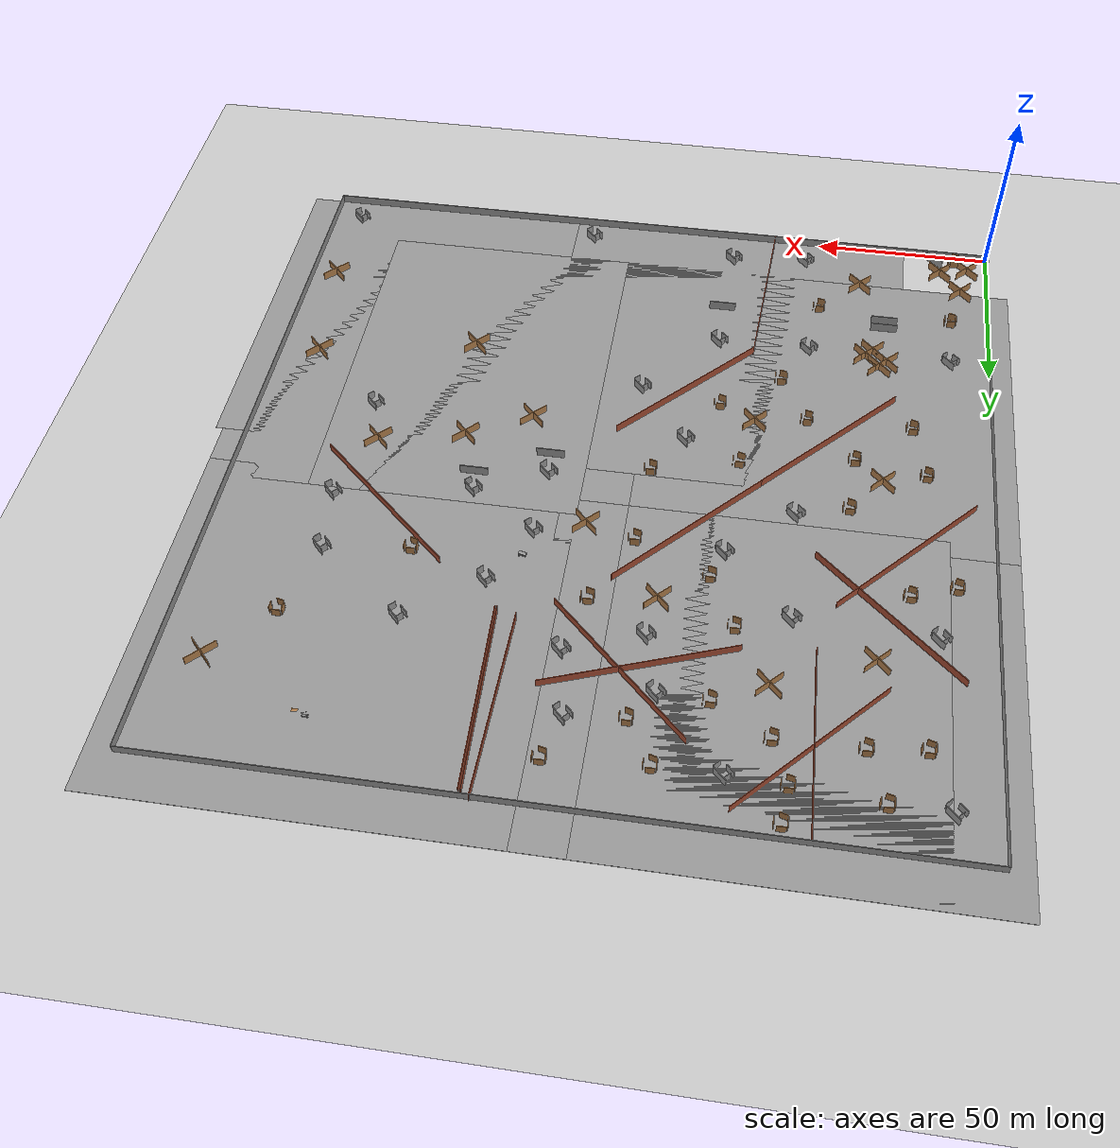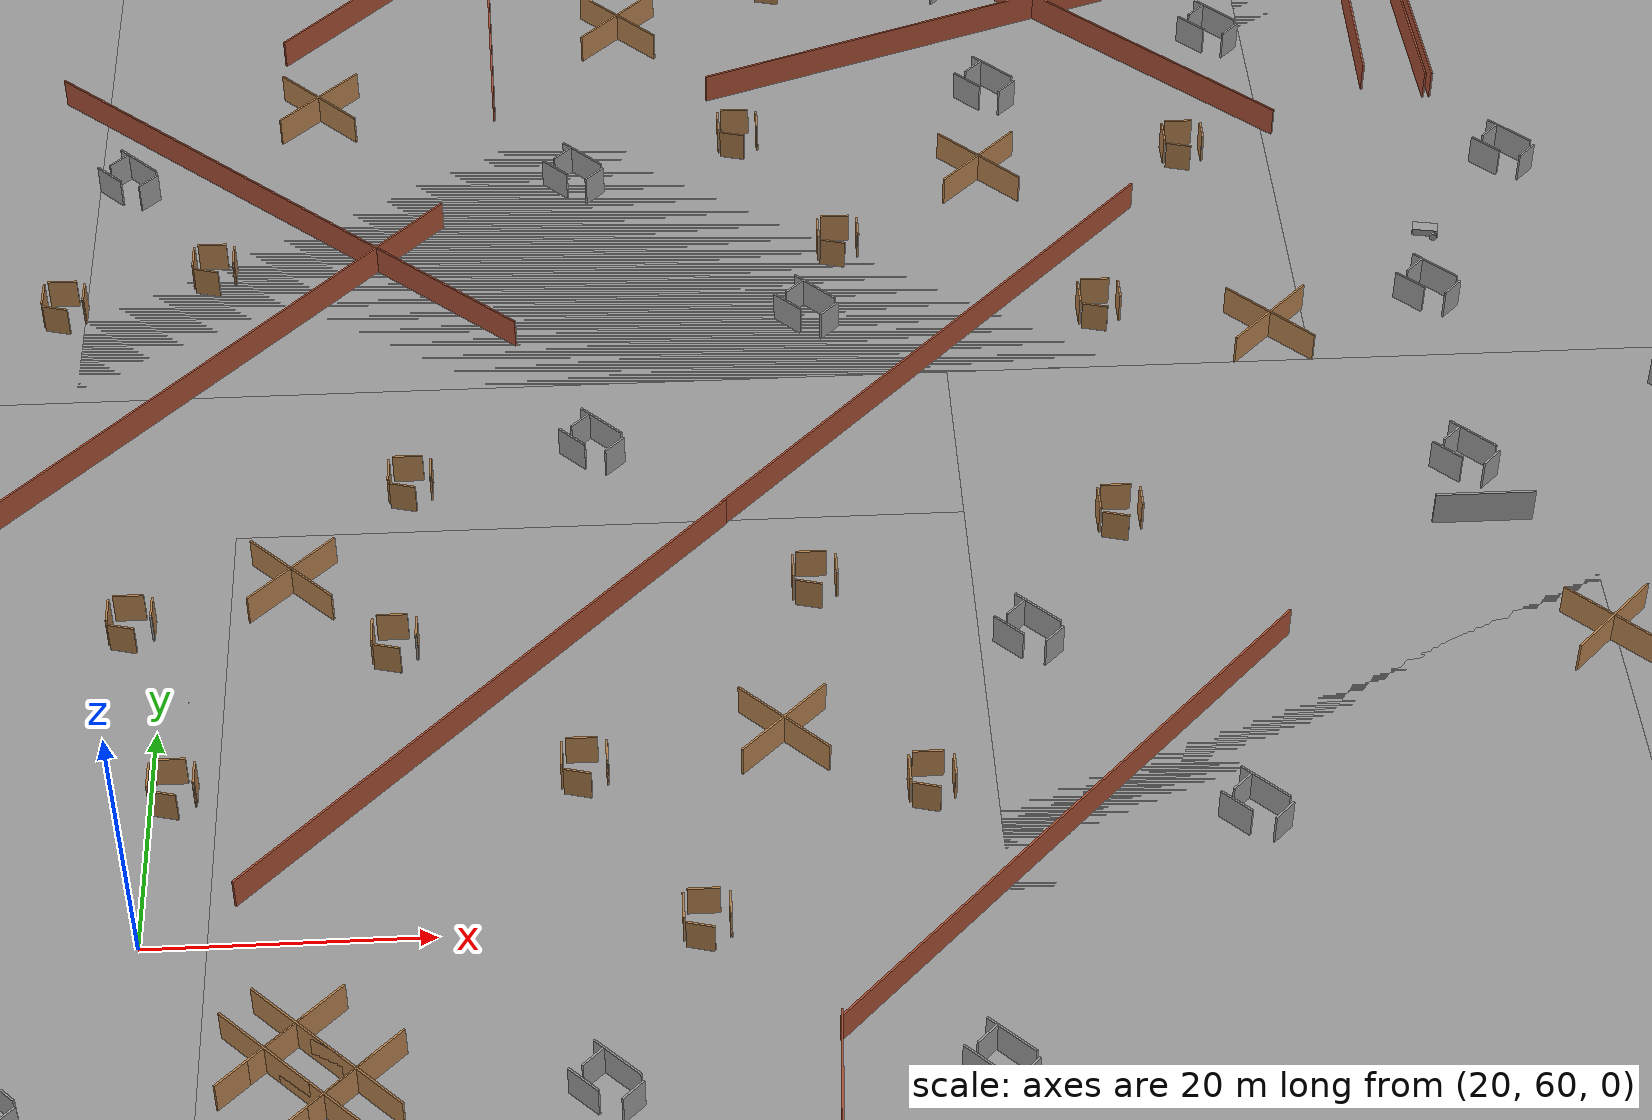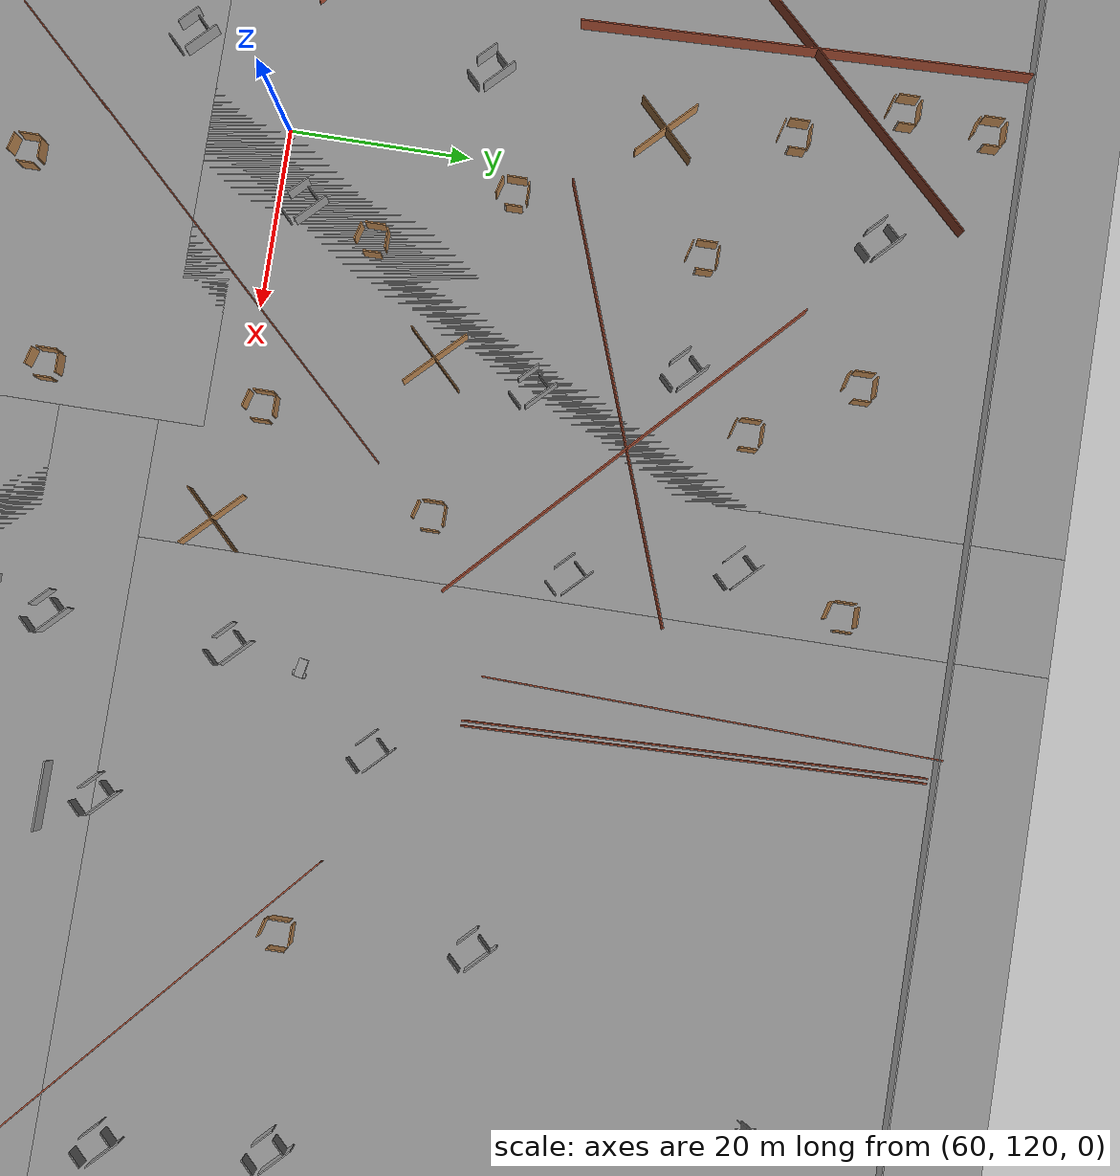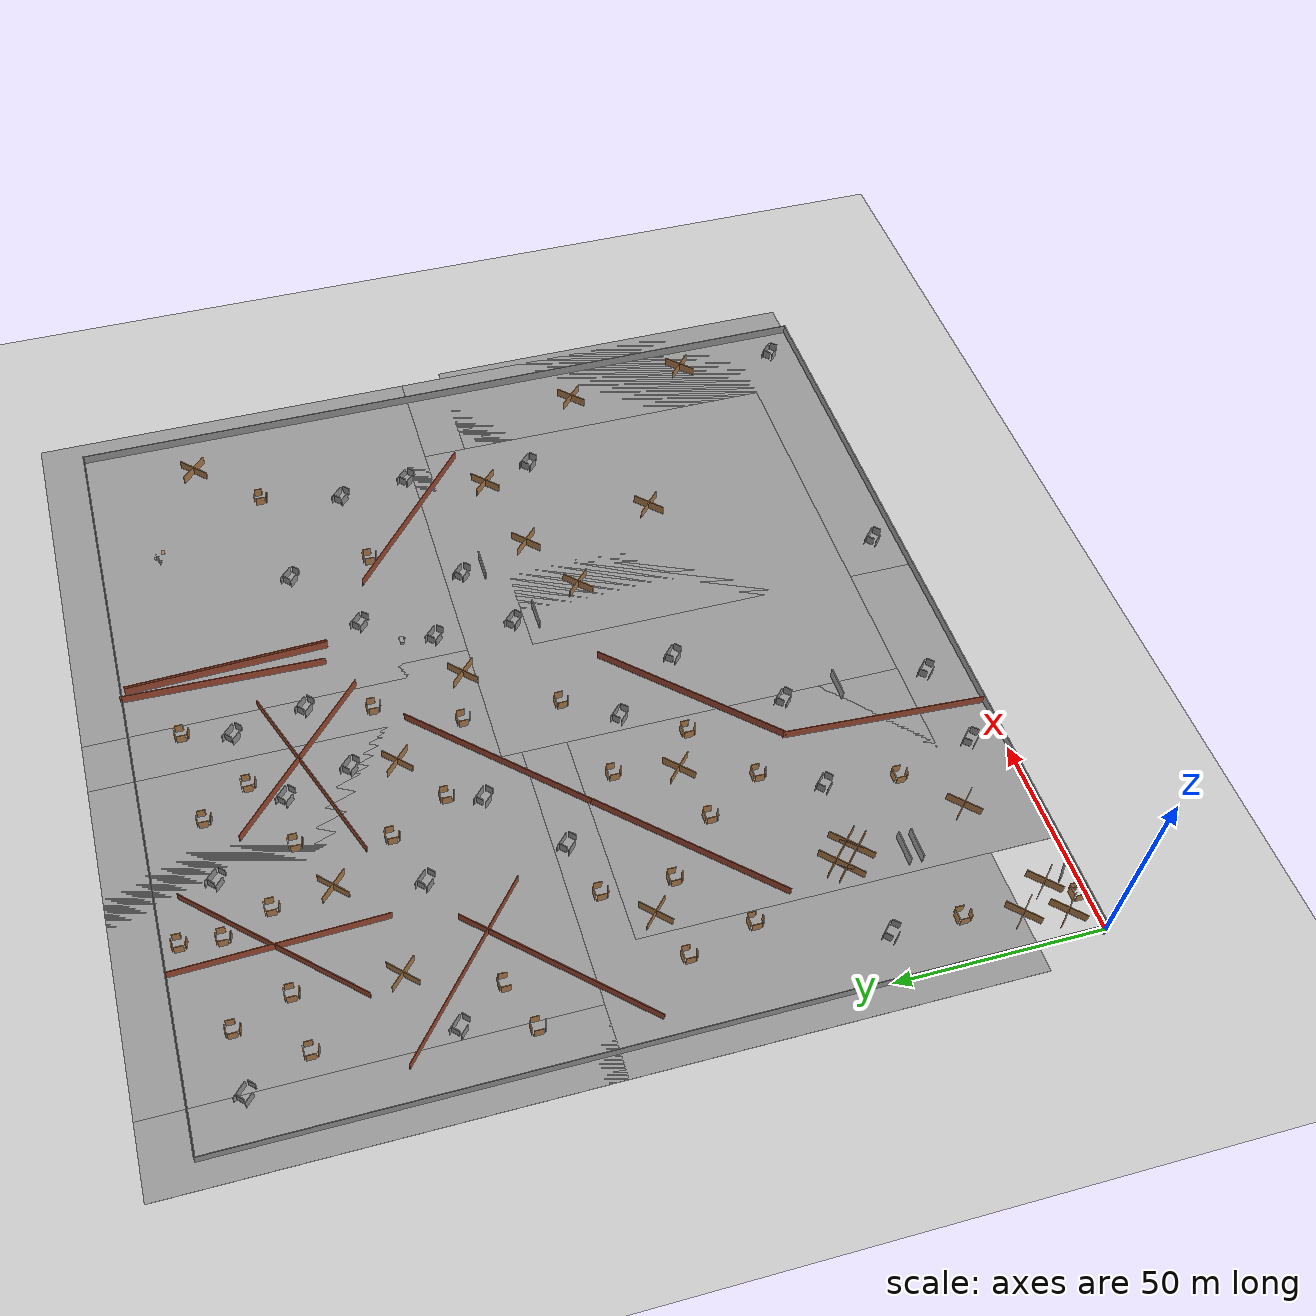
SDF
<sdf version="1.5">
 <world name="default">
  <model name="mard"><static>0</static></model>
  <light name="sun" type="directional">
   <pose>0 0 10 0 -0 0</pose>
   <diffuse>0.8 0.8 0.8 1</diffuse>
   <specular>0.2 0.2 0.2 1</specular>
   <attenuation>
    <range>1000</range>
    <constant>0.9</constant>
    <linear>0.01</linear>
    <quadratic>0.001</quadratic>
   </attenuation>
   <direction>-0.5 0.1 -0.9</direction>
  </light>
  <model name="ground_plane">
   <static>1</static>
   <link name="link">
    <collision name="collision">
     <geometry><plane><normal>0 0 1</normal><size>100 100</size></plane></geometry>
     <surface><friction><ode><mu>100</mu><mu2>50</mu2></ode></friction></surface>
    </collision>
    <visual name="visual">
     <cast_shadows>0</cast_shadows>
     <geometry><plane><normal>0 0 1</normal><size>100 100</size></plane></geometry>
     <material>
      <script><uri>file://media/materials/scripts/gazebo.material</uri><name>Gazebo/Grey</name></script>
     </material>
    </visual>
   </link>
  </model>
  <physics name="default_physics" default="0" type="ode">
   <max_step_size>0.001</max_step_size>
   <real_time_factor>1</real_time_factor>
   <real_time_update_rate>1000</real_time_update_rate>
   <gravity>0 0 -9.8</gravity>
   <magnetic_field>5.5645e-06 2.28758e-05 -4.23884e-05</magnetic_field>
  </physics>
  <scene><ambient>0.4 0.4 0.4 1</ambient><background>0.7 0.7 0.7 1</background><shadows>1</shadows></scene>
  <spherical_coordinates>
   <surface_model>EARTH_WGS84</surface_model>
   <latitude_deg>0</latitude_deg>
   <longitude_deg>0</longitude_deg>
   <elevation>0</elevation>
   <heading_deg>0</heading_deg>
  </spherical_coordinates>
  <model name="map2">
   <pose>100 100 0 0 -0 0</pose>
   <link name="Wall_11">
    <collision name="Wall_11_Collision">
     <geometry><box><size>200.15 0.15 2.5</size></box></geometry>
     <pose>0 0 1.25 0 -0 0</pose>
    </collision>
    <visual name="Wall_11_Visual">
     <pose>0 0 1.25 0 -0 0</pose>
     <geometry><box><size>200.15 0.15 2.5</size></box></geometry>
     <material>
      <script><uri>file://media/materials/scripts/gazebo.material</uri><name>Gazebo/Grey</name></script>
      <ambient>1 1 1 1</ambient>
     </material>
    </visual>
    <pose>-0 100 0 0 -0 0</pose>
   </link>
   <link name="Wall_5">
    <collision name="Wall_5_Collision">
     <geometry><box><size>200.15 0.15 2.5</size></box></geometry>
     <pose>0 0 1.25 0 -0 0</pose>
    </collision>
    <visual name="Wall_5_Visual">
     <pose>0 0 1.25 0 -0 0</pose>
     <geometry><box><size>200.15 0.15 2.5</size></box></geometry>
     <material>
      <script><uri>file://media/materials/scripts/gazebo.material</uri><name>Gazebo/Grey</name></script>
      <ambient>1 1 1 1</ambient>
     </material>
    </visual>
    <pose>-0 -100 0 0 -0 0</pose>
   </link>
   <link name="Wall_7">
    <collision name="Wall_7_Collision">
     <geometry><box><size>200.15 0.15 2.5</size></box></geometry>
     <pose>0 0 1.25 0 -0 0</pose>
    </collision>
    <visual name="Wall_7_Visual">
     <pose>0 0 1.25 0 -0 0</pose>
     <geometry><box><size>200.15 0.15 2.5</size></box></geometry>
     <material>
      <script><uri>file://media/materials/scripts/gazebo.material</uri><name>Gazebo/Grey</name></script>
      <ambient>1 1 1 1</ambient>
     </material>
    </visual>
    <pose>100 0 0 0 -0 1.5708</pose>
   </link>
   <link name="Wall_9">
    <collision name="Wall_9_Collision">
     <geometry><box><size>200.15 0.15 2.5</size></box></geometry>
     <pose>0 0 1.25 0 -0 0</pose>
    </collision>
    <visual name="Wall_9_Visual">
     <pose>0 0 1.25 0 -0 0</pose>
     <geometry><box><size>200.15 0.15 2.5</size></box></geometry>
     <material>
      <script><uri>file://media/materials/scripts/gazebo.material</uri><name>Gazebo/Grey</name></script>
      <ambient>1 1 1 1</ambient>
     </material>
    </visual>
    <pose>-100 0 0 0 -0 1.5708</pose>
   </link>
   <static>1</static>
  </model>
  <model name="ground_plane_0">
   <static>1</static>
   <link name="link">
    <collision name="collision">
     <geometry><plane><normal>0 0 1</normal><size>100 100</size></plane></geometry>
     <surface><friction><ode><mu>100</mu><mu2>50</mu2></ode></friction></surface>
    </collision>
    <visual name="visual">
     <cast_shadows>0</cast_shadows>
     <geometry><plane><normal>0 0 1</normal><size>100 100</size></plane></geometry>
     <material>
      <script><uri>file://media/materials/scripts/gazebo.material</uri><name>Gazebo/Grey</name></script>
     </material>
    </visual>
   </link>
   <pose>157 161 0 0 -0 0</pose>
  </model>
  <model name="ground_plane_1">
   <static>1</static>
   <link name="link">
    <collision name="collision">
     <geometry><plane><normal>0 0 1</normal><size>100 100</size></plane></geometry>
     <surface><friction><ode><mu>100</mu><mu2>50</mu2></ode></friction></surface>
    </collision>
    <visual name="visual">
     <cast_shadows>0</cast_shadows>
     <geometry><plane><normal>0 0 1</normal><size>100 100</size></plane></geometry>
     <material>
      <script><uri>file://media/materials/scripts/gazebo.material</uri><name>Gazebo/Grey</name></script>
     </material>
    </visual>
   </link>
   <pose>61.4867 161 0 0 -0 0</pose>
  </model>
  <model name="ground_plane_2">
   <static>1</static>
   <link name="link">
    <collision name="collision">
     <geometry><plane><normal>0 0 1</normal><size>100 100</size></plane></geometry>
     <surface><friction><ode><mu>100</mu><mu2>50</mu2></ode></friction></surface>
    </collision>
    <visual name="visual">
     <cast_shadows>0</cast_shadows>
     <geometry><plane><normal>0 0 1</normal><size>100 100</size></plane></geometry>
     <material>
      <script><uri>file://media/materials/scripts/gazebo.material</uri><name>Gazebo/Grey</name></script>
     </material>
    </visual>
   </link>
   <pose>44 161 0 0 -0 0</pose>
  </model>
  <model name="ground_plane_3">
   <static>1</static>
   <link name="link">
    <collision name="collision">
     <geometry><plane><normal>0 0 1</normal><size>100 100</size></plane></geometry>
     <surface><friction><ode><mu>100</mu><mu2>50</mu2></ode></friction></surface>
    </collision>
    <visual name="visual">
     <cast_shadows>0</cast_shadows>
     <geometry><plane><normal>0 0 1</normal><size>100 100</size></plane></geometry>
     <material>
      <script><uri>file://media/materials/scripts/gazebo.material</uri><name>Gazebo/Grey</name></script>
     </material>
    </visual>
   </link>
   <pose>44 66 0 0 -0 0</pose>
  </model>
  <model name="ground_plane_4">
   <static>1</static>
   <link name="link">
    <collision name="collision">
     <geometry><plane><normal>0 0 1</normal><size>100 100</size></plane></geometry>
     <surface><friction><ode><mu>100</mu><mu2>50</mu2></ode></friction></surface>
    </collision>
    <visual name="visual">
     <cast_shadows>0</cast_shadows>
     <geometry><plane><normal>0 0 1</normal><size>100 100</size></plane></geometry>
     <material>
      <script><uri>file://media/materials/scripts/gazebo.material</uri><name>Gazebo/Grey</name></script>
     </material>
    </visual>
   </link>
   <pose>128.574 66 0 0 -0 0</pose>
  </model>
  <model name="ground_plane_5">
   <static>1</static>
   <link name="link">
    <collision name="collision">
     <geometry><plane><normal>0 0 1</normal><size>100 100</size></plane></geometry>
     <surface><friction><ode><mu>100</mu><mu2>50</mu2></ode></friction></surface>
    </collision>
    <visual name="visual">
     <cast_shadows>0</cast_shadows>
     <geometry><plane><normal>0 0 1</normal><size>100 100</size></plane></geometry>
     <material>
      <script><uri>file://media/materials/scripts/gazebo.material</uri><name>Gazebo/Grey</name></script>
     </material>
    </visual>
   </link>
   <pose>157 66 0 0 -0 0</pose>
  </model>
  <model name="ground_plane_6">
   <static>1</static>
   <link name="link">
    <collision name="collision">
     <geometry><plane><normal>0 0 1</normal><size>100 100</size></plane></geometry>
     <surface><friction><ode><mu>100</mu><mu2>50</mu2></ode></friction></surface>
    </collision>
    <visual name="visual">
     <cast_shadows>0</cast_shadows>
     <geometry><plane><normal>0 0 1</normal><size>100 100</size></plane></geometry>
     <material>
      <script><uri>file://media/materials/scripts/gazebo.material</uri><name>Gazebo/Grey</name></script>
     </material>
    </visual>
   </link>
   <pose>74.5237 50 0 0 -0 0</pose>
  </model>
  <model name="ground_plane_10">
   <static>1</static>
   <link name="link">
    <collision name="collision">
     <geometry><plane><normal>0 0 1</normal><size>100 100</size></plane></geometry>
     <surface><friction><ode><mu>100</mu><mu2>50</mu2></ode></friction></surface>
    </collision>
    <visual name="visual">
     <cast_shadows>0</cast_shadows>
     <geometry><plane><normal>0 0 1</normal><size>100 100</size></plane></geometry>
     <material>
      <script><uri>file://media/materials/scripts/gazebo.material</uri><name>Gazebo/Grey</name></script>
     </material>
    </visual>
   </link>
   <pose>159 50 0 0 -0 0</pose>
  </model>
  <model name="obs1">
   <pose>31 174.534 0 0 -0 0</pose>
   <link name="Wall_10">
    <collision name="Wall_10_Collision">
     <geometry><box><size>2 0.15 2.5</size></box></geometry>
     <pose>0 0 1.25 0 -0 0</pose>
    </collision>
    <visual name="Wall_10_Visual">
     <pose>0 0 1.25 0 -0 0</pose>
     <geometry><box><size>2 0.15 2.5</size></box></geometry>
     <material>
      <script><uri>file://media/materials/scripts/gazebo.material</uri><name>Gazebo/Wood</name></script>
      <ambient>1 1 1 1</ambient>
     </material>
    </visual>
    <pose>-0.505188 -1.46687 0 0 0 -0.261799</pose>
   </link>
   <link name="Wall_2">
    <collision name="Wall_2_Collision">
     <geometry><box><size>2.25 0.15 2.5</size></box></geometry>
     <pose>0 0 1.25 0 -0 0</pose>
    </collision>
    <visual name="Wall_2_Visual">
     <pose>0 0 1.25 0 -0 0</pose>
     <geometry><box><size>2.25 0.15 2.5</size></box></geometry>
     <material>
      <script><uri>file://media/materials/scripts/gazebo.material</uri><name>Gazebo/Wood</name></script>
      <ambient>1 1 1 1</ambient>
     </material>
    </visual>
    <pose>-1.58039 0.313508 0 0 0 -1.5708</pose>
   </link>
   <link name="Wall_5">
    <collision name="Wall_5_Collision">
     <geometry><box><size>2.25 0.15 2.5</size></box></geometry>
     <pose>0 0 1.25 0 -0 0</pose>
    </collision>
    <visual name="Wall_5_Visual">
     <pose>0 0 1.25 0 -0 0</pose>
     <geometry><box><size>2.25 0.15 2.5</size></box></geometry>
     <material>
      <script><uri>file://media/materials/scripts/gazebo.material</uri><name>Gazebo/Wood</name></script>
      <ambient>1 1 1 1</ambient>
     </material>
    </visual>
    <pose>-0.185262 1.72313 0 0 -0 0</pose>
   </link>
   <link name="Wall_7">
    <collision name="Wall_7_Collision">
     <geometry><box><size>2 0.15 2.5</size></box></geometry>
     <pose>0 0 1.25 0 -0 0</pose>
    </collision>
    <visual name="Wall_7_Visual">
     <pose>0 0 1.25 0 -0 0</pose>
     <geometry><box><size>2 0.15 2.5</size></box></geometry>
     <material>
      <script><uri>file://media/materials/scripts/gazebo.material</uri><name>Gazebo/Wood</name></script>
      <ambient>1 1 1 1</ambient>
     </material>
    </visual>
    <pose>1.58039 0.398833 0 0 0 -1.5708</pose>
   </link>
   <link name="Wall_8">
    <collision name="Wall_8_Collision">
     <geometry><box><size>0.15 0.15 2.5</size></box></geometry>
     <pose>0 0 1.25 0 -0 0</pose>
    </collision>
    <visual name="Wall_8_Visual">
     <pose>0 0 1.25 0 -0 0</pose>
     <geometry><box><size>0.15 0.15 2.5</size></box></geometry>
     <material>
      <script><uri>file://media/materials/scripts/gazebo.material</uri><name>Gazebo/Grey</name></script>
      <ambient>1 1 1 1</ambient>
     </material>
    </visual>
    <pose>1.58039 -0.526167 0 0 -0 0</pose>
   </link>
   <static>1</static>
  </model>
  <model name="obs1_0">
   <pose>52.5346 175 0 0 -0 0</pose>
   <link name="Wall_10">
    <collision name="Wall_10_Collision">
     <geometry><box><size>2 0.15 2.5</size></box></geometry>
     <pose>0 0 1.25 0 -0 0</pose>
    </collision>
    <visual name="Wall_10_Visual">
     <pose>0 0 1.25 0 -0 0</pose>
     <geometry><box><size>2 0.15 2.5</size></box></geometry>
     <material>
      <script><uri>file://media/materials/scripts/gazebo.material</uri><name>Gazebo/Wood</name></script>
      <ambient>1 1 1 1</ambient>
     </material>
    </visual>
    <pose>-0.505188 -1.46687 0 0 0 -0.261799</pose>
   </link>
   <link name="Wall_2">
    <collision name="Wall_2_Collision">
     <geometry><box><size>2.25 0.15 2.5</size></box></geometry>
     <pose>0 0 1.25 0 -0 0</pose>
    </collision>
    <visual name="Wall_2_Visual">
     <pose>0 0 1.25 0 -0 0</pose>
     <geometry><box><size>2.25 0.15 2.5</size></box></geometry>
     <material>
      <script><uri>file://media/materials/scripts/gazebo.material</uri><name>Gazebo/Wood</name></script>
      <ambient>1 1 1 1</ambient>
     </material>
    </visual>
    <pose>-1.58039 0.313508 0 0 0 -1.5708</pose>
   </link>
   <link name="Wall_5">
    <collision name="Wall_5_Collision">
     <geometry><box><size>2.25 0.15 2.5</size></box></geometry>
     <pose>0 0 1.25 0 -0 0</pose>
    </collision>
    <visual name="Wall_5_Visual">
     <pose>0 0 1.25 0 -0 0</pose>
     <geometry><box><size>2.25 0.15 2.5</size></box></geometry>
     <material>
      <script><uri>file://media/materials/scripts/gazebo.material</uri><name>Gazebo/Wood</name></script>
      <ambient>1 1 1 1</ambient>
     </material>
    </visual>
    <pose>-0.185262 1.72313 0 0 -0 0</pose>
   </link>
   <link name="Wall_7">
    <collision name="Wall_7_Collision">
     <geometry><box><size>2 0.15 2.5</size></box></geometry>
     <pose>0 0 1.25 0 -0 0</pose>
    </collision>
    <visual name="Wall_7_Visual">
     <pose>0 0 1.25 0 -0 0</pose>
     <geometry><box><size>2 0.15 2.5</size></box></geometry>
     <material>
      <script><uri>file://media/materials/scripts/gazebo.material</uri><name>Gazebo/Wood</name></script>
      <ambient>1 1 1 1</ambient>
     </material>
    </visual>
    <pose>1.58039 0.398833 0 0 0 -1.5708</pose>
   </link>
   <link name="Wall_8">
    <collision name="Wall_8_Collision">
     <geometry><box><size>0.15 0.15 2.5</size></box></geometry>
     <pose>0 0 1.25 0 -0 0</pose>
    </collision>
    <visual name="Wall_8_Visual">
     <pose>0 0 1.25 0 -0 0</pose>
     <geometry><box><size>0.15 0.15 2.5</size></box></geometry>
     <material>
      <script><uri>file://media/materials/scripts/gazebo.material</uri><name>Gazebo/Grey</name></script>
      <ambient>1 1 1 1</ambient>
     </material>
    </visual>
    <pose>1.58039 -0.526167 0 0 -0 0</pose>
   </link>
   <static>1</static>
  </model>
  <model name="obs1_1">
   <pose>86 174.595 0 0 -0 0</pose>
   <link name="Wall_10">
    <collision name="Wall_10_Collision">
     <geometry><box><size>2 0.15 2.5</size></box></geometry>
     <pose>0 0 1.25 0 -0 0</pose>
    </collision>
    <visual name="Wall_10_Visual">
     <pose>0 0 1.25 0 -0 0</pose>
     <geometry><box><size>2 0.15 2.5</size></box></geometry>
     <material>
      <script><uri>file://media/materials/scripts/gazebo.material</uri><name>Gazebo/Wood</name></script>
      <ambient>1 1 1 1</ambient>
     </material>
    </visual>
    <pose>-0.505188 -1.46687 0 0 0 -0.261799</pose>
   </link>
   <link name="Wall_2">
    <collision name="Wall_2_Collision">
     <geometry><box><size>2.25 0.15 2.5</size></box></geometry>
     <pose>0 0 1.25 0 -0 0</pose>
    </collision>
    <visual name="Wall_2_Visual">
     <pose>0 0 1.25 0 -0 0</pose>
     <geometry><box><size>2.25 0.15 2.5</size></box></geometry>
     <material>
      <script><uri>file://media/materials/scripts/gazebo.material</uri><name>Gazebo/Wood</name></script>
      <ambient>1 1 1 1</ambient>
     </material>
    </visual>
    <pose>-1.58039 0.313508 0 0 0 -1.5708</pose>
   </link>
   <link name="Wall_5">
    <collision name="Wall_5_Collision">
     <geometry><box><size>2.25 0.15 2.5</size></box></geometry>
     <pose>0 0 1.25 0 -0 0</pose>
    </collision>
    <visual name="Wall_5_Visual">
     <pose>0 0 1.25 0 -0 0</pose>
     <geometry><box><size>2.25 0.15 2.5</size></box></geometry>
     <material>
      <script><uri>file://media/materials/scripts/gazebo.material</uri><name>Gazebo/Wood</name></script>
      <ambient>1 1 1 1</ambient>
     </material>
    </visual>
    <pose>-0.185262 1.72313 0 0 -0 0</pose>
   </link>
   <link name="Wall_7">
    <collision name="Wall_7_Collision">
     <geometry><box><size>2 0.15 2.5</size></box></geometry>
     <pose>0 0 1.25 0 -0 0</pose>
    </collision>
    <visual name="Wall_7_Visual">
     <pose>0 0 1.25 0 -0 0</pose>
     <geometry><box><size>2 0.15 2.5</size></box></geometry>
     <material>
      <script><uri>file://media/materials/scripts/gazebo.material</uri><name>Gazebo/Wood</name></script>
      <ambient>1 1 1 1</ambient>
     </material>
    </visual>
    <pose>1.58039 0.398833 0 0 0 -1.5708</pose>
   </link>
   <link name="Wall_8">
    <collision name="Wall_8_Collision">
     <geometry><box><size>0.15 0.15 2.5</size></box></geometry>
     <pose>0 0 1.25 0 -0 0</pose>
    </collision>
    <visual name="Wall_8_Visual">
     <pose>0 0 1.25 0 -0 0</pose>
     <geometry><box><size>0.15 0.15 2.5</size></box></geometry>
     <material>
      <script><uri>file://media/materials/scripts/gazebo.material</uri><name>Gazebo/Grey</name></script>
      <ambient>1 1 1 1</ambient>
     </material>
    </visual>
    <pose>1.58039 -0.526167 0 0 -0 0</pose>
   </link>
   <static>1</static>
  </model>
  <model name="obs1_2">
   <pose>63.592 145.434 0 0 -0 0</pose>
   <link name="Wall_10">
    <collision name="Wall_10_Collision">
     <geometry><box><size>2 0.15 2.5</size></box></geometry>
     <pose>0 0 1.25 0 -0 0</pose>
    </collision>
    <visual name="Wall_10_Visual">
     <pose>0 0 1.25 0 -0 0</pose>
     <geometry><box><size>2 0.15 2.5</size></box></geometry>
     <material>
      <script><uri>file://media/materials/scripts/gazebo.material</uri><name>Gazebo/Wood</name></script>
      <ambient>1 1 1 1</ambient>
     </material>
    </visual>
    <pose>-0.505188 -1.46687 0 0 0 -0.261799</pose>
   </link>
   <link name="Wall_2">
    <collision name="Wall_2_Collision">
     <geometry><box><size>2.25 0.15 2.5</size></box></geometry>
     <pose>0 0 1.25 0 -0 0</pose>
    </collision>
    <visual name="Wall_2_Visual">
     <pose>0 0 1.25 0 -0 0</pose>
     <geometry><box><size>2.25 0.15 2.5</size></box></geometry>
     <material>
      <script><uri>file://media/materials/scripts/gazebo.material</uri><name>Gazebo/Wood</name></script>
      <ambient>1 1 1 1</ambient>
     </material>
    </visual>
    <pose>-1.58039 0.313508 0 0 0 -1.5708</pose>
   </link>
   <link name="Wall_5">
    <collision name="Wall_5_Collision">
     <geometry><box><size>2.25 0.15 2.5</size></box></geometry>
     <pose>0 0 1.25 0 -0 0</pose>
    </collision>
    <visual name="Wall_5_Visual">
     <pose>0 0 1.25 0 -0 0</pose>
     <geometry><box><size>2.25 0.15 2.5</size></box></geometry>
     <material>
      <script><uri>file://media/materials/scripts/gazebo.material</uri><name>Gazebo/Wood</name></script>
      <ambient>1 1 1 1</ambient>
     </material>
    </visual>
    <pose>-0.185262 1.72313 0 0 -0 0</pose>
   </link>
   <link name="Wall_7">
    <collision name="Wall_7_Collision">
     <geometry><box><size>2 0.15 2.5</size></box></geometry>
     <pose>0 0 1.25 0 -0 0</pose>
    </collision>
    <visual name="Wall_7_Visual">
     <pose>0 0 1.25 0 -0 0</pose>
     <geometry><box><size>2 0.15 2.5</size></box></geometry>
     <material>
      <script><uri>file://media/materials/scripts/gazebo.material</uri><name>Gazebo/Wood</name></script>
      <ambient>1 1 1 1</ambient>
     </material>
    </visual>
    <pose>1.58039 0.398833 0 0 0 -1.5708</pose>
   </link>
   <link name="Wall_8">
    <collision name="Wall_8_Collision">
     <geometry><box><size>0.15 0.15 2.5</size></box></geometry>
     <pose>0 0 1.25 0 -0 0</pose>
    </collision>
    <visual name="Wall_8_Visual">
     <pose>0 0 1.25 0 -0 0</pose>
     <geometry><box><size>0.15 0.15 2.5</size></box></geometry>
     <material>
      <script><uri>file://media/materials/scripts/gazebo.material</uri><name>Gazebo/Grey</name></script>
      <ambient>1 1 1 1</ambient>
     </material>
    </visual>
    <pose>1.58039 -0.526167 0 0 -0 0</pose>
   </link>
   <static>1</static>
  </model>
  <model name="obs3">
   <pose>29.0908 150.773 0 0 -0 0</pose>
   <link name="Wall_0">
    <collision name="Wall_0_Collision">
     <geometry><box><size>8.63528 0.15 2.5</size></box></geometry>
     <pose>0 0 1.25 0 -0 0</pose>
    </collision>
    <visual name="Wall_0_Visual">
     <pose>0 0 1.25 0 -0 0</pose>
     <geometry><box><size>8.63528 0.15 2.5</size></box></geometry>
     <material>
      <script><uri>file://media/materials/scripts/gazebo.material</uri><name>Gazebo/Wood</name></script>
      <ambient>1 1 1 1</ambient>
     </material>
    </visual>
    <pose>0 0 0 0 0 -0.785398</pose>
   </link>
   <link name="Wall_2">
    <collision name="Wall_2_Collision">
     <geometry><box><size>8.63528 0.15 2.5</size></box></geometry>
     <pose>0 0 1.25 0 -0 0</pose>
    </collision>
    <visual name="Wall_2_Visual">
     <pose>0 0 1.25 0 -0 0</pose>
     <geometry><box><size>8.63528 0.15 2.5</size></box></geometry>
     <material>
      <script><uri>file://media/materials/scripts/gazebo.material</uri><name>Gazebo/Wood</name></script>
      <ambient>1 1 1 1</ambient>
     </material>
    </visual>
    <pose>0 0 0 0 0 -2.35619</pose>
   </link>
   <static>1</static>
  </model>
  <model name="obs3_0">
   <pose>54 161 0 0 -0 0</pose>
   <link name="Wall_0">
    <collision name="Wall_0_Collision">
     <geometry><box><size>8.63528 0.15 2.5</size></box></geometry>
     <pose>0 0 1.25 0 -0 0</pose>
    </collision>
    <visual name="Wall_0_Visual">
     <pose>0 0 1.25 0 -0 0</pose>
     <geometry><box><size>8.63528 0.15 2.5</size></box></geometry>
     <material>
      <script><uri>file://media/materials/scripts/gazebo.material</uri><name>Gazebo/Wood</name></script>
      <ambient>1 1 1 1</ambient>
     </material>
    </visual>
    <pose>0 0 0 0 0 -0.785398</pose>
   </link>
   <link name="Wall_2">
    <collision name="Wall_2_Collision">
     <geometry><box><size>8.63528 0.15 2.5</size></box></geometry>
     <pose>0 0 1.25 0 -0 0</pose>
    </collision>
    <visual name="Wall_2_Visual">
     <pose>0 0 1.25 0 -0 0</pose>
     <geometry><box><size>8.63528 0.15 2.5</size></box></geometry>
     <material>
      <script><uri>file://media/materials/scripts/gazebo.material</uri><name>Gazebo/Wood</name></script>
      <ambient>1 1 1 1</ambient>
     </material>
    </visual>
    <pose>0 0 0 0 0 -2.35619</pose>
   </link>
   <static>1</static>
  </model>
  <model name="obs2">
   <pose>80 167 0 0 -0 0</pose>
   <link name="Wall_0">
    <collision name="Wall_0_Collision">
     <geometry><box><size>2 0.15 2.5</size></box></geometry>
     <pose>0 0 1.25 0 -0 0</pose>
    </collision>
    <visual name="Wall_0_Visual">
     <pose>0 0 1.25 0 -0 0</pose>
     <geometry><box><size>2 0.15 2.5</size></box></geometry>
     <material>
      <script><uri>file://media/materials/scripts/gazebo.material</uri><name>Gazebo/Grey</name></script>
      <ambient>1 1 1 1</ambient>
     </material>
    </visual>
    <pose>-0.796332 1.10862 0 0 -0 0.785398</pose>
   </link>
   <link name="Wall_2">
    <collision name="Wall_2_Collision">
     <geometry><box><size>4.25 0.15 2.5</size></box></geometry>
     <pose>0 0 1.25 0 -0 0</pose>
    </collision>
    <visual name="Wall_2_Visual">
     <pose>0 0 1.25 0 -0 0</pose>
     <geometry><box><size>4.25 0.15 2.5</size></box></geometry>
     <material>
      <script><uri>file://media/materials/scripts/gazebo.material</uri><name>Gazebo/Grey</name></script>
      <ambient>1 1 1 1</ambient>
     </material>
    </visual>
    <pose>0.773928 0.982661 0 0 0 -0.785398</pose>
   </link>
   <link name="Wall_4">
    <collision name="Wall_4_Collision">
     <geometry><box><size>2.75 0.15 2.5</size></box></geometry>
     <pose>0 0 1.25 0 -0 0</pose>
    </collision>
    <visual name="Wall_4_Visual">
     <pose>0 0 1.25 0 -0 0</pose>
     <geometry><box><size>2.75 0.15 2.5</size></box></geometry>
     <material>
      <script><uri>file://media/materials/scripts/gazebo.material</uri><name>Gazebo/Grey</name></script>
      <ambient>1 1 1 1</ambient>
     </material>
    </visual>
    <pose>-1.45556 -0.740711 0 0 0 -0.785398</pose>
   </link>
   <link name="Wall_6">
    <collision name="Wall_6_Collision">
     <geometry><box><size>2 0.15 2.5</size></box></geometry>
     <pose>0 0 1.25 0 -0 0</pose>
    </collision>
    <visual name="Wall_6_Visual">
     <pose>0 0 1.25 0 -0 0</pose>
     <geometry><box><size>2 0.15 2.5</size></box></geometry>
     <material>
      <script><uri>file://media/materials/scripts/gazebo.material</uri><name>Gazebo/Grey</name></script>
      <ambient>1 1 1 1</ambient>
     </material>
    </visual>
    <pose>1.72073 -1.77816 0 0 -0 0.785398</pose>
   </link>
   <static>1</static>
  </model>
  <model name="obs2_0">
   <pose>14 142 0 0 -0 0</pose>
   <link name="Wall_0">
    <collision name="Wall_0_Collision">
     <geometry><box><size>2 0.15 2.5</size></box></geometry>
     <pose>0 0 1.25 0 -0 0</pose>
    </collision>
    <visual name="Wall_0_Visual">
     <pose>0 0 1.25 0 -0 0</pose>
     <geometry><box><size>2 0.15 2.5</size></box></geometry>
     <material>
      <script><uri>file://media/materials/scripts/gazebo.material</uri><name>Gazebo/Grey</name></script>
      <ambient>1 1 1 1</ambient>
     </material>
    </visual>
    <pose>-0.796332 1.10862 0 0 -0 0.785398</pose>
   </link>
   <link name="Wall_2">
    <collision name="Wall_2_Collision">
     <geometry><box><size>4.25 0.15 2.5</size></box></geometry>
     <pose>0 0 1.25 0 -0 0</pose>
    </collision>
    <visual name="Wall_2_Visual">
     <pose>0 0 1.25 0 -0 0</pose>
     <geometry><box><size>4.25 0.15 2.5</size></box></geometry>
     <material>
      <script><uri>file://media/materials/scripts/gazebo.material</uri><name>Gazebo/Grey</name></script>
      <ambient>1 1 1 1</ambient>
     </material>
    </visual>
    <pose>0.773928 0.982661 0 0 0 -0.785398</pose>
   </link>
   <link name="Wall_4">
    <collision name="Wall_4_Collision">
     <geometry><box><size>2.75 0.15 2.5</size></box></geometry>
     <pose>0 0 1.25 0 -0 0</pose>
    </collision>
    <visual name="Wall_4_Visual">
     <pose>0 0 1.25 0 -0 0</pose>
     <geometry><box><size>2.75 0.15 2.5</size></box></geometry>
     <material>
      <script><uri>file://media/materials/scripts/gazebo.material</uri><name>Gazebo/Grey</name></script>
      <ambient>1 1 1 1</ambient>
     </material>
    </visual>
    <pose>-1.45556 -0.740711 0 0 0 -0.785398</pose>
   </link>
   <link name="Wall_6">
    <collision name="Wall_6_Collision">
     <geometry><box><size>2 0.15 2.5</size></box></geometry>
     <pose>0 0 1.25 0 -0 0</pose>
    </collision>
    <visual name="Wall_6_Visual">
     <pose>0 0 1.25 0 -0 0</pose>
     <geometry><box><size>2 0.15 2.5</size></box></geometry>
     <material>
      <script><uri>file://media/materials/scripts/gazebo.material</uri><name>Gazebo/Grey</name></script>
      <ambient>1 1 1 1</ambient>
     </material>
    </visual>
    <pose>1.72073 -1.77816 0 0 -0 0.785398</pose>
   </link>
   <static>1</static>
  </model>
  <model name="wall1">
   <pose>65.083 25.2985 0 0 -0 1.51629</pose>
   <link name="Wall_0">
    <collision name="Wall_0_Collision">
     <geometry><box><size>50 0.15 2.5</size></box></geometry>
     <pose>0 0 1.25 0 -0 0</pose>
    </collision>
    <visual name="Wall_0_Visual">
     <pose>0 0 1.25 0 -0 0</pose>
     <geometry><box><size>50 0.15 2.5</size></box></geometry>
     <material>
      <script><uri>file://media/materials/scripts/gazebo.material</uri><name>Gazebo/Bricks</name></script>
      <ambient>1 1 1 1</ambient>
     </material>
    </visual>
    <pose>1e-06 0 0 0 -0 3.14159</pose>
   </link>
   <static>1</static>
  </model>
  <model name="wall1_clone">
   <pose>43.1975 176.615 0 0 -0 0.808575</pose>
   <link name="Wall_0">
    <collision name="Wall_0_Collision">
     <geometry><box><size>50 0.15 2.5</size></box></geometry>
     <pose>0 0 1.25 0 -0 0</pose>
    </collision>
    <visual name="Wall_0_Visual">
     <pose>0 0 1.25 0 -0 0</pose>
     <geometry><box><size>50 0.15 2.5</size></box></geometry>
     <material>
      <script><uri>file://media/materials/scripts/gazebo.material</uri><name>Gazebo/Bricks</name></script>
      <ambient>1 1 1 1</ambient>
     </material>
    </visual>
    <pose>1e-06 0 0 0 -0 3.14159</pose>
   </link>
   <static>1</static>
  </model>
  <model name="wall1_clone_0">
   <pose>26.6122 137.564 0 0 -0 2.41454</pose>
   <link name="Wall_0">
    <collision name="Wall_0_Collision">
     <geometry><box><size>50 0.15 2.5</size></box></geometry>
     <pose>0 0 1.25 0 -0 0</pose>
    </collision>
    <visual name="Wall_0_Visual">
     <pose>0 0 1.25 0 -0 0</pose>
     <geometry><box><size>50 0.15 2.5</size></box></geometry>
     <material>
      <script><uri>file://media/materials/scripts/gazebo.material</uri><name>Gazebo/Bricks</name></script>
      <ambient>1 1 1 1</ambient>
     </material>
    </visual>
    <pose>1e-06 0 0 0 -0 3.14159</pose>
   </link>
   <static>1</static>
  </model>
  <model name="wall1_clone_1">
   <pose>84.7221 160.32 0 0 0 -2.79456</pose>
   <link name="Wall_0">
    <collision name="Wall_0_Collision">
     <geometry><box><size>50 0.15 2.5</size></box></geometry>
     <pose>0 0 1.25 0 -0 0</pose>
    </collision>
    <visual name="Wall_0_Visual">
     <pose>0 0 1.25 0 -0 0</pose>
     <geometry><box><size>50 0.15 2.5</size></box></geometry>
     <material>
      <script><uri>file://media/materials/scripts/gazebo.material</uri><name>Gazebo/Bricks</name></script>
      <ambient>1 1 1 1</ambient>
     </material>
    </visual>
    <pose>1e-06 0 0 0 -0 3.14159</pose>
   </link>
   <static>1</static>
  </model>
  <model name="wall1_clone_2">
   <pose>83.6114 67.6773 0 0 -0 0.808575</pose>
   <link name="Wall_0">
    <collision name="Wall_0_Collision">
     <geometry><box><size>50 0.15 2.5</size></box></geometry>
     <pose>0 0 1.25 0 -0 0</pose>
    </collision>
    <visual name="Wall_0_Visual">
     <pose>0 0 1.25 0 -0 0</pose>
     <geometry><box><size>50 0.15 2.5</size></box></geometry>
     <material>
      <script><uri>file://media/materials/scripts/gazebo.material</uri><name>Gazebo/Bricks</name></script>
      <ambient>1 1 1 1</ambient>
     </material>
    </visual>
    <pose>1e-06 0 0 0 -0 3.14159</pose>
   </link>
   <static>1</static>
  </model>
  <model name="wall1_clone_3">
   <pose>43.532 81.5625 0 0 -0 0.808575</pose>
   <link name="Wall_0">
    <collision name="Wall_0_Collision">
     <geometry><box><size>50 0.15 2.5</size></box></geometry>
     <pose>0 0 1.25 0 -0 0</pose>
    </collision>
    <visual name="Wall_0_Visual">
     <pose>0 0 1.25 0 -0 0</pose>
     <geometry><box><size>50 0.15 2.5</size></box></geometry>
     <material>
      <script><uri>file://media/materials/scripts/gazebo.material</uri><name>Gazebo/Bricks</name></script>
      <ambient>1 1 1 1</ambient>
     </material>
    </visual>
    <pose>1e-06 0 0 0 -0 3.14159</pose>
   </link>
   <static>1</static>
  </model>
  <model name="wall1_clone_4">
   <pose>116.89 175.383 0 0 0 -1.59681</pose>
   <link name="Wall_0">
    <collision name="Wall_0_Collision">
     <geometry><box><size>50 0.15 2.5</size></box></geometry>
     <pose>0 0 1.25 0 -0 0</pose>
    </collision>
    <visual name="Wall_0_Visual">
     <pose>0 0 1.25 0 -0 0</pose>
     <geometry><box><size>50 0.15 2.5</size></box></geometry>
     <material>
      <script><uri>file://media/materials/scripts/gazebo.material</uri><name>Gazebo/Bricks</name></script>
      <ambient>1 1 1 1</ambient>
     </material>
    </visual>
    <pose>1e-06 0 0 0 -0 3.14159</pose>
   </link>
   <static>1</static>
  </model>
  <model name="wall1_clone_5">
   <pose>89.7144 161.917 0 0 0 -0.75808</pose>
   <link name="Wall_0">
    <collision name="Wall_0_Collision">
     <geometry><box><size>50 0.15 2.5</size></box></geometry>
     <pose>0 0 1.25 0 -0 0</pose>
    </collision>
    <visual name="Wall_0_Visual">
     <pose>0 0 1.25 0 -0 0</pose>
     <geometry><box><size>50 0.15 2.5</size></box></geometry>
     <material>
      <script><uri>file://media/materials/scripts/gazebo.material</uri><name>Gazebo/Bricks</name></script>
      <ambient>1 1 1 1</ambient>
     </material>
    </visual>
    <pose>1e-06 0 0 0 -0 3.14159</pose>
   </link>
   <static>1</static>
  </model>
  <model name="wall1_clone_6">
   <pose>42.7649 174.914 0 0 -0 1.60154</pose>
   <link name="Wall_0">
    <collision name="Wall_0_Collision">
     <geometry><box><size>50 0.15 2.5</size></box></geometry>
     <pose>0 0 1.25 0 -0 0</pose>
    </collision>
    <visual name="Wall_0_Visual">
     <pose>0 0 1.25 0 -0 0</pose>
     <geometry><box><size>50 0.15 2.5</size></box></geometry>
     <material>
      <script><uri>file://media/materials/scripts/gazebo.material</uri><name>Gazebo/Bricks</name></script>
      <ambient>1 1 1 1</ambient>
     </material>
    </visual>
    <pose>1e-06 0 0 0 -0 3.14159</pose>
   </link>
   <static>1</static>
  </model>
  <model name="wall1_clone_7">
   <pose>22.1641 117.941 0 0 -0 0.808575</pose>
   <link name="Wall_0">
    <collision name="Wall_0_Collision">
     <geometry><box><size>50 0.15 2.5</size></box></geometry>
     <pose>0 0 1.25 0 -0 0</pose>
    </collision>
    <visual name="Wall_0_Visual">
     <pose>0 0 1.25 0 -0 0</pose>
     <geometry><box><size>50 0.15 2.5</size></box></geometry>
     <material>
      <script><uri>file://media/materials/scripts/gazebo.material</uri><name>Gazebo/Bricks</name></script>
      <ambient>1 1 1 1</ambient>
     </material>
    </visual>
    <pose>1e-06 0 0 0 -0 3.14159</pose>
   </link>
   <static>1</static>
  </model>
  <model name="wall1_clone_3_clone">
   <pose>77.8001 117.545 0 0 -0 0.808575</pose>
   <link name="Wall_0">
    <collision name="Wall_0_Collision">
     <geometry><box><size>50 0.15 2.5</size></box></geometry>
     <pose>0 0 1.25 0 -0 0</pose>
    </collision>
    <visual name="Wall_0_Visual">
     <pose>0 0 1.25 0 -0 0</pose>
     <geometry><box><size>50 0.15 2.5</size></box></geometry>
     <material>
      <script><uri>file://media/materials/scripts/gazebo.material</uri><name>Gazebo/Bricks</name></script>
      <ambient>1 1 1 1</ambient>
     </material>
    </visual>
    <pose>1e-06 0 0 0 -0 3.14159</pose>
   </link>
   <static>1</static>
  </model>
  <model name="car">
   <link name="chassis">
    <pose>0 0 0.3 0 -0 0</pose>
    <collision name="collision"><geometry><box><size>2 1 0.2</size></box></geometry></collision>
    <visual name="visual">
     <geometry><box><size>2 1 0.2</size></box></geometry>
     <material>
      <script><uri>file://media/materials/scripts/gazebo.material</uri><name>Gazebo/Green</name></script>
     </material>
    </visual>
    <inertial>
     <inertia><ixx>1</ixx><ixy>0</ixy><ixz>0</ixz><iyy>1</iyy><iyz>0</iyz><izz>1</izz></inertia>
     <mass>1</mass>
    </inertial>
   </link>
   <link name="front_left_wheel">
    <pose>0.8 0.6 0.3 0 1.5707 1.5707</pose>
    <collision name="collision">
     <geometry><cylinder><radius>0.3</radius><length>0.1</length></cylinder></geometry>
    </collision>
    <visual name="visual">
     <geometry><cylinder><radius>0.3</radius><length>0.1</length></cylinder></geometry>
     <material>
      <script><uri>file://media/materials/scripts/gazebo.material</uri><name>Gazebo/Black</name></script>
     </material>
    </visual>
    <inertial>
     <inertia><ixx>1</ixx><ixy>0</ixy><ixz>0</ixz><iyy>1</iyy><iyz>0</iyz><izz>1</izz></inertia>
     <mass>1</mass>
    </inertial>
   </link>
   <link name="front_right_wheel">
    <pose>0.8 -0.6 0.3 0 1.5707 1.5707</pose>
    <collision name="collision">
     <geometry><cylinder><radius>0.3</radius><length>0.1</length></cylinder></geometry>
    </collision>
    <visual name="visual">
     <geometry><cylinder><radius>0.3</radius><length>0.1</length></cylinder></geometry>
     <material>
      <script><uri>file://media/materials/scripts/gazebo.material</uri><name>Gazebo/Black</name></script>
     </material>
    </visual>
    <inertial>
     <inertia><ixx>1</ixx><ixy>0</ixy><ixz>0</ixz><iyy>1</iyy><iyz>0</iyz><izz>1</izz></inertia>
     <mass>1</mass>
    </inertial>
   </link>
   <link name="back_right_wheel">
    <pose>-0.8 -0.6 0.3 0 1.5707 1.5707</pose>
    <collision name="collision">
     <geometry><cylinder><radius>0.3</radius><length>0.1</length></cylinder></geometry>
    </collision>
    <visual name="visual">
     <geometry><cylinder><radius>0.3</radius><length>0.1</length></cylinder></geometry>
     <material>
      <script><uri>file://media/materials/scripts/gazebo.material</uri><name>Gazebo/Black</name></script>
     </material>
    </visual>
    <inertial>
     <inertia><ixx>1</ixx><ixy>0</ixy><ixz>0</ixz><iyy>1</iyy><iyz>0</iyz><izz>1</izz></inertia>
     <mass>1</mass>
    </inertial>
   </link>
   <link name="back_left_wheel">
    <pose>-0.8 0.6 0.3 0 1.5707 1.5707</pose>
    <collision name="collision">
     <geometry><cylinder><radius>0.3</radius><length>0.1</length></cylinder></geometry>
    </collision>
    <visual name="visual">
     <geometry><cylinder><radius>0.3</radius><length>0.1</length></cylinder></geometry>
     <material>
      <script><uri>file://media/materials/scripts/gazebo.material</uri><name>Gazebo/Black</name></script>
     </material>
    </visual>
    <inertial>
     <inertia><ixx>1</ixx><ixy>0</ixy><ixz>0</ixz><iyy>1</iyy><iyz>0</iyz><izz>1</izz></inertia>
     <mass>1</mass>
    </inertial>
   </link>
   <link name="gas_pedal">
    <pose>0.3 0.1 0.5 0 -0 0</pose>
    <collision name="collision"><geometry><box><size>0.1 0.1 0.1</size></box></geometry></collision>
    <visual name="visual">
     <geometry><box><size>0.1 0.1 0.1</size></box></geometry>
     <material>
      <script><uri>file://media/materials/scripts/gazebo.material</uri><name>Gazebo/Red</name></script>
     </material>
    </visual>
    <inertial>
     <inertia><ixx>1</ixx><ixy>0</ixy><ixz>0</ixz><iyy>1</iyy><iyz>0</iyz><izz>1</izz></inertia>
     <mass>1</mass>
    </inertial>
   </link>
   <link name="brake_pedal">
    <pose>0.3 0.25 0.5 0 -0 0</pose>
    <collision name="collision"><geometry><box><size>0.1 0.1 0.1</size></box></geometry></collision>
    <visual name="visual">
     <geometry><box><size>0.1 0.1 0.1</size></box></geometry>
     <material>
      <script><uri>file://media/materials/scripts/gazebo.material</uri><name>Gazebo/Blue</name></script>
     </material>
    </visual>
    <inertial>
     <inertia><ixx>1</ixx><ixy>0</ixy><ixz>0</ixz><iyy>1</iyy><iyz>0</iyz><izz>1</izz></inertia>
     <mass>1</mass>
    </inertial>
   </link>
   <link name="steering_wheel">
    <pose>0.3 0.2 1 0 1.5707 0</pose>
    <collision name="collision">
     <geometry><cylinder><radius>0.1</radius><length>0.01</length></cylinder></geometry>
    </collision>
    <visual name="visual">
     <geometry><cylinder><radius>0.1</radius><length>0.01</length></cylinder></geometry>
     <material>
      <script><uri>file://media/materials/scripts/gazebo.material</uri><name>Gazebo/Blue</name></script>
     </material>
    </visual>
    <inertial>
     <inertia><ixx>1</ixx><ixy>0</ixy><ixz>0</ixz><iyy>1</iyy><iyz>0</iyz><izz>1</izz></inertia>
     <mass>1</mass>
    </inertial>
   </link>
   <joint name="gas_joint" type="prismatic">
    <parent>chassis</parent>
    <child>gas_pedal</child>
    <axis>
     <xyz>1 0 0</xyz>
     <limit><lower>0</lower><upper>0.2</upper></limit>
     <use_parent_model_frame>1</use_parent_model_frame>
     <dynamics><spring_reference>0</spring_reference><spring_stiffness>0</spring_stiffness></dynamics>
    </axis>
   </joint>
   <joint name="brake_joint" type="prismatic">
    <parent>chassis</parent>
    <child>brake_pedal</child>
    <axis>
     <xyz>1 0 0</xyz>
     <limit><lower>0</lower><upper>0.2</upper></limit>
     <use_parent_model_frame>1</use_parent_model_frame>
     <dynamics><spring_reference>0</spring_reference><spring_stiffness>0</spring_stiffness></dynamics>
    </axis>
   </joint>
   <joint name="steering_joint" type="revolute">
    <parent>chassis</parent>
    <child>steering_wheel</child>
    <axis>
     <xyz>1 0 0</xyz>
     <limit><lower>-7.853</lower><upper>7.853</upper></limit>
     <use_parent_model_frame>1</use_parent_model_frame>
     <dynamics><spring_reference>0</spring_reference><spring_stiffness>0</spring_stiffness></dynamics>
    </axis>
   </joint>
   <joint name="front_left_joint" type="revolute2">
    <parent>chassis</parent>
    <child>front_left_wheel</child>
    <axis>
     <xyz>0 0 1</xyz>
     <limit><lower>-0.013155</lower><upper>-0.013155</upper></limit>
     <use_parent_model_frame>1</use_parent_model_frame>
     <dynamics><spring_reference>0</spring_reference><spring_stiffness>0</spring_stiffness></dynamics>
    </axis>
    <axis2>
     <xyz>0 1 0</xyz>
     <use_parent_model_frame>1</use_parent_model_frame>
     <dynamics><spring_reference>0</spring_reference><spring_stiffness>0</spring_stiffness></dynamics>
    </axis2>
    <physics><ode><limit><cfm>0</cfm><erp>0.9</erp></limit></ode></physics>
   </joint>
   <joint name="front_right_joint" type="revolute2">
    <parent>chassis</parent>
    <child>front_right_wheel</child>
    <axis>
     <xyz>0 0 1</xyz>
     <limit><lower>-0.013155</lower><upper>-0.013155</upper></limit>
     <use_parent_model_frame>1</use_parent_model_frame>
     <dynamics><spring_reference>0</spring_reference><spring_stiffness>0</spring_stiffness></dynamics>
    </axis>
    <axis2>
     <xyz>0 1 0</xyz>
     <use_parent_model_frame>1</use_parent_model_frame>
     <dynamics><spring_reference>0</spring_reference><spring_stiffness>0</spring_stiffness></dynamics>
    </axis2>
    <physics><ode><limit><cfm>0</cfm><erp>0.9</erp></limit></ode></physics>
   </joint>
   <joint name="back_right_joint" type="revolute2">
    <parent>chassis</parent>
    <child>back_right_wheel</child>
    <axis>
     <xyz>0 0 1</xyz>
     <limit><lower>0</lower><upper>0</upper></limit>
     <use_parent_model_frame>1</use_parent_model_frame>
     <dynamics><spring_reference>0</spring_reference><spring_stiffness>0</spring_stiffness></dynamics>
    </axis>
    <axis2>
     <xyz>0 1 0</xyz>
     <use_parent_model_frame>1</use_parent_model_frame>
     <dynamics><spring_reference>0</spring_reference><spring_stiffness>0</spring_stiffness></dynamics>
    </axis2>
    <physics><ode><limit><cfm>0</cfm><erp>0.9</erp></limit></ode></physics>
   </joint>
   <joint name="back_left_joint" type="revolute2">
    <parent>chassis</parent>
    <child>back_left_wheel</child>
    <axis>
     <xyz>0 0 1</xyz>
     <limit><lower>0</lower><upper>0</upper></limit>
     <use_parent_model_frame>1</use_parent_model_frame>
     <dynamics><spring_reference>0</spring_reference><spring_stiffness>0</spring_stiffness></dynamics>
    </axis>
    <axis2>
     <xyz>0 1 0</xyz>
     <use_parent_model_frame>1</use_parent_model_frame>
     <dynamics><spring_reference>0</spring_reference><spring_stiffness>0</spring_stiffness></dynamics>
    </axis2>
    <physics><ode><limit><cfm>0</cfm><erp>0.9</erp></limit></ode></physics>
   </joint>
   <plugin name="vehicle" filename="libVehiclePlugin.so">
    <front_left>front_left_joint</front_left>
    <front_right>front_right_joint</front_right>
    <back_left>back_left_joint</back_left>
    <back_right>back_right_joint</back_right>
    <gas>gas_joint</gas>
    <brake>brake_joint</brake>
    <steering>steering_joint</steering>
    <front_power>10</front_power>
    <rear_power>10</rear_power>
    <tire_angle_range>0.5</tire_angle_range>
    <max_speed>10</max_speed>
    <aero_load>0.1</aero_load>
   </plugin>
   <pose>-0.565154 0.010788 0.649842 -1.56757 0.001139 -1.11247</pose>
  </model>
  <model name="obs1_1_clone">
   <pose>146.543 133 0 0 -0 0</pose>
   <link name="Wall_10">
    <collision name="Wall_10_Collision">
     <geometry><box><size>2 0.15 2.5</size></box></geometry>
     <pose>0 0 1.25 0 -0 0</pose>
    </collision>
    <visual name="Wall_10_Visual">
     <pose>0 0 1.25 0 -0 0</pose>
     <geometry><box><size>2 0.15 2.5</size></box></geometry>
     <material>
      <script><uri>file://media/materials/scripts/gazebo.material</uri><name>Gazebo/Wood</name></script>
      <ambient>1 1 1 1</ambient>
     </material>
    </visual>
    <pose>-0.505188 -1.46687 0 0 0 -0.261799</pose>
   </link>
   <link name="Wall_2">
    <collision name="Wall_2_Collision">
     <geometry><box><size>2.25 0.15 2.5</size></box></geometry>
     <pose>0 0 1.25 0 -0 0</pose>
    </collision>
    <visual name="Wall_2_Visual">
     <pose>0 0 1.25 0 -0 0</pose>
     <geometry><box><size>2.25 0.15 2.5</size></box></geometry>
     <material>
      <script><uri>file://media/materials/scripts/gazebo.material</uri><name>Gazebo/Wood</name></script>
      <ambient>1 1 1 1</ambient>
     </material>
    </visual>
    <pose>-1.58039 0.313508 0 0 0 -1.5708</pose>
   </link>
   <link name="Wall_5">
    <collision name="Wall_5_Collision">
     <geometry><box><size>2.25 0.15 2.5</size></box></geometry>
     <pose>0 0 1.25 0 -0 0</pose>
    </collision>
    <visual name="Wall_5_Visual">
     <pose>0 0 1.25 0 -0 0</pose>
     <geometry><box><size>2.25 0.15 2.5</size></box></geometry>
     <material>
      <script><uri>file://media/materials/scripts/gazebo.material</uri><name>Gazebo/Wood</name></script>
      <ambient>1 1 1 1</ambient>
     </material>
    </visual>
    <pose>-0.185262 1.72313 0 0 -0 0</pose>
   </link>
   <link name="Wall_7">
    <collision name="Wall_7_Collision">
     <geometry><box><size>2 0.15 2.5</size></box></geometry>
     <pose>0 0 1.25 0 -0 0</pose>
    </collision>
    <visual name="Wall_7_Visual">
     <pose>0 0 1.25 0 -0 0</pose>
     <geometry><box><size>2 0.15 2.5</size></box></geometry>
     <material>
      <script><uri>file://media/materials/scripts/gazebo.material</uri><name>Gazebo/Wood</name></script>
      <ambient>1 1 1 1</ambient>
     </material>
    </visual>
    <pose>1.58039 0.398833 0 0 0 -1.5708</pose>
   </link>
   <link name="Wall_8">
    <collision name="Wall_8_Collision">
     <geometry><box><size>0.15 0.15 2.5</size></box></geometry>
     <pose>0 0 1.25 0 -0 0</pose>
    </collision>
    <visual name="Wall_8_Visual">
     <pose>0 0 1.25 0 -0 0</pose>
     <geometry><box><size>0.15 0.15 2.5</size></box></geometry>
     <material>
      <script><uri>file://media/materials/scripts/gazebo.material</uri><name>Gazebo/Grey</name></script>
      <ambient>1 1 1 1</ambient>
     </material>
    </visual>
    <pose>1.58039 -0.526167 0 0 -0 0</pose>
   </link>
   <static>1</static>
  </model>
  <model name="ladder_75deg_2rails_clone">
   <static>1</static>
   <link name="step0">
    <pose>0 0.0714531 0.266667 0 -0 0</pose>
    <inertial>
     <mass>9.75482</mass>
     <inertia>
      <ixx>0.00957124</ixx>
      <iyy>0.65963</iyy>
      <izz>0.666842</izz>
      <ixy>0</ixy>
      <ixz>0</ixz>
      <iyz>0</iyz>
     </inertia>
    </inertial>
    <collision name="collision"><geometry><box><size>0.9 0.1016 0.0381</size></box></geometry></collision>
    <visual name="visual">
     <geometry><box><size>0.9 0.1016 0.0381</size></box></geometry>
     <material>
      <script><uri>file://media/materials/scripts/gazebo.material</uri><name>Gazebo/Grey</name></script>
     </material>
    </visual>
   </link>
   <link name="step1">
    <pose>0 0.142906 0.533333 0 -0 0</pose>
    <inertial>
     <mass>9.75482</mass>
     <inertia>
      <ixx>0.00957124</ixx>
      <iyy>0.65963</iyy>
      <izz>0.666842</izz>
      <ixy>0</ixy>
      <ixz>0</ixz>
      <iyz>0</iyz>
     </inertia>
    </inertial>
    <collision name="collision"><geometry><box><size>0.9 0.1016 0.0381</size></box></geometry></collision>
    <visual name="visual">
     <geometry><box><size>0.9 0.1016 0.0381</size></box></geometry>
     <material>
      <script><uri>file://media/materials/scripts/gazebo.material</uri><name>Gazebo/Grey</name></script>
     </material>
    </visual>
   </link>
   <link name="step2">
    <pose>0 0.214359 0.8 0 -0 0</pose>
    <inertial>
     <mass>9.75482</mass>
     <inertia>
      <ixx>0.00957124</ixx>
      <iyy>0.65963</iyy>
      <izz>0.666842</izz>
      <ixy>0</ixy>
      <ixz>0</ixz>
      <iyz>0</iyz>
     </inertia>
    </inertial>
    <collision name="collision"><geometry><box><size>0.9 0.1016 0.0381</size></box></geometry></collision>
    <visual name="visual">
     <geometry><box><size>0.9 0.1016 0.0381</size></box></geometry>
     <material>
      <script><uri>file://media/materials/scripts/gazebo.material</uri><name>Gazebo/Grey</name></script>
     </material>
    </visual>
   </link>
   <link name="step3">
    <pose>0 0.285812 1.06667 0 -0 0</pose>
    <inertial>
     <mass>9.75482</mass>
     <inertia>
      <ixx>0.00957124</ixx>
      <iyy>0.65963</iyy>
      <izz>0.666842</izz>
      <ixy>0</ixy>
      <ixz>0</ixz>
      <iyz>0</iyz>
     </inertia>
    </inertial>
    <collision name="collision"><geometry><box><size>0.9 0.1016 0.0381</size></box></geometry></collision>
    <visual name="visual">
     <geometry><box><size>0.9 0.1016 0.0381</size></box></geometry>
     <material>
      <script><uri>file://media/materials/scripts/gazebo.material</uri><name>Gazebo/Grey</name></script>
     </material>
    </visual>
   </link>
   <link name="step4">
    <pose>0 0.357266 1.33333 0 -0 0</pose>
    <inertial>
     <mass>9.75482</mass>
     <inertia>
      <ixx>0.00957124</ixx>
      <iyy>0.65963</iyy>
      <izz>0.666842</izz>
      <ixy>0</ixy>
      <ixz>0</ixz>
      <iyz>0</iyz>
     </inertia>
    </inertial>
    <collision name="collision"><geometry><box><size>0.9 0.1016 0.0381</size></box></geometry></collision>
    <visual name="visual">
     <geometry><box><size>0.9 0.1016 0.0381</size></box></geometry>
     <material>
      <script><uri>file://media/materials/scripts/gazebo.material</uri><name>Gazebo/Grey</name></script>
     </material>
    </visual>
   </link>
   <link name="step5">
    <pose>0 0.428719 1.6 0 -0 0</pose>
    <inertial>
     <mass>9.75482</mass>
     <inertia>
      <ixx>0.00957124</ixx>
      <iyy>0.65963</iyy>
      <izz>0.666842</izz>
      <ixy>0</ixy>
      <ixz>0</ixz>
      <iyz>0</iyz>
     </inertia>
    </inertial>
    <collision name="collision"><geometry><box><size>0.9 0.1016 0.0381</size></box></geometry></collision>
    <visual name="visual">
     <geometry><box><size>0.9 0.1016 0.0381</size></box></geometry>
     <material>
      <script><uri>file://media/materials/scripts/gazebo.material</uri><name>Gazebo/Grey</name></script>
     </material>
    </visual>
   </link>
   <link name="step6">
    <pose>0 0.500172 1.86667 0 -0 0</pose>
    <inertial>
     <mass>9.75482</mass>
     <inertia>
      <ixx>0.00957124</ixx>
      <iyy>0.65963</iyy>
      <izz>0.666842</izz>
      <ixy>0</ixy>
      <ixz>0</ixz>
      <iyz>0</iyz>
     </inertia>
    </inertial>
    <collision name="collision"><geometry><box><size>0.9 0.1016 0.0381</size></box></geometry></collision>
    <visual name="visual">
     <geometry><box><size>0.9 0.1016 0.0381</size></box></geometry>
     <material>
      <script><uri>file://media/materials/scripts/gazebo.material</uri><name>Gazebo/Grey</name></script>
     </material>
    </visual>
   </link>
   <link name="step7">
    <pose>0 0.571625 2.13333 0 -0 0</pose>
    <inertial>
     <mass>9.75482</mass>
     <inertia>
      <ixx>0.00957124</ixx>
      <iyy>0.65963</iyy>
      <izz>0.666842</izz>
      <ixy>0</ixy>
      <ixz>0</ixz>
      <iyz>0</iyz>
     </inertia>
    </inertial>
    <collision name="collision"><geometry><box><size>0.9 0.1016 0.0381</size></box></geometry></collision>
    <visual name="visual">
     <geometry><box><size>0.9 0.1016 0.0381</size></box></geometry>
     <material>
      <script><uri>file://media/materials/scripts/gazebo.material</uri><name>Gazebo/Grey</name></script>
     </material>
    </visual>
   </link>
   <link name="landing">
    <pose>0 0.943078 2.4 0 -0 0</pose>
    <inertial>
     <mass>57.6072</mass>
     <inertia><ixx>1.73518</ixx><iyy>3.89545</iyy><izz>5.6167</izz><ixy>0</ixy><ixz>0</ixz><iyz>0</iyz></inertia>
    </inertial>
    <collision name="collision"><geometry><box><size>0.9 0.6 0.1016</size></box></geometry></collision>
    <visual name="visual">
     <geometry><box><size>0.9 0.6 0.1016</size></box></geometry>
     <material>
      <script><uri>file://media/materials/scripts/gazebo.material</uri><name>Gazebo/Grey</name></script>
     </material>
    </visual>
   </link>
   <link name="left_side_wall">
    <pose>-0.45 0.321539 1.2 1.309 -0 0</pose>
    <collision name="collision"><geometry><box><size>0.0508 2.56466 0.13</size></box></geometry></collision>
    <visual name="visual">
     <geometry><box><size>0.0508 2.56466 0.13</size></box></geometry>
     <material>
      <script><uri>file://media/materials/scripts/gazebo.material</uri><name>Gazebo/Grey</name></script>
     </material>
    </visual>
   </link>
   <link name="right_side_wall">
    <pose>0.45 0.321539 1.2 1.309 -0 0</pose>
    <collision name="collision"><geometry><box><size>0.0508 2.56466 0.13</size></box></geometry></collision>
    <visual name="visual">
     <geometry><box><size>0.0508 2.56466 0.13</size></box></geometry>
     <material>
      <script><uri>file://media/materials/scripts/gazebo.material</uri><name>Gazebo/Grey</name></script>
     </material>
    </visual>
   </link>
   <link name="left_railing_long">
    <pose>-0.45 -0.053461 1.66651 -0.261799 0 0</pose>
    <collision name="collision">
     <geometry><cylinder><radius>0.02413</radius><length>3.51529</length></cylinder></geometry>
    </collision>
    <visual name="visual">
     <geometry><cylinder><radius>0.02413</radius><length>3.51529</length></cylinder></geometry>
     <material>
      <script><uri>file://media/materials/scripts/gazebo.material</uri><name>Gazebo/Grey</name></script>
     </material>
    </visual>
   </link>
   <link name="left_railing_upright0">
    <pose>-0.45 -0.210089 0.0562931 1.309 -0 0</pose>
    <collision name="collision">
     <geometry><cylinder><radius>0.02413</radius><length>0.482963</length></cylinder></geometry>
    </collision>
    <visual name="visual">
     <geometry><cylinder><radius>0.02413</radius><length>0.482963</length></cylinder></geometry>
     <material>
      <script><uri>file://media/materials/scripts/gazebo.material</uri><name>Gazebo/Grey</name></script>
     </material>
    </visual>
   </link>
   <link name="left_railing_upright1">
    <pose>-0.45 0.00427049 0.856293 1.309 -0 0</pose>
    <collision name="collision">
     <geometry><cylinder><radius>0.02413</radius><length>0.482963</length></cylinder></geometry>
    </collision>
    <visual name="visual">
     <geometry><cylinder><radius>0.02413</radius><length>0.482963</length></cylinder></geometry>
     <material>
      <script><uri>file://media/materials/scripts/gazebo.material</uri><name>Gazebo/Grey</name></script>
     </material>
    </visual>
   </link>
   <link name="left_railing_upright2">
    <pose>-0.45 0.21863 1.65629 1.309 -0 0</pose>
    <collision name="collision">
     <geometry><cylinder><radius>0.02413</radius><length>0.482963</length></cylinder></geometry>
    </collision>
    <visual name="visual">
     <geometry><cylinder><radius>0.02413</radius><length>0.482963</length></cylinder></geometry>
     <material>
      <script><uri>file://media/materials/scripts/gazebo.material</uri><name>Gazebo/Grey</name></script>
     </material>
    </visual>
   </link>
   <link name="left_railing_upright3">
    <pose>-0.45 0.432989 2.45629 1.309 -0 0</pose>
    <collision name="collision">
     <geometry><cylinder><radius>0.02413</radius><length>0.482963</length></cylinder></geometry>
    </collision>
    <visual name="visual">
     <geometry><cylinder><radius>0.02413</radius><length>0.482963</length></cylinder></geometry>
     <material>
      <script><uri>file://media/materials/scripts/gazebo.material</uri><name>Gazebo/Grey</name></script>
     </material>
    </visual>
   </link>
   <link name="left_railing_landing_top">
    <pose>-0.45 0.818078 3.35714 1.5708 -0 0</pose>
    <collision name="collision">
     <geometry><cylinder><radius>0.02413</radius><length>0.87413</length></cylinder></geometry>
    </collision>
    <visual name="visual">
     <geometry><cylinder><radius>0.02413</radius><length>0.87413</length></cylinder></geometry>
     <material>
      <script><uri>file://media/materials/scripts/gazebo.material</uri><name>Gazebo/Grey</name></script>
     </material>
    </visual>
   </link>
   <link name="left_railing_landing_upright_0">
    <pose>-0.45 0.643078 2.86651 0 -0 0</pose>
    <collision name="collision">
     <geometry><cylinder><radius>0.02413</radius><length>0.933013</length></cylinder></geometry>
    </collision>
    <visual name="visual">
     <geometry><cylinder><radius>0.02413</radius><length>0.933013</length></cylinder></geometry>
     <material>
      <script><uri>file://media/materials/scripts/gazebo.material</uri><name>Gazebo/Grey</name></script>
     </material>
    </visual>
   </link>
   <link name="left_railing_landing_upright_1">
    <pose>-0.45 1.24308 2.86651 0 -0 0</pose>
    <collision name="collision">
     <geometry><cylinder><radius>0.02413</radius><length>0.933013</length></cylinder></geometry>
    </collision>
    <visual name="visual">
     <geometry><cylinder><radius>0.02413</radius><length>0.933013</length></cylinder></geometry>
     <material>
      <script><uri>file://media/materials/scripts/gazebo.material</uri><name>Gazebo/Grey</name></script>
     </material>
    </visual>
   </link>
   <link name="right_railing_long">
    <pose>0.45 -0.053461 1.66651 -0.261799 0 0</pose>
    <collision name="collision">
     <geometry><cylinder><radius>0.02413</radius><length>3.51529</length></cylinder></geometry>
    </collision>
    <visual name="visual">
     <geometry><cylinder><radius>0.02413</radius><length>3.51529</length></cylinder></geometry>
     <material>
      <script><uri>file://media/materials/scripts/gazebo.material</uri><name>Gazebo/Grey</name></script>
     </material>
    </visual>
   </link>
   <link name="right_railing_upright0">
    <pose>0.45 -0.210089 0.0562931 1.309 -0 0</pose>
    <collision name="collision">
     <geometry><cylinder><radius>0.02413</radius><length>0.482963</length></cylinder></geometry>
    </collision>
    <visual name="visual">
     <geometry><cylinder><radius>0.02413</radius><length>0.482963</length></cylinder></geometry>
     <material>
      <script><uri>file://media/materials/scripts/gazebo.material</uri><name>Gazebo/Grey</name></script>
     </material>
    </visual>
   </link>
   <link name="right_railing_upright1">
    <pose>0.45 0.00427049 0.856293 1.309 -0 0</pose>
    <collision name="collision">
     <geometry><cylinder><radius>0.02413</radius><length>0.482963</length></cylinder></geometry>
    </collision>
    <visual name="visual">
     <geometry><cylinder><radius>0.02413</radius><length>0.482963</length></cylinder></geometry>
     <material>
      <script><uri>file://media/materials/scripts/gazebo.material</uri><name>Gazebo/Grey</name></script>
     </material>
    </visual>
   </link>
   <link name="right_railing_upright2">
    <pose>0.45 0.21863 1.65629 1.309 -0 0</pose>
    <collision name="collision">
     <geometry><cylinder><radius>0.02413</radius><length>0.482963</length></cylinder></geometry>
    </collision>
    <visual name="visual">
     <geometry><cylinder><radius>0.02413</radius><length>0.482963</length></cylinder></geometry>
     <material>
      <script><uri>file://media/materials/scripts/gazebo.material</uri><name>Gazebo/Grey</name></script>
     </material>
    </visual>
   </link>
   <link name="right_railing_upright3">
    <pose>0.45 0.432989 2.45629 1.309 -0 0</pose>
    <collision name="collision">
     <geometry><cylinder><radius>0.02413</radius><length>0.482963</length></cylinder></geometry>
    </collision>
    <visual name="visual">
     <geometry><cylinder><radius>0.02413</radius><length>0.482963</length></cylinder></geometry>
     <material>
      <script><uri>file://media/materials/scripts/gazebo.material</uri><name>Gazebo/Grey</name></script>
     </material>
    </visual>
   </link>
   <link name="right_railing_landing_top">
    <pose>0.45 0.818078 3.35714 1.5708 -0 0</pose>
    <collision name="collision">
     <geometry><cylinder><radius>0.02413</radius><length>0.87413</length></cylinder></geometry>
    </collision>
    <visual name="visual">
     <geometry><cylinder><radius>0.02413</radius><length>0.87413</length></cylinder></geometry>
     <material>
      <script><uri>file://media/materials/scripts/gazebo.material</uri><name>Gazebo/Grey</name></script>
     </material>
    </visual>
   </link>
   <link name="right_railing_landing_upright_0">
    <pose>0.45 0.643078 2.86651 0 -0 0</pose>
    <collision name="collision">
     <geometry><cylinder><radius>0.02413</radius><length>0.933013</length></cylinder></geometry>
    </collision>
    <visual name="visual">
     <geometry><cylinder><radius>0.02413</radius><length>0.933013</length></cylinder></geometry>
     <material>
      <script><uri>file://media/materials/scripts/gazebo.material</uri><name>Gazebo/Grey</name></script>
     </material>
    </visual>
   </link>
   <link name="right_railing_landing_upright_1">
    <pose>0.45 1.24308 2.86651 0 -0 0</pose>
    <collision name="collision">
     <geometry><cylinder><radius>0.02413</radius><length>0.933013</length></cylinder></geometry>
    </collision>
    <visual name="visual">
     <geometry><cylinder><radius>0.02413</radius><length>0.933013</length></cylinder></geometry>
     <material>
      <script><uri>file://media/materials/scripts/gazebo.material</uri><name>Gazebo/Grey</name></script>
     </material>
    </visual>
   </link>
   <pose>159 185 0 0 -0 0</pose>
  </model>
  <model name="obs3_1">
   <pose>104 119 0 0 -0 0</pose>
   <link name="Wall_0">
    <collision name="Wall_0_Collision">
     <geometry><box><size>8.63528 0.15 2.5</size></box></geometry>
     <pose>0 0 1.25 0 -0 0</pose>
    </collision>
    <visual name="Wall_0_Visual">
     <pose>0 0 1.25 0 -0 0</pose>
     <geometry><box><size>8.63528 0.15 2.5</size></box></geometry>
     <material>
      <script><uri>file://media/materials/scripts/gazebo.material</uri><name>Gazebo/Wood</name></script>
      <ambient>1 1 1 1</ambient>
     </material>
    </visual>
    <pose>0 0 0 0 0 -0.785398</pose>
   </link>
   <link name="Wall_2">
    <collision name="Wall_2_Collision">
     <geometry><box><size>8.63528 0.15 2.5</size></box></geometry>
     <pose>0 0 1.25 0 -0 0</pose>
    </collision>
    <visual name="Wall_2_Visual">
     <pose>0 0 1.25 0 -0 0</pose>
     <geometry><box><size>8.63528 0.15 2.5</size></box></geometry>
     <material>
      <script><uri>file://media/materials/scripts/gazebo.material</uri><name>Gazebo/Wood</name></script>
      <ambient>1 1 1 1</ambient>
     </material>
    </visual>
    <pose>0 0 0 0 0 -2.35619</pose>
   </link>
   <static>1</static>
  </model>
  <model name="obs3_2">
   <pose>29 49 0 0 -0 0</pose>
   <link name="Wall_0">
    <collision name="Wall_0_Collision">
     <geometry><box><size>8.63528 0.15 2.5</size></box></geometry>
     <pose>0 0 1.25 0 -0 0</pose>
    </collision>
    <visual name="Wall_0_Visual">
     <pose>0 0 1.25 0 -0 0</pose>
     <geometry><box><size>8.63528 0.15 2.5</size></box></geometry>
     <material>
      <script><uri>file://media/materials/scripts/gazebo.material</uri><name>Gazebo/Wood</name></script>
      <ambient>1 1 1 1</ambient>
     </material>
    </visual>
    <pose>0 0 0 0 0 -0.785398</pose>
   </link>
   <link name="Wall_2">
    <collision name="Wall_2_Collision">
     <geometry><box><size>8.63528 0.15 2.5</size></box></geometry>
     <pose>0 0 1.25 0 -0 0</pose>
    </collision>
    <visual name="Wall_2_Visual">
     <pose>0 0 1.25 0 -0 0</pose>
     <geometry><box><size>8.63528 0.15 2.5</size></box></geometry>
     <material>
      <script><uri>file://media/materials/scripts/gazebo.material</uri><name>Gazebo/Wood</name></script>
      <ambient>1 1 1 1</ambient>
     </material>
    </visual>
    <pose>0 0 0 0 0 -2.35619</pose>
   </link>
   <static>1</static>
  </model>
  <model name="obs3_3">
   <pose>164 98 0 0 -0 0</pose>
   <link name="Wall_0">
    <collision name="Wall_0_Collision">
     <geometry><box><size>8.63528 0.15 2.5</size></box></geometry>
     <pose>0 0 1.25 0 -0 0</pose>
    </collision>
    <visual name="Wall_0_Visual">
     <pose>0 0 1.25 0 -0 0</pose>
     <geometry><box><size>8.63528 0.15 2.5</size></box></geometry>
     <material>
      <script><uri>file://media/materials/scripts/gazebo.material</uri><name>Gazebo/Wood</name></script>
      <ambient>1 1 1 1</ambient>
     </material>
    </visual>
    <pose>0 0 0 0 0 -0.785398</pose>
   </link>
   <link name="Wall_2">
    <collision name="Wall_2_Collision">
     <geometry><box><size>8.63528 0.15 2.5</size></box></geometry>
     <pose>0 0 1.25 0 -0 0</pose>
    </collision>
    <visual name="Wall_2_Visual">
     <pose>0 0 1.25 0 -0 0</pose>
     <geometry><box><size>8.63528 0.15 2.5</size></box></geometry>
     <material>
      <script><uri>file://media/materials/scripts/gazebo.material</uri><name>Gazebo/Wood</name></script>
      <ambient>1 1 1 1</ambient>
     </material>
    </visual>
    <pose>0 0 0 0 0 -2.35619</pose>
   </link>
   <static>1</static>
  </model>
  <model name="obs1_3">
   <pose>174.457 156.42 0 0 -0 0</pose>
   <link name="Wall_10">
    <collision name="Wall_10_Collision">
     <geometry><box><size>2 0.15 2.5</size></box></geometry>
     <pose>0 0 1.25 0 -0 0</pose>
    </collision>
    <visual name="Wall_10_Visual">
     <pose>0 0 1.25 0 -0 0</pose>
     <geometry><box><size>2 0.15 2.5</size></box></geometry>
     <material>
      <script><uri>file://media/materials/scripts/gazebo.material</uri><name>Gazebo/Wood</name></script>
      <ambient>1 1 1 1</ambient>
     </material>
    </visual>
    <pose>-0.505188 -1.46687 0 0 0 -0.261799</pose>
   </link>
   <link name="Wall_2">
    <collision name="Wall_2_Collision">
     <geometry><box><size>2.25 0.15 2.5</size></box></geometry>
     <pose>0 0 1.25 0 -0 0</pose>
    </collision>
    <visual name="Wall_2_Visual">
     <pose>0 0 1.25 0 -0 0</pose>
     <geometry><box><size>2.25 0.15 2.5</size></box></geometry>
     <material>
      <script><uri>file://media/materials/scripts/gazebo.material</uri><name>Gazebo/Wood</name></script>
      <ambient>1 1 1 1</ambient>
     </material>
    </visual>
    <pose>-1.58039 0.313508 0 0 0 -1.5708</pose>
   </link>
   <link name="Wall_5">
    <collision name="Wall_5_Collision">
     <geometry><box><size>2.25 0.15 2.5</size></box></geometry>
     <pose>0 0 1.25 0 -0 0</pose>
    </collision>
    <visual name="Wall_5_Visual">
     <pose>0 0 1.25 0 -0 0</pose>
     <geometry><box><size>2.25 0.15 2.5</size></box></geometry>
     <material>
      <script><uri>file://media/materials/scripts/gazebo.material</uri><name>Gazebo/Wood</name></script>
      <ambient>1 1 1 1</ambient>
     </material>
    </visual>
    <pose>-0.185262 1.72313 0 0 -0 0</pose>
   </link>
   <link name="Wall_7">
    <collision name="Wall_7_Collision">
     <geometry><box><size>2 0.15 2.5</size></box></geometry>
     <pose>0 0 1.25 0 -0 0</pose>
    </collision>
    <visual name="Wall_7_Visual">
     <pose>0 0 1.25 0 -0 0</pose>
     <geometry><box><size>2 0.15 2.5</size></box></geometry>
     <material>
      <script><uri>file://media/materials/scripts/gazebo.material</uri><name>Gazebo/Wood</name></script>
      <ambient>1 1 1 1</ambient>
     </material>
    </visual>
    <pose>1.58039 0.398833 0 0 0 -1.5708</pose>
   </link>
   <link name="Wall_8">
    <collision name="Wall_8_Collision">
     <geometry><box><size>0.15 0.15 2.5</size></box></geometry>
     <pose>0 0 1.25 0 -0 0</pose>
    </collision>
    <visual name="Wall_8_Visual">
     <pose>0 0 1.25 0 -0 0</pose>
     <geometry><box><size>0.15 0.15 2.5</size></box></geometry>
     <material>
      <script><uri>file://media/materials/scripts/gazebo.material</uri><name>Gazebo/Grey</name></script>
      <ambient>1 1 1 1</ambient>
     </material>
    </visual>
    <pose>1.58039 -0.526167 0 0 -0 0</pose>
   </link>
   <static>1</static>
  </model>
  <model name="obs2_3">
   <pose>11 188 0 0 -0 0</pose>
   <link name="Wall_0">
    <collision name="Wall_0_Collision">
     <geometry><box><size>2 0.15 2.5</size></box></geometry>
     <pose>0 0 1.25 0 -0 0</pose>
    </collision>
    <visual name="Wall_0_Visual">
     <pose>0 0 1.25 0 -0 0</pose>
     <geometry><box><size>2 0.15 2.5</size></box></geometry>
     <material>
      <script><uri>file://media/materials/scripts/gazebo.material</uri><name>Gazebo/Grey</name></script>
      <ambient>1 1 1 1</ambient>
     </material>
    </visual>
    <pose>-0.796332 1.10862 0 0 -0 0.785398</pose>
   </link>
   <link name="Wall_2">
    <collision name="Wall_2_Collision">
     <geometry><box><size>4.25 0.15 2.5</size></box></geometry>
     <pose>0 0 1.25 0 -0 0</pose>
    </collision>
    <visual name="Wall_2_Visual">
     <pose>0 0 1.25 0 -0 0</pose>
     <geometry><box><size>4.25 0.15 2.5</size></box></geometry>
     <material>
      <script><uri>file://media/materials/scripts/gazebo.material</uri><name>Gazebo/Grey</name></script>
      <ambient>1 1 1 1</ambient>
     </material>
    </visual>
    <pose>0.773928 0.982661 0 0 0 -0.785398</pose>
   </link>
   <link name="Wall_4">
    <collision name="Wall_4_Collision">
     <geometry><box><size>2.75 0.15 2.5</size></box></geometry>
     <pose>0 0 1.25 0 -0 0</pose>
    </collision>
    <visual name="Wall_4_Visual">
     <pose>0 0 1.25 0 -0 0</pose>
     <geometry><box><size>2.75 0.15 2.5</size></box></geometry>
     <material>
      <script><uri>file://media/materials/scripts/gazebo.material</uri><name>Gazebo/Grey</name></script>
      <ambient>1 1 1 1</ambient>
     </material>
    </visual>
    <pose>-1.45556 -0.740711 0 0 0 -0.785398</pose>
   </link>
   <link name="Wall_6">
    <collision name="Wall_6_Collision">
     <geometry><box><size>2 0.15 2.5</size></box></geometry>
     <pose>0 0 1.25 0 -0 0</pose>
    </collision>
    <visual name="Wall_6_Visual">
     <pose>0 0 1.25 0 -0 0</pose>
     <geometry><box><size>2 0.15 2.5</size></box></geometry>
     <material>
      <script><uri>file://media/materials/scripts/gazebo.material</uri><name>Gazebo/Grey</name></script>
      <ambient>1 1 1 1</ambient>
     </material>
    </visual>
    <pose>1.72073 -1.77816 0 0 -0 0.785398</pose>
   </link>
   <static>1</static>
  </model>
  <model name="obs3_6">
   <pose>188.565 172 0 0 -0 0</pose>
   <link name="Wall_0">
    <collision name="Wall_0_Collision">
     <geometry><box><size>8.63528 0.15 2.5</size></box></geometry>
     <pose>0 0 1.25 0 -0 0</pose>
    </collision>
    <visual name="Wall_0_Visual">
     <pose>0 0 1.25 0 -0 0</pose>
     <geometry><box><size>8.63528 0.15 2.5</size></box></geometry>
     <material>
      <script><uri>file://media/materials/scripts/gazebo.material</uri><name>Gazebo/Wood</name></script>
      <ambient>1 1 1 1</ambient>
     </material>
    </visual>
    <pose>0 0 0 0 0 -0.785398</pose>
   </link>
   <link name="Wall_2">
    <collision name="Wall_2_Collision">
     <geometry><box><size>8.63528 0.15 2.5</size></box></geometry>
     <pose>0 0 1.25 0 -0 0</pose>
    </collision>
    <visual name="Wall_2_Visual">
     <pose>0 0 1.25 0 -0 0</pose>
     <geometry><box><size>8.63528 0.15 2.5</size></box></geometry>
     <material>
      <script><uri>file://media/materials/scripts/gazebo.material</uri><name>Gazebo/Wood</name></script>
      <ambient>1 1 1 1</ambient>
     </material>
    </visual>
    <pose>0 0 0 0 0 -2.35619</pose>
   </link>
   <static>1</static>
  </model>
  <model name="wall1_clone_0_clone">
   <pose>157 120 0 0 -0 2.41454</pose>
   <link name="Wall_0">
    <collision name="Wall_0_Collision">
     <geometry><box><size>50 0.15 2.5</size></box></geometry>
     <pose>0 0 1.25 0 -0 0</pose>
    </collision>
    <visual name="Wall_0_Visual">
     <pose>0 0 1.25 0 -0 0</pose>
     <geometry><box><size>50 0.15 2.5</size></box></geometry>
     <material>
      <script><uri>file://media/materials/scripts/gazebo.material</uri><name>Gazebo/Bricks</name></script>
      <ambient>1 1 1 1</ambient>
     </material>
    </visual>
    <pose>1e-06 0 0 0 -0 3.14159</pose>
   </link>
   <static>1</static>
  </model>
  <model name="wall1_clone_6_clone">
   <pose>120.45 174 0 0 -0 1.60154</pose>
   <link name="Wall_0">
    <collision name="Wall_0_Collision">
     <geometry><box><size>50 0.15 2.5</size></box></geometry>
     <pose>0 0 1.25 0 -0 0</pose>
    </collision>
    <visual name="Wall_0_Visual">
     <pose>0 0 1.25 0 -0 0</pose>
     <geometry><box><size>50 0.15 2.5</size></box></geometry>
     <material>
      <script><uri>file://media/materials/scripts/gazebo.material</uri><name>Gazebo/Bricks</name></script>
      <ambient>1 1 1 1</ambient>
     </material>
    </visual>
    <pose>1e-06 0 0 0 -0 3.14159</pose>
   </link>
   <static>1</static>
  </model>
  <model name="wall1_clone_6_clone_0">
   <pose>121 174 0 0 -0 1.60154</pose>
   <link name="Wall_0">
    <collision name="Wall_0_Collision">
     <geometry><box><size>50 0.15 2.5</size></box></geometry>
     <pose>0 0 1.25 0 -0 0</pose>
    </collision>
    <visual name="Wall_0_Visual">
     <pose>0 0 1.25 0 -0 0</pose>
     <geometry><box><size>50 0.15 2.5</size></box></geometry>
     <material>
      <script><uri>file://media/materials/scripts/gazebo.material</uri><name>Gazebo/Bricks</name></script>
      <ambient>1 1 1 1</ambient>
     </material>
    </visual>
    <pose>1e-06 0 0 0 -0 3.14159</pose>
   </link>
   <static>1</static>
  </model>
  <model name="obs3_7">
   <pose>8 16 0 0 -0 0</pose>
   <link name="Wall_0">
    <collision name="Wall_0_Collision">
     <geometry><box><size>8.63528 0.15 2.5</size></box></geometry>
     <pose>0 0 1.25 0 -0 0</pose>
    </collision>
    <visual name="Wall_0_Visual">
     <pose>0 0 1.25 0 -0 0</pose>
     <geometry><box><size>8.63528 0.15 2.5</size></box></geometry>
     <material>
      <script><uri>file://media/materials/scripts/gazebo.material</uri><name>Gazebo/Wood</name></script>
      <ambient>1 1 1 1</ambient>
     </material>
    </visual>
    <pose>0 0 0 0 0 -0.785398</pose>
   </link>
   <link name="Wall_2">
    <collision name="Wall_2_Collision">
     <geometry><box><size>8.63528 0.15 2.5</size></box></geometry>
     <pose>0 0 1.25 0 -0 0</pose>
    </collision>
    <visual name="Wall_2_Visual">
     <pose>0 0 1.25 0 -0 0</pose>
     <geometry><box><size>8.63528 0.15 2.5</size></box></geometry>
     <material>
      <script><uri>file://media/materials/scripts/gazebo.material</uri><name>Gazebo/Wood</name></script>
      <ambient>1 1 1 1</ambient>
     </material>
    </visual>
    <pose>0 0 0 0 0 -2.35619</pose>
   </link>
   <static>1</static>
  </model>
  <model name="obs1_5">
   <pose>11 29 0 0 -0 0</pose>
   <link name="Wall_10">
    <collision name="Wall_10_Collision">
     <geometry><box><size>2 0.15 2.5</size></box></geometry>
     <pose>0 0 1.25 0 -0 0</pose>
    </collision>
    <visual name="Wall_10_Visual">
     <pose>0 0 1.25 0 -0 0</pose>
     <geometry><box><size>2 0.15 2.5</size></box></geometry>
     <material>
      <script><uri>file://media/materials/scripts/gazebo.material</uri><name>Gazebo/Wood</name></script>
      <ambient>1 1 1 1</ambient>
     </material>
    </visual>
    <pose>-0.505188 -1.46687 0 0 0 -0.261799</pose>
   </link>
   <link name="Wall_2">
    <collision name="Wall_2_Collision">
     <geometry><box><size>2.25 0.15 2.5</size></box></geometry>
     <pose>0 0 1.25 0 -0 0</pose>
    </collision>
    <visual name="Wall_2_Visual">
     <pose>0 0 1.25 0 -0 0</pose>
     <geometry><box><size>2.25 0.15 2.5</size></box></geometry>
     <material>
      <script><uri>file://media/materials/scripts/gazebo.material</uri><name>Gazebo/Wood</name></script>
      <ambient>1 1 1 1</ambient>
     </material>
    </visual>
    <pose>-1.58039 0.313508 0 0 0 -1.5708</pose>
   </link>
   <link name="Wall_5">
    <collision name="Wall_5_Collision">
     <geometry><box><size>2.25 0.15 2.5</size></box></geometry>
     <pose>0 0 1.25 0 -0 0</pose>
    </collision>
    <visual name="Wall_5_Visual">
     <pose>0 0 1.25 0 -0 0</pose>
     <geometry><box><size>2.25 0.15 2.5</size></box></geometry>
     <material>
      <script><uri>file://media/materials/scripts/gazebo.material</uri><name>Gazebo/Wood</name></script>
      <ambient>1 1 1 1</ambient>
     </material>
    </visual>
    <pose>-0.185262 1.72313 0 0 -0 0</pose>
   </link>
   <link name="Wall_7">
    <collision name="Wall_7_Collision">
     <geometry><box><size>2 0.15 2.5</size></box></geometry>
     <pose>0 0 1.25 0 -0 0</pose>
    </collision>
    <visual name="Wall_7_Visual">
     <pose>0 0 1.25 0 -0 0</pose>
     <geometry><box><size>2 0.15 2.5</size></box></geometry>
     <material>
      <script><uri>file://media/materials/scripts/gazebo.material</uri><name>Gazebo/Wood</name></script>
      <ambient>1 1 1 1</ambient>
     </material>
    </visual>
    <pose>1.58039 0.398833 0 0 0 -1.5708</pose>
   </link>
   <link name="Wall_8">
    <collision name="Wall_8_Collision">
     <geometry><box><size>0.15 0.15 2.5</size></box></geometry>
     <pose>0 0 1.25 0 -0 0</pose>
    </collision>
    <visual name="Wall_8_Visual">
     <pose>0 0 1.25 0 -0 0</pose>
     <geometry><box><size>0.15 0.15 2.5</size></box></geometry>
     <material>
      <script><uri>file://media/materials/scripts/gazebo.material</uri><name>Gazebo/Grey</name></script>
      <ambient>1 1 1 1</ambient>
     </material>
    </visual>
    <pose>1.58039 -0.526167 0 0 -0 0</pose>
   </link>
   <static>1</static>
  </model>
  <model name="obs2_5">
   <pose>11 46 0 0 -0 0</pose>
   <link name="Wall_0">
    <collision name="Wall_0_Collision">
     <geometry><box><size>2 0.15 2.5</size></box></geometry>
     <pose>0 0 1.25 0 -0 0</pose>
    </collision>
    <visual name="Wall_0_Visual">
     <pose>0 0 1.25 0 -0 0</pose>
     <geometry><box><size>2 0.15 2.5</size></box></geometry>
     <material>
      <script><uri>file://media/materials/scripts/gazebo.material</uri><name>Gazebo/Grey</name></script>
      <ambient>1 1 1 1</ambient>
     </material>
    </visual>
    <pose>-0.796332 1.10862 0 0 -0 0.785398</pose>
   </link>
   <link name="Wall_2">
    <collision name="Wall_2_Collision">
     <geometry><box><size>4.25 0.15 2.5</size></box></geometry>
     <pose>0 0 1.25 0 -0 0</pose>
    </collision>
    <visual name="Wall_2_Visual">
     <pose>0 0 1.25 0 -0 0</pose>
     <geometry><box><size>4.25 0.15 2.5</size></box></geometry>
     <material>
      <script><uri>file://media/materials/scripts/gazebo.material</uri><name>Gazebo/Grey</name></script>
      <ambient>1 1 1 1</ambient>
     </material>
    </visual>
    <pose>0.773928 0.982661 0 0 0 -0.785398</pose>
   </link>
   <link name="Wall_4">
    <collision name="Wall_4_Collision">
     <geometry><box><size>2.75 0.15 2.5</size></box></geometry>
     <pose>0 0 1.25 0 -0 0</pose>
    </collision>
    <visual name="Wall_4_Visual">
     <pose>0 0 1.25 0 -0 0</pose>
     <geometry><box><size>2.75 0.15 2.5</size></box></geometry>
     <material>
      <script><uri>file://media/materials/scripts/gazebo.material</uri><name>Gazebo/Grey</name></script>
      <ambient>1 1 1 1</ambient>
     </material>
    </visual>
    <pose>-1.45556 -0.740711 0 0 0 -0.785398</pose>
   </link>
   <link name="Wall_6">
    <collision name="Wall_6_Collision">
     <geometry><box><size>2 0.15 2.5</size></box></geometry>
     <pose>0 0 1.25 0 -0 0</pose>
    </collision>
    <visual name="Wall_6_Visual">
     <pose>0 0 1.25 0 -0 0</pose>
     <geometry><box><size>2 0.15 2.5</size></box></geometry>
     <material>
      <script><uri>file://media/materials/scripts/gazebo.material</uri><name>Gazebo/Grey</name></script>
      <ambient>1 1 1 1</ambient>
     </material>
    </visual>
    <pose>1.72073 -1.77816 0 0 -0 0.785398</pose>
   </link>
   <static>1</static>
  </model>
  <model name="table">
   <static>1</static>
   <link name="link">
    <collision name="surface">
     <pose>0 0 1 0 -0 0</pose>
     <geometry><box><size>1.5 0.8 0.03</size></box></geometry>
     <surface><friction><ode><mu>0.6</mu><mu2>0.6</mu2></ode></friction></surface>
    </collision>
    <visual name="visual1">
     <pose>0 0 1 0 -0 0</pose>
     <geometry><box><size>1.5 0.8 0.03</size></box></geometry>
     <material>
      <script><uri>file://media/materials/scripts/gazebo.material</uri><name>Gazebo/Wood</name></script>
     </material>
    </visual>
    <collision name="front_left_leg">
     <pose>0.68 0.38 0.5 0 -0 0</pose>
     <geometry><cylinder><radius>0.02</radius><length>1</length></cylinder></geometry>
    </collision>
    <visual name="front_left_leg">
     <pose>0.68 0.38 0.5 0 -0 0</pose>
     <geometry><cylinder><radius>0.02</radius><length>1</length></cylinder></geometry>
     <material>
      <script><uri>file://media/materials/scripts/gazebo.material</uri><name>Gazebo/Grey</name></script>
     </material>
    </visual>
    <collision name="front_right_leg">
     <pose>0.68 -0.38 0.5 0 -0 0</pose>
     <geometry><cylinder><radius>0.02</radius><length>1</length></cylinder></geometry>
    </collision>
    <visual name="front_right_leg">
     <pose>0.68 -0.38 0.5 0 -0 0</pose>
     <geometry><cylinder><radius>0.02</radius><length>1</length></cylinder></geometry>
     <material>
      <script><uri>file://media/materials/scripts/gazebo.material</uri><name>Gazebo/Grey</name></script>
     </material>
    </visual>
    <collision name="back_right_leg">
     <pose>-0.68 -0.38 0.5 0 -0 0</pose>
     <geometry><cylinder><radius>0.02</radius><length>1</length></cylinder></geometry>
    </collision>
    <visual name="back_right_leg">
     <pose>-0.68 -0.38 0.5 0 -0 0</pose>
     <geometry><cylinder><radius>0.02</radius><length>1</length></cylinder></geometry>
     <material>
      <script><uri>file://media/materials/scripts/gazebo.material</uri><name>Gazebo/Grey</name></script>
     </material>
    </visual>
    <collision name="back_left_leg">
     <pose>-0.68 0.38 0.5 0 -0 0</pose>
     <geometry><cylinder><radius>0.02</radius><length>1</length></cylinder></geometry>
    </collision>
    <visual name="back_left_leg">
     <pose>-0.68 0.38 0.5 0 -0 0</pose>
     <geometry><cylinder><radius>0.02</radius><length>1</length></cylinder></geometry>
     <material>
      <script><uri>file://media/materials/scripts/gazebo.material</uri><name>Gazebo/Grey</name></script>
     </material>
    </visual>
   </link>
   <pose>162 184 0 0 -0 0</pose>
  </model>
  <model name="obs3_2_clone">
   <pose>31 51 0 0 -0 0</pose>
   <link name="Wall_0">
    <collision name="Wall_0_Collision">
     <geometry><box><size>8.63528 0.15 2.5</size></box></geometry>
     <pose>0 0 1.25 0 -0 0</pose>
    </collision>
    <visual name="Wall_0_Visual">
     <pose>0 0 1.25 0 -0 0</pose>
     <geometry><box><size>8.63528 0.15 2.5</size></box></geometry>
     <material>
      <script><uri>file://media/materials/scripts/gazebo.material</uri><name>Gazebo/Wood</name></script>
      <ambient>1 1 1 1</ambient>
     </material>
    </visual>
    <pose>0 0 0 0 0 -0.785398</pose>
   </link>
   <link name="Wall_2">
    <collision name="Wall_2_Collision">
     <geometry><box><size>8.63528 0.15 2.5</size></box></geometry>
     <pose>0 0 1.25 0 -0 0</pose>
    </collision>
    <visual name="Wall_2_Visual">
     <pose>0 0 1.25 0 -0 0</pose>
     <geometry><box><size>8.63528 0.15 2.5</size></box></geometry>
     <material>
      <script><uri>file://media/materials/scripts/gazebo.material</uri><name>Gazebo/Wood</name></script>
      <ambient>1 1 1 1</ambient>
     </material>
    </visual>
    <pose>0 0 0 0 0 -2.35619</pose>
   </link>
   <static>1</static>
  </model>
  <model name="obs3_2_clone_0">
   <pose>33 45 0 0 -0 0</pose>
   <link name="Wall_0">
    <collision name="Wall_0_Collision">
     <geometry><box><size>8.63528 0.15 2.5</size></box></geometry>
     <pose>0 0 1.25 0 -0 0</pose>
    </collision>
    <visual name="Wall_0_Visual">
     <pose>0 0 1.25 0 -0 0</pose>
     <geometry><box><size>8.63528 0.15 2.5</size></box></geometry>
     <material>
      <script><uri>file://media/materials/scripts/gazebo.material</uri><name>Gazebo/Wood</name></script>
      <ambient>1 1 1 1</ambient>
     </material>
    </visual>
    <pose>0 0 0 0 0 -0.785398</pose>
   </link>
   <link name="Wall_2">
    <collision name="Wall_2_Collision">
     <geometry><box><size>8.63528 0.15 2.5</size></box></geometry>
     <pose>0 0 1.25 0 -0 0</pose>
    </collision>
    <visual name="Wall_2_Visual">
     <pose>0 0 1.25 0 -0 0</pose>
     <geometry><box><size>8.63528 0.15 2.5</size></box></geometry>
     <material>
      <script><uri>file://media/materials/scripts/gazebo.material</uri><name>Gazebo/Wood</name></script>
      <ambient>1 1 1 1</ambient>
     </material>
    </visual>
    <pose>0 0 0 0 0 -2.35619</pose>
   </link>
   <static>1</static>
  </model>
  <model name="obs3_2_clone_1">
   <pose>35 47 0 0 -0 0</pose>
   <link name="Wall_0">
    <collision name="Wall_0_Collision">
     <geometry><box><size>8.63528 0.15 2.5</size></box></geometry>
     <pose>0 0 1.25 0 -0 0</pose>
    </collision>
    <visual name="Wall_0_Visual">
     <pose>0 0 1.25 0 -0 0</pose>
     <geometry><box><size>8.63528 0.15 2.5</size></box></geometry>
     <material>
      <script><uri>file://media/materials/scripts/gazebo.material</uri><name>Gazebo/Wood</name></script>
      <ambient>1 1 1 1</ambient>
     </material>
    </visual>
    <pose>0 0 0 0 0 -0.785398</pose>
   </link>
   <link name="Wall_2">
    <collision name="Wall_2_Collision">
     <geometry><box><size>8.63528 0.15 2.5</size></box></geometry>
     <pose>0 0 1.25 0 -0 0</pose>
    </collision>
    <visual name="Wall_2_Visual">
     <pose>0 0 1.25 0 -0 0</pose>
     <geometry><box><size>8.63528 0.15 2.5</size></box></geometry>
     <material>
      <script><uri>file://media/materials/scripts/gazebo.material</uri><name>Gazebo/Wood</name></script>
      <ambient>1 1 1 1</ambient>
     </material>
    </visual>
    <pose>0 0 0 0 0 -2.35619</pose>
   </link>
   <static>1</static>
  </model>
  <model name="obs3_4_clone">
   <pose>37.4503 17 0 0 -0 0</pose>
   <link name="Wall_0">
    <collision name="Wall_0_Collision">
     <geometry><box><size>8.63528 0.15 2.5</size></box></geometry>
     <pose>0 0 1.25 0 -0 0</pose>
    </collision>
    <visual name="Wall_0_Visual">
     <pose>0 0 1.25 0 -0 0</pose>
     <geometry><box><size>8.63528 0.15 2.5</size></box></geometry>
     <material>
      <script><uri>file://media/materials/scripts/gazebo.material</uri><name>Gazebo/Wood</name></script>
      <ambient>1 1 1 1</ambient>
     </material>
    </visual>
    <pose>0 0 0 0 0 -0.785398</pose>
   </link>
   <link name="Wall_2">
    <collision name="Wall_2_Collision">
     <geometry><box><size>8.63528 0.15 2.5</size></box></geometry>
     <pose>0 0 1.25 0 -0 0</pose>
    </collision>
    <visual name="Wall_2_Visual">
     <pose>0 0 1.25 0 -0 0</pose>
     <geometry><box><size>8.63528 0.15 2.5</size></box></geometry>
     <material>
      <script><uri>file://media/materials/scripts/gazebo.material</uri><name>Gazebo/Wood</name></script>
      <ambient>1 1 1 1</ambient>
     </material>
    </visual>
    <pose>0 0 0 0 0 -2.35619</pose>
   </link>
   <static>1</static>
  </model>
  <model name="obs1_4_clone">
   <pose>49 28 0 0 -0 0</pose>
   <link name="Wall_10">
    <collision name="Wall_10_Collision">
     <geometry><box><size>2 0.15 2.5</size></box></geometry>
     <pose>0 0 1.25 0 -0 0</pose>
    </collision>
    <visual name="Wall_10_Visual">
     <pose>0 0 1.25 0 -0 0</pose>
     <geometry><box><size>2 0.15 2.5</size></box></geometry>
     <material>
      <script><uri>file://media/materials/scripts/gazebo.material</uri><name>Gazebo/Wood</name></script>
      <ambient>1 1 1 1</ambient>
     </material>
    </visual>
    <pose>-0.505188 -1.46687 0 0 0 -0.261799</pose>
   </link>
   <link name="Wall_2">
    <collision name="Wall_2_Collision">
     <geometry><box><size>2.25 0.15 2.5</size></box></geometry>
     <pose>0 0 1.25 0 -0 0</pose>
    </collision>
    <visual name="Wall_2_Visual">
     <pose>0 0 1.25 0 -0 0</pose>
     <geometry><box><size>2.25 0.15 2.5</size></box></geometry>
     <material>
      <script><uri>file://media/materials/scripts/gazebo.material</uri><name>Gazebo/Wood</name></script>
      <ambient>1 1 1 1</ambient>
     </material>
    </visual>
    <pose>-1.58039 0.313508 0 0 0 -1.5708</pose>
   </link>
   <link name="Wall_5">
    <collision name="Wall_5_Collision">
     <geometry><box><size>2.25 0.15 2.5</size></box></geometry>
     <pose>0 0 1.25 0 -0 0</pose>
    </collision>
    <visual name="Wall_5_Visual">
     <pose>0 0 1.25 0 -0 0</pose>
     <geometry><box><size>2.25 0.15 2.5</size></box></geometry>
     <material>
      <script><uri>file://media/materials/scripts/gazebo.material</uri><name>Gazebo/Wood</name></script>
      <ambient>1 1 1 1</ambient>
     </material>
    </visual>
    <pose>-0.185262 1.72313 0 0 -0 0</pose>
   </link>
   <link name="Wall_7">
    <collision name="Wall_7_Collision">
     <geometry><box><size>2 0.15 2.5</size></box></geometry>
     <pose>0 0 1.25 0 -0 0</pose>
    </collision>
    <visual name="Wall_7_Visual">
     <pose>0 0 1.25 0 -0 0</pose>
     <geometry><box><size>2 0.15 2.5</size></box></geometry>
     <material>
      <script><uri>file://media/materials/scripts/gazebo.material</uri><name>Gazebo/Wood</name></script>
      <ambient>1 1 1 1</ambient>
     </material>
    </visual>
    <pose>1.58039 0.398833 0 0 0 -1.5708</pose>
   </link>
   <link name="Wall_8">
    <collision name="Wall_8_Collision">
     <geometry><box><size>0.15 0.15 2.5</size></box></geometry>
     <pose>0 0 1.25 0 -0 0</pose>
    </collision>
    <visual name="Wall_8_Visual">
     <pose>0 0 1.25 0 -0 0</pose>
     <geometry><box><size>0.15 0.15 2.5</size></box></geometry>
     <material>
      <script><uri>file://media/materials/scripts/gazebo.material</uri><name>Gazebo/Grey</name></script>
      <ambient>1 1 1 1</ambient>
     </material>
    </visual>
    <pose>1.58039 -0.526167 0 0 -0 0</pose>
   </link>
   <static>1</static>
  </model>
  <model name="grey_wall_clone_1">
   <static>1</static>
   <link name="link">
    <pose>0 0 1.4 0 -0 0</pose>
    <collision name="collision"><geometry><box><size>7.5 0.2 2.8</size></box></geometry></collision>
    <visual name="visual">
     <cast_shadows>0</cast_shadows>
     <geometry><box><size>7.5 0.2 2.8</size></box></geometry>
     <material>
      <script>
       <uri>model://grey_wall/materials/scripts</uri>
       <uri>model://grey_wall/materials/textures</uri>
       <name>vrc/grey_wall</name>
      </script>
     </material>
    </visual>
   </link>
   <pose>30 35 0 0 -0 0</pose>
  </model>
  <model name="grey_wall_clone_1_clone">
   <static>1</static>
   <link name="link">
    <pose>0 0 1.4 0 -0 0</pose>
    <collision name="collision"><geometry><box><size>7.5 0.2 2.8</size></box></geometry></collision>
    <visual name="visual">
     <cast_shadows>0</cast_shadows>
     <geometry><box><size>7.5 0.2 2.8</size></box></geometry>
     <material>
      <script>
       <uri>model://grey_wall/materials/scripts</uri>
       <uri>model://grey_wall/materials/textures</uri>
       <name>vrc/grey_wall</name>
      </script>
     </material>
    </visual>
   </link>
   <pose>30 32 0 0 -0 0</pose>
  </model>
  <model name="grey_wall_clone_1_clone_0">
   <static>1</static>
   <link name="link">
    <pose>0 0 1.4 0 -0 0</pose>
    <collision name="collision"><geometry><box><size>7.5 0.2 2.8</size></box></geometry></collision>
    <visual name="visual">
     <cast_shadows>0</cast_shadows>
     <geometry><box><size>7.5 0.2 2.8</size></box></geometry>
     <material>
      <script>
       <uri>model://grey_wall/materials/scripts</uri>
       <uri>model://grey_wall/materials/textures</uri>
       <name>vrc/grey_wall</name>
      </script>
     </material>
    </visual>
   </link>
   <pose>77 32.5061 0 0 -0 0</pose>
  </model>
  <model name="obs3_7_clone">
   <pose>189 67 0 0 -0 0</pose>
   <link name="Wall_0">
    <collision name="Wall_0_Collision">
     <geometry><box><size>8.63528 0.15 2.5</size></box></geometry>
     <pose>0 0 1.25 0 -0 0</pose>
    </collision>
    <visual name="Wall_0_Visual">
     <pose>0 0 1.25 0 -0 0</pose>
     <geometry><box><size>8.63528 0.15 2.5</size></box></geometry>
     <material>
      <script><uri>file://media/materials/scripts/gazebo.material</uri><name>Gazebo/Wood</name></script>
      <ambient>1 1 1 1</ambient>
     </material>
    </visual>
    <pose>0 0 0 0 0 -0.785398</pose>
   </link>
   <link name="Wall_2">
    <collision name="Wall_2_Collision">
     <geometry><box><size>8.63528 0.15 2.5</size></box></geometry>
     <pose>0 0 1.25 0 -0 0</pose>
    </collision>
    <visual name="Wall_2_Visual">
     <pose>0 0 1.25 0 -0 0</pose>
     <geometry><box><size>8.63528 0.15 2.5</size></box></geometry>
     <material>
      <script><uri>file://media/materials/scripts/gazebo.material</uri><name>Gazebo/Wood</name></script>
      <ambient>1 1 1 1</ambient>
     </material>
    </visual>
    <pose>0 0 0 0 0 -2.35619</pose>
   </link>
   <static>1</static>
  </model>
  <model name="obs2_5_clone">
   <pose>51 46 0 0 -0 0</pose>
   <link name="Wall_0">
    <collision name="Wall_0_Collision">
     <geometry><box><size>2 0.15 2.5</size></box></geometry>
     <pose>0 0 1.25 0 -0 0</pose>
    </collision>
    <visual name="Wall_0_Visual">
     <pose>0 0 1.25 0 -0 0</pose>
     <geometry><box><size>2 0.15 2.5</size></box></geometry>
     <material>
      <script><uri>file://media/materials/scripts/gazebo.material</uri><name>Gazebo/Grey</name></script>
      <ambient>1 1 1 1</ambient>
     </material>
    </visual>
    <pose>-0.796332 1.10862 0 0 -0 0.785398</pose>
   </link>
   <link name="Wall_2">
    <collision name="Wall_2_Collision">
     <geometry><box><size>4.25 0.15 2.5</size></box></geometry>
     <pose>0 0 1.25 0 -0 0</pose>
    </collision>
    <visual name="Wall_2_Visual">
     <pose>0 0 1.25 0 -0 0</pose>
     <geometry><box><size>4.25 0.15 2.5</size></box></geometry>
     <material>
      <script><uri>file://media/materials/scripts/gazebo.material</uri><name>Gazebo/Grey</name></script>
      <ambient>1 1 1 1</ambient>
     </material>
    </visual>
    <pose>0.773928 0.982661 0 0 0 -0.785398</pose>
   </link>
   <link name="Wall_4">
    <collision name="Wall_4_Collision">
     <geometry><box><size>2.75 0.15 2.5</size></box></geometry>
     <pose>0 0 1.25 0 -0 0</pose>
    </collision>
    <visual name="Wall_4_Visual">
     <pose>0 0 1.25 0 -0 0</pose>
     <geometry><box><size>2.75 0.15 2.5</size></box></geometry>
     <material>
      <script><uri>file://media/materials/scripts/gazebo.material</uri><name>Gazebo/Grey</name></script>
      <ambient>1 1 1 1</ambient>
     </material>
    </visual>
    <pose>-1.45556 -0.740711 0 0 0 -0.785398</pose>
   </link>
   <link name="Wall_6">
    <collision name="Wall_6_Collision">
     <geometry><box><size>2 0.15 2.5</size></box></geometry>
     <pose>0 0 1.25 0 -0 0</pose>
    </collision>
    <visual name="Wall_6_Visual">
     <pose>0 0 1.25 0 -0 0</pose>
     <geometry><box><size>2 0.15 2.5</size></box></geometry>
     <material>
      <script><uri>file://media/materials/scripts/gazebo.material</uri><name>Gazebo/Grey</name></script>
      <ambient>1 1 1 1</ambient>
     </material>
    </visual>
    <pose>1.72073 -1.77816 0 0 -0 0.785398</pose>
   </link>
   <static>1</static>
  </model>
  <model name="grey_wall_clone_1_clone_0_clone">
   <static>1</static>
   <link name="link">
    <pose>0 0 1.4 0 -0 0</pose>
    <collision name="collision"><geometry><box><size>7.5 0.2 2.8</size></box></geometry></collision>
    <visual name="visual">
     <cast_shadows>0</cast_shadows>
     <geometry><box><size>7.5 0.2 2.8</size></box></geometry>
     <material>
      <script>
       <uri>model://grey_wall/materials/scripts</uri>
       <uri>model://grey_wall/materials/textures</uri>
       <name>vrc/grey_wall</name>
      </script>
     </material>
    </visual>
   </link>
   <pose>117 97 0 0 -0 0</pose>
  </model>
  <model name="grey_wall_clone_1_clone_0_clone_0">
   <static>1</static>
   <link name="link">
    <pose>0 0 1.4 0 -0 0</pose>
    <collision name="collision"><geometry><box><size>7.5 0.2 2.8</size></box></geometry></collision>
    <visual name="visual">
     <cast_shadows>0</cast_shadows>
     <geometry><box><size>7.5 0.2 2.8</size></box></geometry>
     <material>
      <script>
       <uri>model://grey_wall/materials/scripts</uri>
       <uri>model://grey_wall/materials/textures</uri>
       <name>vrc/grey_wall</name>
      </script>
     </material>
    </visual>
   </link>
   <pose>136 106 0 0 -0 0</pose>
  </model>
  <model name="obs2_5_clone_clone">
   <pose>116.527 103 0 0 -0 0</pose>
   <link name="Wall_0">
    <collision name="Wall_0_Collision">
     <geometry><box><size>2 0.15 2.5</size></box></geometry>
     <pose>0 0 1.25 0 -0 0</pose>
    </collision>
    <visual name="Wall_0_Visual">
     <pose>0 0 1.25 0 -0 0</pose>
     <geometry><box><size>2 0.15 2.5</size></box></geometry>
     <material>
      <script><uri>file://media/materials/scripts/gazebo.material</uri><name>Gazebo/Grey</name></script>
      <ambient>1 1 1 1</ambient>
     </material>
    </visual>
    <pose>-0.796332 1.10862 0 0 -0 0.785398</pose>
   </link>
   <link name="Wall_2">
    <collision name="Wall_2_Collision">
     <geometry><box><size>4.25 0.15 2.5</size></box></geometry>
     <pose>0 0 1.25 0 -0 0</pose>
    </collision>
    <visual name="Wall_2_Visual">
     <pose>0 0 1.25 0 -0 0</pose>
     <geometry><box><size>4.25 0.15 2.5</size></box></geometry>
     <material>
      <script><uri>file://media/materials/scripts/gazebo.material</uri><name>Gazebo/Grey</name></script>
      <ambient>1 1 1 1</ambient>
     </material>
    </visual>
    <pose>0.773928 0.982661 0 0 0 -0.785398</pose>
   </link>
   <link name="Wall_4">
    <collision name="Wall_4_Collision">
     <geometry><box><size>2.75 0.15 2.5</size></box></geometry>
     <pose>0 0 1.25 0 -0 0</pose>
    </collision>
    <visual name="Wall_4_Visual">
     <pose>0 0 1.25 0 -0 0</pose>
     <geometry><box><size>2.75 0.15 2.5</size></box></geometry>
     <material>
      <script><uri>file://media/materials/scripts/gazebo.material</uri><name>Gazebo/Grey</name></script>
      <ambient>1 1 1 1</ambient>
     </material>
    </visual>
    <pose>-1.45556 -0.740711 0 0 0 -0.785398</pose>
   </link>
   <link name="Wall_6">
    <collision name="Wall_6_Collision">
     <geometry><box><size>2 0.15 2.5</size></box></geometry>
     <pose>0 0 1.25 0 -0 0</pose>
    </collision>
    <visual name="Wall_6_Visual">
     <pose>0 0 1.25 0 -0 0</pose>
     <geometry><box><size>2 0.15 2.5</size></box></geometry>
     <material>
      <script><uri>file://media/materials/scripts/gazebo.material</uri><name>Gazebo/Grey</name></script>
      <ambient>1 1 1 1</ambient>
     </material>
    </visual>
    <pose>1.72073 -1.77816 0 0 -0 0.785398</pose>
   </link>
   <static>1</static>
  </model>
  <model name="obs2_5_clone_clone_0">
   <pose>135 111.597 0 0 -0 0</pose>
   <link name="Wall_0">
    <collision name="Wall_0_Collision">
     <geometry><box><size>2 0.15 2.5</size></box></geometry>
     <pose>0 0 1.25 0 -0 0</pose>
    </collision>
    <visual name="Wall_0_Visual">
     <pose>0 0 1.25 0 -0 0</pose>
     <geometry><box><size>2 0.15 2.5</size></box></geometry>
     <material>
      <script><uri>file://media/materials/scripts/gazebo.material</uri><name>Gazebo/Grey</name></script>
      <ambient>1 1 1 1</ambient>
     </material>
    </visual>
    <pose>-0.796332 1.10862 0 0 -0 0.785398</pose>
   </link>
   <link name="Wall_2">
    <collision name="Wall_2_Collision">
     <geometry><box><size>4.25 0.15 2.5</size></box></geometry>
     <pose>0 0 1.25 0 -0 0</pose>
    </collision>
    <visual name="Wall_2_Visual">
     <pose>0 0 1.25 0 -0 0</pose>
     <geometry><box><size>4.25 0.15 2.5</size></box></geometry>
     <material>
      <script><uri>file://media/materials/scripts/gazebo.material</uri><name>Gazebo/Grey</name></script>
      <ambient>1 1 1 1</ambient>
     </material>
    </visual>
    <pose>0.773928 0.982661 0 0 0 -0.785398</pose>
   </link>
   <link name="Wall_4">
    <collision name="Wall_4_Collision">
     <geometry><box><size>2.75 0.15 2.5</size></box></geometry>
     <pose>0 0 1.25 0 -0 0</pose>
    </collision>
    <visual name="Wall_4_Visual">
     <pose>0 0 1.25 0 -0 0</pose>
     <geometry><box><size>2.75 0.15 2.5</size></box></geometry>
     <material>
      <script><uri>file://media/materials/scripts/gazebo.material</uri><name>Gazebo/Grey</name></script>
      <ambient>1 1 1 1</ambient>
     </material>
    </visual>
    <pose>-1.45556 -0.740711 0 0 0 -0.785398</pose>
   </link>
   <link name="Wall_6">
    <collision name="Wall_6_Collision">
     <geometry><box><size>2 0.15 2.5</size></box></geometry>
     <pose>0 0 1.25 0 -0 0</pose>
    </collision>
    <visual name="Wall_6_Visual">
     <pose>0 0 1.25 0 -0 0</pose>
     <geometry><box><size>2 0.15 2.5</size></box></geometry>
     <material>
      <script><uri>file://media/materials/scripts/gazebo.material</uri><name>Gazebo/Grey</name></script>
      <ambient>1 1 1 1</ambient>
     </material>
    </visual>
    <pose>1.72073 -1.77816 0 0 -0 0.785398</pose>
   </link>
   <static>1</static>
  </model>
  <model name="wood_cube_10cm">
   <link name="link">
    <pose>0 0 0.05 0 -0 0</pose>
    <inertial>
     <mass>0.5167</mass>
     <inertia>
      <ixx>0.000861167</ixx>
      <ixy>0</ixy>
      <ixz>0</ixz>
      <iyy>0.000861167</iyy>
      <iyz>0</iyz>
      <izz>0.000861167</izz>
     </inertia>
    </inertial>
    <collision name="collision">
     <geometry><box><size>0.1 0.1 0.1</size></box></geometry>
     <surface>
      <contact>
       <poissons_ratio>0.347</poissons_ratio>
       <elastic_modulus>8.8e+09</elastic_modulus>
       <ode><kp>100000</kp><kd>100</kd><max_vel>100</max_vel><min_depth>0.001</min_depth></ode>
      </contact>
      <friction>
       <torsional>
        <coefficient>1</coefficient>
        <use_patch_radius>0</use_patch_radius>
        <surface_radius>0.01</surface_radius>
       </torsional>
      </friction>
     </surface>
    </collision>
    <visual name="visual">
     <geometry><box><size>0.1 0.1 0.1</size></box></geometry>
     <material>
      <script><uri>file://media/materials/scripts/gazebo.material</uri><name>Gazebo/Wood</name></script>
     </material>
    </visual>
   </link>
   <pose>22 83 -0.001001 0 -0 0</pose>
  </model>
  <model name="follower_vehicle_clone">
   <pose>118.501 130.933 0.322842 0.000663 -0.00385 -0.189088</pose>
   <link name="chassis">
    <pose>-0.151427 -0 0.175 0 -0 0</pose>
    <inertial>
     <mass>1.14395</mass>
     <inertia>
      <ixx>0.126164</ixx>
      <ixy>0</ixy>
      <ixz>0</ixz>
      <iyy>0.416519</iyy>
      <iyz>0</iyz>
      <izz>0.481014</izz>
     </inertia>
    </inertial>
    <visual name="visual">
     <geometry><box><size>2.01142 1 0.568726</size></box></geometry>
     <material>
      <script><uri>file://media/materials/scripts/gazebo.material</uri><name>Gazebo/Grey</name></script>
     </material>
    </visual>
    <collision name="collision">
     <geometry><box><size>2.01142 1 0.568726</size></box></geometry>
     <surface>
      <friction><ode><mu>1</mu><mu2>1</mu2><fdir1>0 0 0</fdir1><slip1>0</slip1><slip2>0</slip2></ode></friction>
      <bounce><restitution_coefficient>0</restitution_coefficient><threshold>1e+06</threshold></bounce>
      <contact>
       <collide_without_contact>0</collide_without_contact>
       <collide_without_contact_bitmask>1</collide_without_contact_bitmask>
       <collide_bitmask>1</collide_bitmask>
       <ode>
        <soft_cfm>0</soft_cfm>
        <soft_erp>0.2</soft_erp>
        <kp>1e+13</kp>
        <kd>1</kd>
        <max_vel>0.01</max_vel>
        <min_depth>0</min_depth>
       </ode>
      </contact>
     </surface>
    </collision>
   </link>
   <link name="wheel_1">
    <pose>0.554283 0.625029 -0.025 1.5707 -0 0</pose>
    <inertial>
     <mass>2</mass>
     <inertia><ixx>0.145833</ixx><ixy>0</ixy><ixz>0</ixz><iyy>0.145833</iyy><iyz>0</iyz><izz>0.125</izz></inertia>
    </inertial>
    <visual name="visual">
     <geometry><cylinder><radius>0.3</radius><length>0.25</length></cylinder></geometry>
     <material>
      <script><uri>file://media/materials/scripts/gazebo.material</uri><name>Gazebo/Grey</name></script>
     </material>
    </visual>
    <collision name="collision">
     <geometry><cylinder><radius>0.3</radius><length>0.25</length></cylinder></geometry>
     <surface>
      <friction><ode><mu>1</mu><mu2>1</mu2><fdir1>0 0 0</fdir1><slip1>0</slip1><slip2>0</slip2></ode></friction>
      <bounce><restitution_coefficient>0</restitution_coefficient><threshold>1e+06</threshold></bounce>
      <contact>
       <collide_without_contact>0</collide_without_contact>
       <collide_without_contact_bitmask>1</collide_without_contact_bitmask>
       <collide_bitmask>1</collide_bitmask>
       <ode>
        <soft_cfm>0</soft_cfm>
        <soft_erp>0.2</soft_erp>
        <kp>1e+13</kp>
        <kd>1</kd>
        <max_vel>0.01</max_vel>
        <min_depth>0</min_depth>
       </ode>
      </contact>
     </surface>
    </collision>
   </link>
   <link name="wheel_2">
    <pose>0.554282 -0.625029 -0.025 1.5707 -0 0</pose>
    <inertial>
     <mass>2</mass>
     <inertia><ixx>0.145833</ixx><ixy>0</ixy><ixz>0</ixz><iyy>0.145833</iyy><iyz>0</iyz><izz>0.125</izz></inertia>
    </inertial>
    <visual name="visual">
     <geometry><cylinder><radius>0.3</radius><length>0.25</length></cylinder></geometry>
     <material>
      <script><uri>file://media/materials/scripts/gazebo.material</uri><name>Gazebo/Grey</name></script>
     </material>
    </visual>
    <collision name="collision">
     <geometry><cylinder><radius>0.3</radius><length>0.25</length></cylinder></geometry>
     <surface>
      <friction><ode><mu>1</mu><mu2>1</mu2><fdir1>0 0 0</fdir1><slip1>0</slip1><slip2>0</slip2></ode></friction>
      <bounce><restitution_coefficient>0</restitution_coefficient><threshold>1e+06</threshold></bounce>
      <contact>
       <collide_without_contact>0</collide_without_contact>
       <collide_without_contact_bitmask>1</collide_without_contact_bitmask>
       <collide_bitmask>1</collide_bitmask>
       <ode>
        <soft_cfm>0</soft_cfm>
        <soft_erp>0.2</soft_erp>
        <kp>1e+13</kp>
        <kd>1</kd>
        <max_vel>0.01</max_vel>
        <min_depth>0</min_depth>
       </ode>
      </contact>
     </surface>
    </collision>
   </link>
   <link name="caster">
    <pose>-0.957138 -0 -0.125 0 -0 0</pose>
    <inertial>
     <mass>1</mass>
     <inertia><ixx>0.1</ixx><ixy>0</ixy><ixz>0</ixz><iyy>0.1</iyy><iyz>0</iyz><izz>0.1</izz></inertia>
    </inertial>
    <visual name="visual">
     <geometry><sphere><radius>0.2</radius></sphere></geometry>
     <material>
      <script><uri>file://media/materials/scripts/gazebo.material</uri><name>Gazebo/Grey</name></script>
     </material>
    </visual>
    <collision name="collision">
     <geometry><sphere><radius>0.2</radius></sphere></geometry>
     <surface>
      <friction><ode><mu>1</mu><mu2>1</mu2><fdir1>0 0 0</fdir1><slip1>0</slip1><slip2>0</slip2></ode></friction>
      <bounce><restitution_coefficient>0</restitution_coefficient><threshold>1e+06</threshold></bounce>
      <contact>
       <collide_without_contact>0</collide_without_contact>
       <collide_without_contact_bitmask>1</collide_without_contact_bitmask>
       <collide_bitmask>1</collide_bitmask>
       <ode>
        <soft_cfm>0</soft_cfm>
        <soft_erp>0.2</soft_erp>
        <kp>1e+13</kp>
        <kd>1</kd>
        <max_vel>0.01</max_vel>
        <min_depth>0</min_depth>
       </ode>
      </contact>
     </surface>
    </collision>
   </link>
   <model name="depth_camera"/>
   <joint name="chassis_wheel_1_revolute" type="revolute">
    <parent>chassis</parent>
    <child>wheel_1</child>
    <axis>
     <xyz>0 0 1</xyz>
     <use_parent_model_frame>0</use_parent_model_frame>
     <limit>
      <lower>-1.79769e+308</lower>
      <upper>1.79769e+308</upper>
      <effort>-1</effort>
      <velocity>-1</velocity>
     </limit>
     <dynamics>
      <spring_reference>0</spring_reference>
      <spring_stiffness>0</spring_stiffness>
      <damping>0</damping>
      <friction>0</friction>
     </dynamics>
    </axis>
    <physics>
     <ode><limit><cfm>0</cfm><erp>0.2</erp></limit><suspension><cfm>0</cfm><erp>0.2</erp></suspension></ode>
    </physics>
   </joint>
   <joint name="chassis_wheel_2_revolute" type="revolute">
    <parent>chassis</parent>
    <child>wheel_2</child>
    <axis>
     <xyz>0 0 1</xyz>
     <use_parent_model_frame>0</use_parent_model_frame>
     <limit>
      <lower>-1.79769e+308</lower>
      <upper>1.79769e+308</upper>
      <effort>-1</effort>
      <velocity>-1</velocity>
     </limit>
     <dynamics>
      <spring_reference>0</spring_reference>
      <spring_stiffness>0</spring_stiffness>
      <damping>0</damping>
      <friction>0</friction>
     </dynamics>
    </axis>
    <physics>
     <ode><limit><cfm>0</cfm><erp>0.2</erp></limit><suspension><cfm>0</cfm><erp>0.2</erp></suspension></ode>
    </physics>
   </joint>
   <joint name="chassis_caster_ball" type="ball">
    <parent>chassis</parent>
    <child>caster</child>
    <physics>
     <ode><limit><cfm>0</cfm><erp>0.2</erp></limit><suspension><cfm>0</cfm><erp>0.2</erp></suspension></ode>
    </physics>
   </joint>
   <joint name="chassis_depth_camera_link_fixed" type="fixed">
    <parent>chassis</parent>
    <child>depth_camera::link</child>
    <physics>
     <ode><limit><cfm>0</cfm><erp>0.2</erp></limit><suspension><cfm>0</cfm><erp>0.2</erp></suspension></ode>
    </physics>
   </joint>
   <static>0</static>
   <plugin name="follower" filename="libFollowerPlugin.so"/>
  </model>
  <model name="obs1_5_clone">
   <pose>9.76933 2.06869 0 0 -0 0</pose>
   <link name="Wall_10">
    <collision name="Wall_10_Collision">
     <geometry><box><size>2 0.15 2.5</size></box></geometry>
     <pose>0 0 1.25 0 -0 0</pose>
    </collision>
    <visual name="Wall_10_Visual">
     <pose>0 0 1.25 0 -0 0</pose>
     <geometry><box><size>2 0.15 2.5</size></box></geometry>
     <material>
      <script><uri>file://media/materials/scripts/gazebo.material</uri><name>Gazebo/Wood</name></script>
      <ambient>1 1 1 1</ambient>
     </material>
    </visual>
    <pose>-0.505188 -1.46687 0 0 0 -0.261799</pose>
   </link>
   <link name="Wall_2">
    <collision name="Wall_2_Collision">
     <geometry><box><size>2.25 0.15 2.5</size></box></geometry>
     <pose>0 0 1.25 0 -0 0</pose>
    </collision>
    <visual name="Wall_2_Visual">
     <pose>0 0 1.25 0 -0 0</pose>
     <geometry><box><size>2.25 0.15 2.5</size></box></geometry>
     <material>
      <script><uri>file://media/materials/scripts/gazebo.material</uri><name>Gazebo/Wood</name></script>
      <ambient>1 1 1 1</ambient>
     </material>
    </visual>
    <pose>-1.58039 0.313508 0 0 0 -1.5708</pose>
   </link>
   <link name="Wall_5">
    <collision name="Wall_5_Collision">
     <geometry><box><size>2.25 0.15 2.5</size></box></geometry>
     <pose>0 0 1.25 0 -0 0</pose>
    </collision>
    <visual name="Wall_5_Visual">
     <pose>0 0 1.25 0 -0 0</pose>
     <geometry><box><size>2.25 0.15 2.5</size></box></geometry>
     <material>
      <script><uri>file://media/materials/scripts/gazebo.material</uri><name>Gazebo/Wood</name></script>
      <ambient>1 1 1 1</ambient>
     </material>
    </visual>
    <pose>-0.185262 1.72313 0 0 -0 0</pose>
   </link>
   <link name="Wall_7">
    <collision name="Wall_7_Collision">
     <geometry><box><size>2 0.15 2.5</size></box></geometry>
     <pose>0 0 1.25 0 -0 0</pose>
    </collision>
    <visual name="Wall_7_Visual">
     <pose>0 0 1.25 0 -0 0</pose>
     <geometry><box><size>2 0.15 2.5</size></box></geometry>
     <material>
      <script><uri>file://media/materials/scripts/gazebo.material</uri><name>Gazebo/Wood</name></script>
      <ambient>1 1 1 1</ambient>
     </material>
    </visual>
    <pose>1.58039 0.398833 0 0 0 -1.5708</pose>
   </link>
   <link name="Wall_8">
    <collision name="Wall_8_Collision">
     <geometry><box><size>0.15 0.15 2.5</size></box></geometry>
     <pose>0 0 1.25 0 -0 0</pose>
    </collision>
    <visual name="Wall_8_Visual">
     <pose>0 0 1.25 0 -0 0</pose>
     <geometry><box><size>0.15 0.15 2.5</size></box></geometry>
     <material>
      <script><uri>file://media/materials/scripts/gazebo.material</uri><name>Gazebo/Grey</name></script>
      <ambient>1 1 1 1</ambient>
     </material>
    </visual>
    <pose>1.58039 -0.526167 0 0 -0 0</pose>
   </link>
   <static>1</static>
  </model>
  <model name="obs3_7_clone_0">
   <pose>14 8.13844 0 0 -0 0</pose>
   <link name="Wall_0">
    <collision name="Wall_0_Collision">
     <geometry><box><size>8.63528 0.15 2.5</size></box></geometry>
     <pose>0 0 1.25 0 -0 0</pose>
    </collision>
    <visual name="Wall_0_Visual">
     <pose>0 0 1.25 0 -0 0</pose>
     <geometry><box><size>8.63528 0.15 2.5</size></box></geometry>
     <material>
      <script><uri>file://media/materials/scripts/gazebo.material</uri><name>Gazebo/Wood</name></script>
      <ambient>1 1 1 1</ambient>
     </material>
    </visual>
    <pose>0 0 0 0 0 -0.785398</pose>
   </link>
   <link name="Wall_2">
    <collision name="Wall_2_Collision">
     <geometry><box><size>8.63528 0.15 2.5</size></box></geometry>
     <pose>0 0 1.25 0 -0 0</pose>
    </collision>
    <visual name="Wall_2_Visual">
     <pose>0 0 1.25 0 -0 0</pose>
     <geometry><box><size>8.63528 0.15 2.5</size></box></geometry>
     <material>
      <script><uri>file://media/materials/scripts/gazebo.material</uri><name>Gazebo/Wood</name></script>
      <ambient>1 1 1 1</ambient>
     </material>
    </visual>
    <pose>0 0 0 0 0 -2.35619</pose>
   </link>
   <static>1</static>
  </model>
  <model name="obs3_7_clone_1">
   <pose>5.99796 6.22966 0 0 -0 0</pose>
   <link name="Wall_0">
    <collision name="Wall_0_Collision">
     <geometry><box><size>8.63528 0.15 2.5</size></box></geometry>
     <pose>0 0 1.25 0 -0 0</pose>
    </collision>
    <visual name="Wall_0_Visual">
     <pose>0 0 1.25 0 -0 0</pose>
     <geometry><box><size>8.63528 0.15 2.5</size></box></geometry>
     <material>
      <script><uri>file://media/materials/scripts/gazebo.material</uri><name>Gazebo/Wood</name></script>
      <ambient>1 1 1 1</ambient>
     </material>
    </visual>
    <pose>0 0 0 0 0 -0.785398</pose>
   </link>
   <link name="Wall_2">
    <collision name="Wall_2_Collision">
     <geometry><box><size>8.63528 0.15 2.5</size></box></geometry>
     <pose>0 0 1.25 0 -0 0</pose>
    </collision>
    <visual name="Wall_2_Visual">
     <pose>0 0 1.25 0 -0 0</pose>
     <geometry><box><size>8.63528 0.15 2.5</size></box></geometry>
     <material>
      <script><uri>file://media/materials/scripts/gazebo.material</uri><name>Gazebo/Wood</name></script>
      <ambient>1 1 1 1</ambient>
     </material>
    </visual>
    <pose>0 0 0 0 0 -2.35619</pose>
   </link>
   <static>1</static>
  </model>
  <model name="grey_wall_clone_1_clone_clone">
   <static>1</static>
   <link name="link">
    <pose>0 0 1.4 0 -0 0</pose>
    <collision name="collision"><geometry><box><size>7.5 0.2 2.8</size></box></geometry></collision>
    <visual name="visual">
     <cast_shadows>0</cast_shadows>
     <geometry><box><size>7.5 0.2 2.8</size></box></geometry>
     <material>
      <script>
       <uri>model://grey_wall/materials/scripts</uri>
       <uri>model://grey_wall/materials/textures</uri>
       <name>vrc/grey_wall</name>
      </script>
     </material>
    </visual>
   </link>
   <pose>16.1553 2.51408 0 0 0 -0.69196</pose>
  </model>
  <model name="cabinet">
   <static>1</static>
   <link name="cabinet_bottom_plate">
    <inertial>
     <pose>0 0 -1 0 -0 0</pose>
     <inertia><ixx>2.05</ixx><ixy>0</ixy><ixz>0</ixz><iyy>2.05</iyy><iyz>0</iyz><izz>2.05</izz></inertia>
     <mass>25</mass>
    </inertial>
    <collision name="cabinet_bottom_plate_geom">
     <pose>0 0 0.01 0 -0 0</pose>
     <geometry><box><size>0.45 0.45 0.02</size></box></geometry>
    </collision>
    <visual name="cabinet_bottom_plate_geom_visual">
     <pose>0 0 0.01 0 -0 0</pose>
     <geometry><box><size>0.45 0.45 0.02</size></box></geometry>
     <material>
      <script><uri>file://media/materials/scripts/gazebo.material</uri><name>Gazebo/Wood</name></script>
     </material>
    </visual>
    <collision name="cabinet_bottom_plate_geom_cabinet_back_plate">
     <pose>0.235 0 0.51 0 -0 0</pose>
     <geometry><box><size>0.02 0.45 1.02</size></box></geometry>
    </collision>
    <visual name="cabinet_bottom_plate_geom_cabinet_back_plate_visual">
     <pose>0.235 0 0.51 0 -0 0</pose>
     <geometry><box><size>0.02 0.45 1.02</size></box></geometry>
     <material>
      <script><uri>file://media/materials/scripts/gazebo.material</uri><name>Gazebo/Wood</name></script>
     </material>
    </visual>
    <collision name="cabinet_bottom_plate_geom_cabinet_left_plate">
     <pose>0 0.235 0.51 0 -0 0</pose>
     <geometry><box><size>0.45 0.02 1.02</size></box></geometry>
    </collision>
    <visual name="cabinet_bottom_plate_geom_cabinet_left_plate_visual">
     <pose>0 0.235 0.51 0 -0 0</pose>
     <geometry><box><size>0.45 0.02 1.02</size></box></geometry>
     <material>
      <script><uri>file://media/materials/scripts/gazebo.material</uri><name>Gazebo/Wood</name></script>
     </material>
    </visual>
    <collision name="cabinet_bottom_plate_geom_cabinet_middle_plate">
     <pose>0 0 0.51 0 -0 0</pose>
     <geometry><box><size>0.45 0.45 0.02</size></box></geometry>
    </collision>
    <visual name="cabinet_bottom_plate_geom_cabinet_middle_plate_visual">
     <pose>0 0 0.51 0 -0 0</pose>
     <geometry><box><size>0.45 0.45 0.02</size></box></geometry>
     <material>
      <script><uri>file://media/materials/scripts/gazebo.material</uri><name>Gazebo/Wood</name></script>
     </material>
    </visual>
    <collision name="cabinet_bottom_plate_geom_cabinet_right_plate">
     <pose>0 -0.235 0.51 0 -0 0</pose>
     <geometry><box><size>0.45 0.02 1.02</size></box></geometry>
    </collision>
    <visual name="cabinet_bottom_plate_geom_cabinet_right_plate_visual">
     <pose>0 -0.235 0.51 0 -0 0</pose>
     <geometry><box><size>0.45 0.02 1.02</size></box></geometry>
     <material>
      <script><uri>file://media/materials/scripts/gazebo.material</uri><name>Gazebo/Wood</name></script>
     </material>
    </visual>
    <collision name="cabinet_bottom_plate_geom_cabinet_top_plate">
     <pose>0 0 1.01 0 -0 0</pose>
     <geometry><box><size>0.45 0.45 0.02</size></box></geometry>
    </collision>
    <visual name="cabinet_bottom_plate_geom_cabinet_top_plate_visual">
     <pose>0 0 1.01 0 -0 0</pose>
     <geometry><box><size>0.45 0.45 0.02</size></box></geometry>
     <material>
      <script><uri>file://media/materials/scripts/gazebo.material</uri><name>Gazebo/Wood</name></script>
     </material>
    </visual>
   </link>
   <pose>10.983 1.99209 0 0 -0 0</pose>
  </model>
  <model name="obs1_clone">
   <pose>17 173 0 0 -0 0</pose>
   <link name="Wall_10">
    <collision name="Wall_10_Collision">
     <geometry><box><size>2 0.15 2.5</size></box></geometry>
     <pose>0 0 1.25 0 -0 0</pose>
    </collision>
    <visual name="Wall_10_Visual">
     <pose>0 0 1.25 0 -0 0</pose>
     <geometry><box><size>2 0.15 2.5</size></box></geometry>
     <material>
      <script><uri>file://media/materials/scripts/gazebo.material</uri><name>Gazebo/Wood</name></script>
      <ambient>1 1 1 1</ambient>
     </material>
    </visual>
    <pose>-0.505188 -1.46687 0 0 0 -0.261799</pose>
   </link>
   <link name="Wall_2">
    <collision name="Wall_2_Collision">
     <geometry><box><size>2.25 0.15 2.5</size></box></geometry>
     <pose>0 0 1.25 0 -0 0</pose>
    </collision>
    <visual name="Wall_2_Visual">
     <pose>0 0 1.25 0 -0 0</pose>
     <geometry><box><size>2.25 0.15 2.5</size></box></geometry>
     <material>
      <script><uri>file://media/materials/scripts/gazebo.material</uri><name>Gazebo/Wood</name></script>
      <ambient>1 1 1 1</ambient>
     </material>
    </visual>
    <pose>-1.58039 0.313508 0 0 0 -1.5708</pose>
   </link>
   <link name="Wall_5">
    <collision name="Wall_5_Collision">
     <geometry><box><size>2.25 0.15 2.5</size></box></geometry>
     <pose>0 0 1.25 0 -0 0</pose>
    </collision>
    <visual name="Wall_5_Visual">
     <pose>0 0 1.25 0 -0 0</pose>
     <geometry><box><size>2.25 0.15 2.5</size></box></geometry>
     <material>
      <script><uri>file://media/materials/scripts/gazebo.material</uri><name>Gazebo/Wood</name></script>
      <ambient>1 1 1 1</ambient>
     </material>
    </visual>
    <pose>-0.185262 1.72313 0 0 -0 0</pose>
   </link>
   <link name="Wall_7">
    <collision name="Wall_7_Collision">
     <geometry><box><size>2 0.15 2.5</size></box></geometry>
     <pose>0 0 1.25 0 -0 0</pose>
    </collision>
    <visual name="Wall_7_Visual">
     <pose>0 0 1.25 0 -0 0</pose>
     <geometry><box><size>2 0.15 2.5</size></box></geometry>
     <material>
      <script><uri>file://media/materials/scripts/gazebo.material</uri><name>Gazebo/Wood</name></script>
      <ambient>1 1 1 1</ambient>
     </material>
    </visual>
    <pose>1.58039 0.398833 0 0 0 -1.5708</pose>
   </link>
   <link name="Wall_8">
    <collision name="Wall_8_Collision">
     <geometry><box><size>0.15 0.15 2.5</size></box></geometry>
     <pose>0 0 1.25 0 -0 0</pose>
    </collision>
    <visual name="Wall_8_Visual">
     <pose>0 0 1.25 0 -0 0</pose>
     <geometry><box><size>0.15 0.15 2.5</size></box></geometry>
     <material>
      <script><uri>file://media/materials/scripts/gazebo.material</uri><name>Gazebo/Grey</name></script>
      <ambient>1 1 1 1</ambient>
     </material>
    </visual>
    <pose>1.58039 -0.526167 0 0 -0 0</pose>
   </link>
   <static>1</static>
  </model>
  <model name="obs1_clone_0">
   <pose>26 188 0 0 -0 0</pose>
   <link name="Wall_10">
    <collision name="Wall_10_Collision">
     <geometry><box><size>2 0.15 2.5</size></box></geometry>
     <pose>0 0 1.25 0 -0 0</pose>
    </collision>
    <visual name="Wall_10_Visual">
     <pose>0 0 1.25 0 -0 0</pose>
     <geometry><box><size>2 0.15 2.5</size></box></geometry>
     <material>
      <script><uri>file://media/materials/scripts/gazebo.material</uri><name>Gazebo/Wood</name></script>
      <ambient>1 1 1 1</ambient>
     </material>
    </visual>
    <pose>-0.505188 -1.46687 0 0 0 -0.261799</pose>
   </link>
   <link name="Wall_2">
    <collision name="Wall_2_Collision">
     <geometry><box><size>2.25 0.15 2.5</size></box></geometry>
     <pose>0 0 1.25 0 -0 0</pose>
    </collision>
    <visual name="Wall_2_Visual">
     <pose>0 0 1.25 0 -0 0</pose>
     <geometry><box><size>2.25 0.15 2.5</size></box></geometry>
     <material>
      <script><uri>file://media/materials/scripts/gazebo.material</uri><name>Gazebo/Wood</name></script>
      <ambient>1 1 1 1</ambient>
     </material>
    </visual>
    <pose>-1.58039 0.313508 0 0 0 -1.5708</pose>
   </link>
   <link name="Wall_5">
    <collision name="Wall_5_Collision">
     <geometry><box><size>2.25 0.15 2.5</size></box></geometry>
     <pose>0 0 1.25 0 -0 0</pose>
    </collision>
    <visual name="Wall_5_Visual">
     <pose>0 0 1.25 0 -0 0</pose>
     <geometry><box><size>2.25 0.15 2.5</size></box></geometry>
     <material>
      <script><uri>file://media/materials/scripts/gazebo.material</uri><name>Gazebo/Wood</name></script>
      <ambient>1 1 1 1</ambient>
     </material>
    </visual>
    <pose>-0.185262 1.72313 0 0 -0 0</pose>
   </link>
   <link name="Wall_7">
    <collision name="Wall_7_Collision">
     <geometry><box><size>2 0.15 2.5</size></box></geometry>
     <pose>0 0 1.25 0 -0 0</pose>
    </collision>
    <visual name="Wall_7_Visual">
     <pose>0 0 1.25 0 -0 0</pose>
     <geometry><box><size>2 0.15 2.5</size></box></geometry>
     <material>
      <script><uri>file://media/materials/scripts/gazebo.material</uri><name>Gazebo/Wood</name></script>
      <ambient>1 1 1 1</ambient>
     </material>
    </visual>
    <pose>1.58039 0.398833 0 0 0 -1.5708</pose>
   </link>
   <link name="Wall_8">
    <collision name="Wall_8_Collision">
     <geometry><box><size>0.15 0.15 2.5</size></box></geometry>
     <pose>0 0 1.25 0 -0 0</pose>
    </collision>
    <visual name="Wall_8_Visual">
     <pose>0 0 1.25 0 -0 0</pose>
     <geometry><box><size>0.15 0.15 2.5</size></box></geometry>
     <material>
      <script><uri>file://media/materials/scripts/gazebo.material</uri><name>Gazebo/Grey</name></script>
      <ambient>1 1 1 1</ambient>
     </material>
    </visual>
    <pose>1.58039 -0.526167 0 0 -0 0</pose>
   </link>
   <static>1</static>
  </model>
  <model name="obs1_clone_1">
   <pose>48 186.456 0 0 -0 0</pose>
   <link name="Wall_10">
    <collision name="Wall_10_Collision">
     <geometry><box><size>2 0.15 2.5</size></box></geometry>
     <pose>0 0 1.25 0 -0 0</pose>
    </collision>
    <visual name="Wall_10_Visual">
     <pose>0 0 1.25 0 -0 0</pose>
     <geometry><box><size>2 0.15 2.5</size></box></geometry>
     <material>
      <script><uri>file://media/materials/scripts/gazebo.material</uri><name>Gazebo/Wood</name></script>
      <ambient>1 1 1 1</ambient>
     </material>
    </visual>
    <pose>-0.505188 -1.46687 0 0 0 -0.261799</pose>
   </link>
   <link name="Wall_2">
    <collision name="Wall_2_Collision">
     <geometry><box><size>2.25 0.15 2.5</size></box></geometry>
     <pose>0 0 1.25 0 -0 0</pose>
    </collision>
    <visual name="Wall_2_Visual">
     <pose>0 0 1.25 0 -0 0</pose>
     <geometry><box><size>2.25 0.15 2.5</size></box></geometry>
     <material>
      <script><uri>file://media/materials/scripts/gazebo.material</uri><name>Gazebo/Wood</name></script>
      <ambient>1 1 1 1</ambient>
     </material>
    </visual>
    <pose>-1.58039 0.313508 0 0 0 -1.5708</pose>
   </link>
   <link name="Wall_5">
    <collision name="Wall_5_Collision">
     <geometry><box><size>2.25 0.15 2.5</size></box></geometry>
     <pose>0 0 1.25 0 -0 0</pose>
    </collision>
    <visual name="Wall_5_Visual">
     <pose>0 0 1.25 0 -0 0</pose>
     <geometry><box><size>2.25 0.15 2.5</size></box></geometry>
     <material>
      <script><uri>file://media/materials/scripts/gazebo.material</uri><name>Gazebo/Wood</name></script>
      <ambient>1 1 1 1</ambient>
     </material>
    </visual>
    <pose>-0.185262 1.72313 0 0 -0 0</pose>
   </link>
   <link name="Wall_7">
    <collision name="Wall_7_Collision">
     <geometry><box><size>2 0.15 2.5</size></box></geometry>
     <pose>0 0 1.25 0 -0 0</pose>
    </collision>
    <visual name="Wall_7_Visual">
     <pose>0 0 1.25 0 -0 0</pose>
     <geometry><box><size>2 0.15 2.5</size></box></geometry>
     <material>
      <script><uri>file://media/materials/scripts/gazebo.material</uri><name>Gazebo/Wood</name></script>
      <ambient>1 1 1 1</ambient>
     </material>
    </visual>
    <pose>1.58039 0.398833 0 0 0 -1.5708</pose>
   </link>
   <link name="Wall_8">
    <collision name="Wall_8_Collision">
     <geometry><box><size>0.15 0.15 2.5</size></box></geometry>
     <pose>0 0 1.25 0 -0 0</pose>
    </collision>
    <visual name="Wall_8_Visual">
     <pose>0 0 1.25 0 -0 0</pose>
     <geometry><box><size>0.15 0.15 2.5</size></box></geometry>
     <material>
      <script><uri>file://media/materials/scripts/gazebo.material</uri><name>Gazebo/Grey</name></script>
      <ambient>1 1 1 1</ambient>
     </material>
    </visual>
    <pose>1.58039 -0.526167 0 0 -0 0</pose>
   </link>
   <static>1</static>
  </model>
  <model name="obs1_clone_2">
   <pose>49 196 0 0 -0 0</pose>
   <link name="Wall_10">
    <collision name="Wall_10_Collision">
     <geometry><box><size>2 0.15 2.5</size></box></geometry>
     <pose>0 0 1.25 0 -0 0</pose>
    </collision>
    <visual name="Wall_10_Visual">
     <pose>0 0 1.25 0 -0 0</pose>
     <geometry><box><size>2 0.15 2.5</size></box></geometry>
     <material>
      <script><uri>file://media/materials/scripts/gazebo.material</uri><name>Gazebo/Wood</name></script>
      <ambient>1 1 1 1</ambient>
     </material>
    </visual>
    <pose>-0.505188 -1.46687 0 0 0 -0.261799</pose>
   </link>
   <link name="Wall_2">
    <collision name="Wall_2_Collision">
     <geometry><box><size>2.25 0.15 2.5</size></box></geometry>
     <pose>0 0 1.25 0 -0 0</pose>
    </collision>
    <visual name="Wall_2_Visual">
     <pose>0 0 1.25 0 -0 0</pose>
     <geometry><box><size>2.25 0.15 2.5</size></box></geometry>
     <material>
      <script><uri>file://media/materials/scripts/gazebo.material</uri><name>Gazebo/Wood</name></script>
      <ambient>1 1 1 1</ambient>
     </material>
    </visual>
    <pose>-1.58039 0.313508 0 0 0 -1.5708</pose>
   </link>
   <link name="Wall_5">
    <collision name="Wall_5_Collision">
     <geometry><box><size>2.25 0.15 2.5</size></box></geometry>
     <pose>0 0 1.25 0 -0 0</pose>
    </collision>
    <visual name="Wall_5_Visual">
     <pose>0 0 1.25 0 -0 0</pose>
     <geometry><box><size>2.25 0.15 2.5</size></box></geometry>
     <material>
      <script><uri>file://media/materials/scripts/gazebo.material</uri><name>Gazebo/Wood</name></script>
      <ambient>1 1 1 1</ambient>
     </material>
    </visual>
    <pose>-0.185262 1.72313 0 0 -0 0</pose>
   </link>
   <link name="Wall_7">
    <collision name="Wall_7_Collision">
     <geometry><box><size>2 0.15 2.5</size></box></geometry>
     <pose>0 0 1.25 0 -0 0</pose>
    </collision>
    <visual name="Wall_7_Visual">
     <pose>0 0 1.25 0 -0 0</pose>
     <geometry><box><size>2 0.15 2.5</size></box></geometry>
     <material>
      <script><uri>file://media/materials/scripts/gazebo.material</uri><name>Gazebo/Wood</name></script>
      <ambient>1 1 1 1</ambient>
     </material>
    </visual>
    <pose>1.58039 0.398833 0 0 0 -1.5708</pose>
   </link>
   <link name="Wall_8">
    <collision name="Wall_8_Collision">
     <geometry><box><size>0.15 0.15 2.5</size></box></geometry>
     <pose>0 0 1.25 0 -0 0</pose>
    </collision>
    <visual name="Wall_8_Visual">
     <pose>0 0 1.25 0 -0 0</pose>
     <geometry><box><size>0.15 0.15 2.5</size></box></geometry>
     <material>
      <script><uri>file://media/materials/scripts/gazebo.material</uri><name>Gazebo/Grey</name></script>
      <ambient>1 1 1 1</ambient>
     </material>
    </visual>
    <pose>1.58039 -0.526167 0 0 -0 0</pose>
   </link>
   <static>1</static>
  </model>
  <model name="obs1_clone_3">
   <pose>67.4072 167 0 0 -0 0</pose>
   <link name="Wall_10">
    <collision name="Wall_10_Collision">
     <geometry><box><size>2 0.15 2.5</size></box></geometry>
     <pose>0 0 1.25 0 -0 0</pose>
    </collision>
    <visual name="Wall_10_Visual">
     <pose>0 0 1.25 0 -0 0</pose>
     <geometry><box><size>2 0.15 2.5</size></box></geometry>
     <material>
      <script><uri>file://media/materials/scripts/gazebo.material</uri><name>Gazebo/Wood</name></script>
      <ambient>1 1 1 1</ambient>
     </material>
    </visual>
    <pose>-0.505188 -1.46687 0 0 0 -0.261799</pose>
   </link>
   <link name="Wall_2">
    <collision name="Wall_2_Collision">
     <geometry><box><size>2.25 0.15 2.5</size></box></geometry>
     <pose>0 0 1.25 0 -0 0</pose>
    </collision>
    <visual name="Wall_2_Visual">
     <pose>0 0 1.25 0 -0 0</pose>
     <geometry><box><size>2.25 0.15 2.5</size></box></geometry>
     <material>
      <script><uri>file://media/materials/scripts/gazebo.material</uri><name>Gazebo/Wood</name></script>
      <ambient>1 1 1 1</ambient>
     </material>
    </visual>
    <pose>-1.58039 0.313508 0 0 0 -1.5708</pose>
   </link>
   <link name="Wall_5">
    <collision name="Wall_5_Collision">
     <geometry><box><size>2.25 0.15 2.5</size></box></geometry>
     <pose>0 0 1.25 0 -0 0</pose>
    </collision>
    <visual name="Wall_5_Visual">
     <pose>0 0 1.25 0 -0 0</pose>
     <geometry><box><size>2.25 0.15 2.5</size></box></geometry>
     <material>
      <script><uri>file://media/materials/scripts/gazebo.material</uri><name>Gazebo/Wood</name></script>
      <ambient>1 1 1 1</ambient>
     </material>
    </visual>
    <pose>-0.185262 1.72313 0 0 -0 0</pose>
   </link>
   <link name="Wall_7">
    <collision name="Wall_7_Collision">
     <geometry><box><size>2 0.15 2.5</size></box></geometry>
     <pose>0 0 1.25 0 -0 0</pose>
    </collision>
    <visual name="Wall_7_Visual">
     <pose>0 0 1.25 0 -0 0</pose>
     <geometry><box><size>2 0.15 2.5</size></box></geometry>
     <material>
      <script><uri>file://media/materials/scripts/gazebo.material</uri><name>Gazebo/Wood</name></script>
      <ambient>1 1 1 1</ambient>
     </material>
    </visual>
    <pose>1.58039 0.398833 0 0 0 -1.5708</pose>
   </link>
   <link name="Wall_8">
    <collision name="Wall_8_Collision">
     <geometry><box><size>0.15 0.15 2.5</size></box></geometry>
     <pose>0 0 1.25 0 -0 0</pose>
    </collision>
    <visual name="Wall_8_Visual">
     <pose>0 0 1.25 0 -0 0</pose>
     <geometry><box><size>0.15 0.15 2.5</size></box></geometry>
     <material>
      <script><uri>file://media/materials/scripts/gazebo.material</uri><name>Gazebo/Grey</name></script>
      <ambient>1 1 1 1</ambient>
     </material>
    </visual>
    <pose>1.58039 -0.526167 0 0 -0 0</pose>
   </link>
   <static>1</static>
  </model>
  <model name="obs1_clone_4">
   <pose>79 186 0 0 -0 0</pose>
   <link name="Wall_10">
    <collision name="Wall_10_Collision">
     <geometry><box><size>2 0.15 2.5</size></box></geometry>
     <pose>0 0 1.25 0 -0 0</pose>
    </collision>
    <visual name="Wall_10_Visual">
     <pose>0 0 1.25 0 -0 0</pose>
     <geometry><box><size>2 0.15 2.5</size></box></geometry>
     <material>
      <script><uri>file://media/materials/scripts/gazebo.material</uri><name>Gazebo/Wood</name></script>
      <ambient>1 1 1 1</ambient>
     </material>
    </visual>
    <pose>-0.505188 -1.46687 0 0 0 -0.261799</pose>
   </link>
   <link name="Wall_2">
    <collision name="Wall_2_Collision">
     <geometry><box><size>2.25 0.15 2.5</size></box></geometry>
     <pose>0 0 1.25 0 -0 0</pose>
    </collision>
    <visual name="Wall_2_Visual">
     <pose>0 0 1.25 0 -0 0</pose>
     <geometry><box><size>2.25 0.15 2.5</size></box></geometry>
     <material>
      <script><uri>file://media/materials/scripts/gazebo.material</uri><name>Gazebo/Wood</name></script>
      <ambient>1 1 1 1</ambient>
     </material>
    </visual>
    <pose>-1.58039 0.313508 0 0 0 -1.5708</pose>
   </link>
   <link name="Wall_5">
    <collision name="Wall_5_Collision">
     <geometry><box><size>2.25 0.15 2.5</size></box></geometry>
     <pose>0 0 1.25 0 -0 0</pose>
    </collision>
    <visual name="Wall_5_Visual">
     <pose>0 0 1.25 0 -0 0</pose>
     <geometry><box><size>2.25 0.15 2.5</size></box></geometry>
     <material>
      <script><uri>file://media/materials/scripts/gazebo.material</uri><name>Gazebo/Wood</name></script>
      <ambient>1 1 1 1</ambient>
     </material>
    </visual>
    <pose>-0.185262 1.72313 0 0 -0 0</pose>
   </link>
   <link name="Wall_7">
    <collision name="Wall_7_Collision">
     <geometry><box><size>2 0.15 2.5</size></box></geometry>
     <pose>0 0 1.25 0 -0 0</pose>
    </collision>
    <visual name="Wall_7_Visual">
     <pose>0 0 1.25 0 -0 0</pose>
     <geometry><box><size>2 0.15 2.5</size></box></geometry>
     <material>
      <script><uri>file://media/materials/scripts/gazebo.material</uri><name>Gazebo/Wood</name></script>
      <ambient>1 1 1 1</ambient>
     </material>
    </visual>
    <pose>1.58039 0.398833 0 0 0 -1.5708</pose>
   </link>
   <link name="Wall_8">
    <collision name="Wall_8_Collision">
     <geometry><box><size>0.15 0.15 2.5</size></box></geometry>
     <pose>0 0 1.25 0 -0 0</pose>
    </collision>
    <visual name="Wall_8_Visual">
     <pose>0 0 1.25 0 -0 0</pose>
     <geometry><box><size>0.15 0.15 2.5</size></box></geometry>
     <material>
      <script><uri>file://media/materials/scripts/gazebo.material</uri><name>Gazebo/Grey</name></script>
      <ambient>1 1 1 1</ambient>
     </material>
    </visual>
    <pose>1.58039 -0.526167 0 0 -0 0</pose>
   </link>
   <static>1</static>
  </model>
  <model name="obs1_clone_5">
   <pose>104 187.516 0 0 -0 0</pose>
   <link name="Wall_10">
    <collision name="Wall_10_Collision">
     <geometry><box><size>2 0.15 2.5</size></box></geometry>
     <pose>0 0 1.25 0 -0 0</pose>
    </collision>
    <visual name="Wall_10_Visual">
     <pose>0 0 1.25 0 -0 0</pose>
     <geometry><box><size>2 0.15 2.5</size></box></geometry>
     <material>
      <script><uri>file://media/materials/scripts/gazebo.material</uri><name>Gazebo/Wood</name></script>
      <ambient>1 1 1 1</ambient>
     </material>
    </visual>
    <pose>-0.505188 -1.46687 0 0 0 -0.261799</pose>
   </link>
   <link name="Wall_2">
    <collision name="Wall_2_Collision">
     <geometry><box><size>2.25 0.15 2.5</size></box></geometry>
     <pose>0 0 1.25 0 -0 0</pose>
    </collision>
    <visual name="Wall_2_Visual">
     <pose>0 0 1.25 0 -0 0</pose>
     <geometry><box><size>2.25 0.15 2.5</size></box></geometry>
     <material>
      <script><uri>file://media/materials/scripts/gazebo.material</uri><name>Gazebo/Wood</name></script>
      <ambient>1 1 1 1</ambient>
     </material>
    </visual>
    <pose>-1.58039 0.313508 0 0 0 -1.5708</pose>
   </link>
   <link name="Wall_5">
    <collision name="Wall_5_Collision">
     <geometry><box><size>2.25 0.15 2.5</size></box></geometry>
     <pose>0 0 1.25 0 -0 0</pose>
    </collision>
    <visual name="Wall_5_Visual">
     <pose>0 0 1.25 0 -0 0</pose>
     <geometry><box><size>2.25 0.15 2.5</size></box></geometry>
     <material>
      <script><uri>file://media/materials/scripts/gazebo.material</uri><name>Gazebo/Wood</name></script>
      <ambient>1 1 1 1</ambient>
     </material>
    </visual>
    <pose>-0.185262 1.72313 0 0 -0 0</pose>
   </link>
   <link name="Wall_7">
    <collision name="Wall_7_Collision">
     <geometry><box><size>2 0.15 2.5</size></box></geometry>
     <pose>0 0 1.25 0 -0 0</pose>
    </collision>
    <visual name="Wall_7_Visual">
     <pose>0 0 1.25 0 -0 0</pose>
     <geometry><box><size>2 0.15 2.5</size></box></geometry>
     <material>
      <script><uri>file://media/materials/scripts/gazebo.material</uri><name>Gazebo/Wood</name></script>
      <ambient>1 1 1 1</ambient>
     </material>
    </visual>
    <pose>1.58039 0.398833 0 0 0 -1.5708</pose>
   </link>
   <link name="Wall_8">
    <collision name="Wall_8_Collision">
     <geometry><box><size>0.15 0.15 2.5</size></box></geometry>
     <pose>0 0 1.25 0 -0 0</pose>
    </collision>
    <visual name="Wall_8_Visual">
     <pose>0 0 1.25 0 -0 0</pose>
     <geometry><box><size>0.15 0.15 2.5</size></box></geometry>
     <material>
      <script><uri>file://media/materials/scripts/gazebo.material</uri><name>Gazebo/Grey</name></script>
      <ambient>1 1 1 1</ambient>
     </material>
    </visual>
    <pose>1.58039 -0.526167 0 0 -0 0</pose>
   </link>
   <static>1</static>
  </model>
  <model name="obs1_clone_6">
   <pose>100 142 0 0 -0 0</pose>
   <link name="Wall_10">
    <collision name="Wall_10_Collision">
     <geometry><box><size>2 0.15 2.5</size></box></geometry>
     <pose>0 0 1.25 0 -0 0</pose>
    </collision>
    <visual name="Wall_10_Visual">
     <pose>0 0 1.25 0 -0 0</pose>
     <geometry><box><size>2 0.15 2.5</size></box></geometry>
     <material>
      <script><uri>file://media/materials/scripts/gazebo.material</uri><name>Gazebo/Wood</name></script>
      <ambient>1 1 1 1</ambient>
     </material>
    </visual>
    <pose>-0.505188 -1.46687 0 0 0 -0.261799</pose>
   </link>
   <link name="Wall_2">
    <collision name="Wall_2_Collision">
     <geometry><box><size>2.25 0.15 2.5</size></box></geometry>
     <pose>0 0 1.25 0 -0 0</pose>
    </collision>
    <visual name="Wall_2_Visual">
     <pose>0 0 1.25 0 -0 0</pose>
     <geometry><box><size>2.25 0.15 2.5</size></box></geometry>
     <material>
      <script><uri>file://media/materials/scripts/gazebo.material</uri><name>Gazebo/Wood</name></script>
      <ambient>1 1 1 1</ambient>
     </material>
    </visual>
    <pose>-1.58039 0.313508 0 0 0 -1.5708</pose>
   </link>
   <link name="Wall_5">
    <collision name="Wall_5_Collision">
     <geometry><box><size>2.25 0.15 2.5</size></box></geometry>
     <pose>0 0 1.25 0 -0 0</pose>
    </collision>
    <visual name="Wall_5_Visual">
     <pose>0 0 1.25 0 -0 0</pose>
     <geometry><box><size>2.25 0.15 2.5</size></box></geometry>
     <material>
      <script><uri>file://media/materials/scripts/gazebo.material</uri><name>Gazebo/Wood</name></script>
      <ambient>1 1 1 1</ambient>
     </material>
    </visual>
    <pose>-0.185262 1.72313 0 0 -0 0</pose>
   </link>
   <link name="Wall_7">
    <collision name="Wall_7_Collision">
     <geometry><box><size>2 0.15 2.5</size></box></geometry>
     <pose>0 0 1.25 0 -0 0</pose>
    </collision>
    <visual name="Wall_7_Visual">
     <pose>0 0 1.25 0 -0 0</pose>
     <geometry><box><size>2 0.15 2.5</size></box></geometry>
     <material>
      <script><uri>file://media/materials/scripts/gazebo.material</uri><name>Gazebo/Wood</name></script>
      <ambient>1 1 1 1</ambient>
     </material>
    </visual>
    <pose>1.58039 0.398833 0 0 0 -1.5708</pose>
   </link>
   <link name="Wall_8">
    <collision name="Wall_8_Collision">
     <geometry><box><size>0.15 0.15 2.5</size></box></geometry>
     <pose>0 0 1.25 0 -0 0</pose>
    </collision>
    <visual name="Wall_8_Visual">
     <pose>0 0 1.25 0 -0 0</pose>
     <geometry><box><size>0.15 0.15 2.5</size></box></geometry>
     <material>
      <script><uri>file://media/materials/scripts/gazebo.material</uri><name>Gazebo/Grey</name></script>
      <ambient>1 1 1 1</ambient>
     </material>
    </visual>
    <pose>1.58039 -0.526167 0 0 -0 0</pose>
   </link>
   <static>1</static>
  </model>
  <model name="obs1_clone_7">
   <pose>71 131 0 0 -0 0</pose>
   <link name="Wall_10">
    <collision name="Wall_10_Collision">
     <geometry><box><size>2 0.15 2.5</size></box></geometry>
     <pose>0 0 1.25 0 -0 0</pose>
    </collision>
    <visual name="Wall_10_Visual">
     <pose>0 0 1.25 0 -0 0</pose>
     <geometry><box><size>2 0.15 2.5</size></box></geometry>
     <material>
      <script><uri>file://media/materials/scripts/gazebo.material</uri><name>Gazebo/Wood</name></script>
      <ambient>1 1 1 1</ambient>
     </material>
    </visual>
    <pose>-0.505188 -1.46687 0 0 0 -0.261799</pose>
   </link>
   <link name="Wall_2">
    <collision name="Wall_2_Collision">
     <geometry><box><size>2.25 0.15 2.5</size></box></geometry>
     <pose>0 0 1.25 0 -0 0</pose>
    </collision>
    <visual name="Wall_2_Visual">
     <pose>0 0 1.25 0 -0 0</pose>
     <geometry><box><size>2.25 0.15 2.5</size></box></geometry>
     <material>
      <script><uri>file://media/materials/scripts/gazebo.material</uri><name>Gazebo/Wood</name></script>
      <ambient>1 1 1 1</ambient>
     </material>
    </visual>
    <pose>-1.58039 0.313508 0 0 0 -1.5708</pose>
   </link>
   <link name="Wall_5">
    <collision name="Wall_5_Collision">
     <geometry><box><size>2.25 0.15 2.5</size></box></geometry>
     <pose>0 0 1.25 0 -0 0</pose>
    </collision>
    <visual name="Wall_5_Visual">
     <pose>0 0 1.25 0 -0 0</pose>
     <geometry><box><size>2.25 0.15 2.5</size></box></geometry>
     <material>
      <script><uri>file://media/materials/scripts/gazebo.material</uri><name>Gazebo/Wood</name></script>
      <ambient>1 1 1 1</ambient>
     </material>
    </visual>
    <pose>-0.185262 1.72313 0 0 -0 0</pose>
   </link>
   <link name="Wall_7">
    <collision name="Wall_7_Collision">
     <geometry><box><size>2 0.15 2.5</size></box></geometry>
     <pose>0 0 1.25 0 -0 0</pose>
    </collision>
    <visual name="Wall_7_Visual">
     <pose>0 0 1.25 0 -0 0</pose>
     <geometry><box><size>2 0.15 2.5</size></box></geometry>
     <material>
      <script><uri>file://media/materials/scripts/gazebo.material</uri><name>Gazebo/Wood</name></script>
      <ambient>1 1 1 1</ambient>
     </material>
    </visual>
    <pose>1.58039 0.398833 0 0 0 -1.5708</pose>
   </link>
   <link name="Wall_8">
    <collision name="Wall_8_Collision">
     <geometry><box><size>0.15 0.15 2.5</size></box></geometry>
     <pose>0 0 1.25 0 -0 0</pose>
    </collision>
    <visual name="Wall_8_Visual">
     <pose>0 0 1.25 0 -0 0</pose>
     <geometry><box><size>0.15 0.15 2.5</size></box></geometry>
     <material>
      <script><uri>file://media/materials/scripts/gazebo.material</uri><name>Gazebo/Grey</name></script>
      <ambient>1 1 1 1</ambient>
     </material>
    </visual>
    <pose>1.58039 -0.526167 0 0 -0 0</pose>
   </link>
   <static>1</static>
  </model>
  <model name="obs1_clone_8">
   <pose>90 98 0 0 -0 0</pose>
   <link name="Wall_10">
    <collision name="Wall_10_Collision">
     <geometry><box><size>2 0.15 2.5</size></box></geometry>
     <pose>0 0 1.25 0 -0 0</pose>
    </collision>
    <visual name="Wall_10_Visual">
     <pose>0 0 1.25 0 -0 0</pose>
     <geometry><box><size>2 0.15 2.5</size></box></geometry>
     <material>
      <script><uri>file://media/materials/scripts/gazebo.material</uri><name>Gazebo/Wood</name></script>
      <ambient>1 1 1 1</ambient>
     </material>
    </visual>
    <pose>-0.505188 -1.46687 0 0 0 -0.261799</pose>
   </link>
   <link name="Wall_2">
    <collision name="Wall_2_Collision">
     <geometry><box><size>2.25 0.15 2.5</size></box></geometry>
     <pose>0 0 1.25 0 -0 0</pose>
    </collision>
    <visual name="Wall_2_Visual">
     <pose>0 0 1.25 0 -0 0</pose>
     <geometry><box><size>2.25 0.15 2.5</size></box></geometry>
     <material>
      <script><uri>file://media/materials/scripts/gazebo.material</uri><name>Gazebo/Wood</name></script>
      <ambient>1 1 1 1</ambient>
     </material>
    </visual>
    <pose>-1.58039 0.313508 0 0 0 -1.5708</pose>
   </link>
   <link name="Wall_5">
    <collision name="Wall_5_Collision">
     <geometry><box><size>2.25 0.15 2.5</size></box></geometry>
     <pose>0 0 1.25 0 -0 0</pose>
    </collision>
    <visual name="Wall_5_Visual">
     <pose>0 0 1.25 0 -0 0</pose>
     <geometry><box><size>2.25 0.15 2.5</size></box></geometry>
     <material>
      <script><uri>file://media/materials/scripts/gazebo.material</uri><name>Gazebo/Wood</name></script>
      <ambient>1 1 1 1</ambient>
     </material>
    </visual>
    <pose>-0.185262 1.72313 0 0 -0 0</pose>
   </link>
   <link name="Wall_7">
    <collision name="Wall_7_Collision">
     <geometry><box><size>2 0.15 2.5</size></box></geometry>
     <pose>0 0 1.25 0 -0 0</pose>
    </collision>
    <visual name="Wall_7_Visual">
     <pose>0 0 1.25 0 -0 0</pose>
     <geometry><box><size>2 0.15 2.5</size></box></geometry>
     <material>
      <script><uri>file://media/materials/scripts/gazebo.material</uri><name>Gazebo/Wood</name></script>
      <ambient>1 1 1 1</ambient>
     </material>
    </visual>
    <pose>1.58039 0.398833 0 0 0 -1.5708</pose>
   </link>
   <link name="Wall_8">
    <collision name="Wall_8_Collision">
     <geometry><box><size>0.15 0.15 2.5</size></box></geometry>
     <pose>0 0 1.25 0 -0 0</pose>
    </collision>
    <visual name="Wall_8_Visual">
     <pose>0 0 1.25 0 -0 0</pose>
     <geometry><box><size>0.15 0.15 2.5</size></box></geometry>
     <material>
      <script><uri>file://media/materials/scripts/gazebo.material</uri><name>Gazebo/Grey</name></script>
      <ambient>1 1 1 1</ambient>
     </material>
    </visual>
    <pose>1.58039 -0.526167 0 0 -0 0</pose>
   </link>
   <static>1</static>
  </model>
  <model name="obs1_clone_9">
   <pose>37.4099 104 0 0 -0 0</pose>
   <link name="Wall_10">
    <collision name="Wall_10_Collision">
     <geometry><box><size>2 0.15 2.5</size></box></geometry>
     <pose>0 0 1.25 0 -0 0</pose>
    </collision>
    <visual name="Wall_10_Visual">
     <pose>0 0 1.25 0 -0 0</pose>
     <geometry><box><size>2 0.15 2.5</size></box></geometry>
     <material>
      <script><uri>file://media/materials/scripts/gazebo.material</uri><name>Gazebo/Wood</name></script>
      <ambient>1 1 1 1</ambient>
     </material>
    </visual>
    <pose>-0.505188 -1.46687 0 0 0 -0.261799</pose>
   </link>
   <link name="Wall_2">
    <collision name="Wall_2_Collision">
     <geometry><box><size>2.25 0.15 2.5</size></box></geometry>
     <pose>0 0 1.25 0 -0 0</pose>
    </collision>
    <visual name="Wall_2_Visual">
     <pose>0 0 1.25 0 -0 0</pose>
     <geometry><box><size>2.25 0.15 2.5</size></box></geometry>
     <material>
      <script><uri>file://media/materials/scripts/gazebo.material</uri><name>Gazebo/Wood</name></script>
      <ambient>1 1 1 1</ambient>
     </material>
    </visual>
    <pose>-1.58039 0.313508 0 0 0 -1.5708</pose>
   </link>
   <link name="Wall_5">
    <collision name="Wall_5_Collision">
     <geometry><box><size>2.25 0.15 2.5</size></box></geometry>
     <pose>0 0 1.25 0 -0 0</pose>
    </collision>
    <visual name="Wall_5_Visual">
     <pose>0 0 1.25 0 -0 0</pose>
     <geometry><box><size>2.25 0.15 2.5</size></box></geometry>
     <material>
      <script><uri>file://media/materials/scripts/gazebo.material</uri><name>Gazebo/Wood</name></script>
      <ambient>1 1 1 1</ambient>
     </material>
    </visual>
    <pose>-0.185262 1.72313 0 0 -0 0</pose>
   </link>
   <link name="Wall_7">
    <collision name="Wall_7_Collision">
     <geometry><box><size>2 0.15 2.5</size></box></geometry>
     <pose>0 0 1.25 0 -0 0</pose>
    </collision>
    <visual name="Wall_7_Visual">
     <pose>0 0 1.25 0 -0 0</pose>
     <geometry><box><size>2 0.15 2.5</size></box></geometry>
     <material>
      <script><uri>file://media/materials/scripts/gazebo.material</uri><name>Gazebo/Wood</name></script>
      <ambient>1 1 1 1</ambient>
     </material>
    </visual>
    <pose>1.58039 0.398833 0 0 0 -1.5708</pose>
   </link>
   <link name="Wall_8">
    <collision name="Wall_8_Collision">
     <geometry><box><size>0.15 0.15 2.5</size></box></geometry>
     <pose>0 0 1.25 0 -0 0</pose>
    </collision>
    <visual name="Wall_8_Visual">
     <pose>0 0 1.25 0 -0 0</pose>
     <geometry><box><size>0.15 0.15 2.5</size></box></geometry>
     <material>
      <script><uri>file://media/materials/scripts/gazebo.material</uri><name>Gazebo/Grey</name></script>
      <ambient>1 1 1 1</ambient>
     </material>
    </visual>
    <pose>1.58039 -0.526167 0 0 -0 0</pose>
   </link>
   <static>1</static>
  </model>
  <model name="obs1_clone_10">
   <pose>10 126 0 0 -0 0</pose>
   <link name="Wall_10">
    <collision name="Wall_10_Collision">
     <geometry><box><size>2 0.15 2.5</size></box></geometry>
     <pose>0 0 1.25 0 -0 0</pose>
    </collision>
    <visual name="Wall_10_Visual">
     <pose>0 0 1.25 0 -0 0</pose>
     <geometry><box><size>2 0.15 2.5</size></box></geometry>
     <material>
      <script><uri>file://media/materials/scripts/gazebo.material</uri><name>Gazebo/Wood</name></script>
      <ambient>1 1 1 1</ambient>
     </material>
    </visual>
    <pose>-0.505188 -1.46687 0 0 0 -0.261799</pose>
   </link>
   <link name="Wall_2">
    <collision name="Wall_2_Collision">
     <geometry><box><size>2.25 0.15 2.5</size></box></geometry>
     <pose>0 0 1.25 0 -0 0</pose>
    </collision>
    <visual name="Wall_2_Visual">
     <pose>0 0 1.25 0 -0 0</pose>
     <geometry><box><size>2.25 0.15 2.5</size></box></geometry>
     <material>
      <script><uri>file://media/materials/scripts/gazebo.material</uri><name>Gazebo/Wood</name></script>
      <ambient>1 1 1 1</ambient>
     </material>
    </visual>
    <pose>-1.58039 0.313508 0 0 0 -1.5708</pose>
   </link>
   <link name="Wall_5">
    <collision name="Wall_5_Collision">
     <geometry><box><size>2.25 0.15 2.5</size></box></geometry>
     <pose>0 0 1.25 0 -0 0</pose>
    </collision>
    <visual name="Wall_5_Visual">
     <pose>0 0 1.25 0 -0 0</pose>
     <geometry><box><size>2.25 0.15 2.5</size></box></geometry>
     <material>
      <script><uri>file://media/materials/scripts/gazebo.material</uri><name>Gazebo/Wood</name></script>
      <ambient>1 1 1 1</ambient>
     </material>
    </visual>
    <pose>-0.185262 1.72313 0 0 -0 0</pose>
   </link>
   <link name="Wall_7">
    <collision name="Wall_7_Collision">
     <geometry><box><size>2 0.15 2.5</size></box></geometry>
     <pose>0 0 1.25 0 -0 0</pose>
    </collision>
    <visual name="Wall_7_Visual">
     <pose>0 0 1.25 0 -0 0</pose>
     <geometry><box><size>2 0.15 2.5</size></box></geometry>
     <material>
      <script><uri>file://media/materials/scripts/gazebo.material</uri><name>Gazebo/Wood</name></script>
      <ambient>1 1 1 1</ambient>
     </material>
    </visual>
    <pose>1.58039 0.398833 0 0 0 -1.5708</pose>
   </link>
   <link name="Wall_8">
    <collision name="Wall_8_Collision">
     <geometry><box><size>0.15 0.15 2.5</size></box></geometry>
     <pose>0 0 1.25 0 -0 0</pose>
    </collision>
    <visual name="Wall_8_Visual">
     <pose>0 0 1.25 0 -0 0</pose>
     <geometry><box><size>0.15 0.15 2.5</size></box></geometry>
     <material>
      <script><uri>file://media/materials/scripts/gazebo.material</uri><name>Gazebo/Grey</name></script>
      <ambient>1 1 1 1</ambient>
     </material>
    </visual>
    <pose>1.58039 -0.526167 0 0 -0 0</pose>
   </link>
   <static>1</static>
  </model>
  <model name="obs1_clone_11">
   <pose>21.5003 130 0 0 -0 0</pose>
   <link name="Wall_10">
    <collision name="Wall_10_Collision">
     <geometry><box><size>2 0.15 2.5</size></box></geometry>
     <pose>0 0 1.25 0 -0 0</pose>
    </collision>
    <visual name="Wall_10_Visual">
     <pose>0 0 1.25 0 -0 0</pose>
     <geometry><box><size>2 0.15 2.5</size></box></geometry>
     <material>
      <script><uri>file://media/materials/scripts/gazebo.material</uri><name>Gazebo/Wood</name></script>
      <ambient>1 1 1 1</ambient>
     </material>
    </visual>
    <pose>-0.505188 -1.46687 0 0 0 -0.261799</pose>
   </link>
   <link name="Wall_2">
    <collision name="Wall_2_Collision">
     <geometry><box><size>2.25 0.15 2.5</size></box></geometry>
     <pose>0 0 1.25 0 -0 0</pose>
    </collision>
    <visual name="Wall_2_Visual">
     <pose>0 0 1.25 0 -0 0</pose>
     <geometry><box><size>2.25 0.15 2.5</size></box></geometry>
     <material>
      <script><uri>file://media/materials/scripts/gazebo.material</uri><name>Gazebo/Wood</name></script>
      <ambient>1 1 1 1</ambient>
     </material>
    </visual>
    <pose>-1.58039 0.313508 0 0 0 -1.5708</pose>
   </link>
   <link name="Wall_5">
    <collision name="Wall_5_Collision">
     <geometry><box><size>2.25 0.15 2.5</size></box></geometry>
     <pose>0 0 1.25 0 -0 0</pose>
    </collision>
    <visual name="Wall_5_Visual">
     <pose>0 0 1.25 0 -0 0</pose>
     <geometry><box><size>2.25 0.15 2.5</size></box></geometry>
     <material>
      <script><uri>file://media/materials/scripts/gazebo.material</uri><name>Gazebo/Wood</name></script>
      <ambient>1 1 1 1</ambient>
     </material>
    </visual>
    <pose>-0.185262 1.72313 0 0 -0 0</pose>
   </link>
   <link name="Wall_7">
    <collision name="Wall_7_Collision">
     <geometry><box><size>2 0.15 2.5</size></box></geometry>
     <pose>0 0 1.25 0 -0 0</pose>
    </collision>
    <visual name="Wall_7_Visual">
     <pose>0 0 1.25 0 -0 0</pose>
     <geometry><box><size>2 0.15 2.5</size></box></geometry>
     <material>
      <script><uri>file://media/materials/scripts/gazebo.material</uri><name>Gazebo/Wood</name></script>
      <ambient>1 1 1 1</ambient>
     </material>
    </visual>
    <pose>1.58039 0.398833 0 0 0 -1.5708</pose>
   </link>
   <link name="Wall_8">
    <collision name="Wall_8_Collision">
     <geometry><box><size>0.15 0.15 2.5</size></box></geometry>
     <pose>0 0 1.25 0 -0 0</pose>
    </collision>
    <visual name="Wall_8_Visual">
     <pose>0 0 1.25 0 -0 0</pose>
     <geometry><box><size>0.15 0.15 2.5</size></box></geometry>
     <material>
      <script><uri>file://media/materials/scripts/gazebo.material</uri><name>Gazebo/Grey</name></script>
      <ambient>1 1 1 1</ambient>
     </material>
    </visual>
    <pose>1.58039 -0.526167 0 0 -0 0</pose>
   </link>
   <static>1</static>
  </model>
  <model name="obs1_clone_12">
   <pose>17.5741 90 0 0 -0 0</pose>
   <link name="Wall_10">
    <collision name="Wall_10_Collision">
     <geometry><box><size>2 0.15 2.5</size></box></geometry>
     <pose>0 0 1.25 0 -0 0</pose>
    </collision>
    <visual name="Wall_10_Visual">
     <pose>0 0 1.25 0 -0 0</pose>
     <geometry><box><size>2 0.15 2.5</size></box></geometry>
     <material>
      <script><uri>file://media/materials/scripts/gazebo.material</uri><name>Gazebo/Wood</name></script>
      <ambient>1 1 1 1</ambient>
     </material>
    </visual>
    <pose>-0.505188 -1.46687 0 0 0 -0.261799</pose>
   </link>
   <link name="Wall_2">
    <collision name="Wall_2_Collision">
     <geometry><box><size>2.25 0.15 2.5</size></box></geometry>
     <pose>0 0 1.25 0 -0 0</pose>
    </collision>
    <visual name="Wall_2_Visual">
     <pose>0 0 1.25 0 -0 0</pose>
     <geometry><box><size>2.25 0.15 2.5</size></box></geometry>
     <material>
      <script><uri>file://media/materials/scripts/gazebo.material</uri><name>Gazebo/Wood</name></script>
      <ambient>1 1 1 1</ambient>
     </material>
    </visual>
    <pose>-1.58039 0.313508 0 0 0 -1.5708</pose>
   </link>
   <link name="Wall_5">
    <collision name="Wall_5_Collision">
     <geometry><box><size>2.25 0.15 2.5</size></box></geometry>
     <pose>0 0 1.25 0 -0 0</pose>
    </collision>
    <visual name="Wall_5_Visual">
     <pose>0 0 1.25 0 -0 0</pose>
     <geometry><box><size>2.25 0.15 2.5</size></box></geometry>
     <material>
      <script><uri>file://media/materials/scripts/gazebo.material</uri><name>Gazebo/Wood</name></script>
      <ambient>1 1 1 1</ambient>
     </material>
    </visual>
    <pose>-0.185262 1.72313 0 0 -0 0</pose>
   </link>
   <link name="Wall_7">
    <collision name="Wall_7_Collision">
     <geometry><box><size>2 0.15 2.5</size></box></geometry>
     <pose>0 0 1.25 0 -0 0</pose>
    </collision>
    <visual name="Wall_7_Visual">
     <pose>0 0 1.25 0 -0 0</pose>
     <geometry><box><size>2 0.15 2.5</size></box></geometry>
     <material>
      <script><uri>file://media/materials/scripts/gazebo.material</uri><name>Gazebo/Wood</name></script>
      <ambient>1 1 1 1</ambient>
     </material>
    </visual>
    <pose>1.58039 0.398833 0 0 0 -1.5708</pose>
   </link>
   <link name="Wall_8">
    <collision name="Wall_8_Collision">
     <geometry><box><size>0.15 0.15 2.5</size></box></geometry>
     <pose>0 0 1.25 0 -0 0</pose>
    </collision>
    <visual name="Wall_8_Visual">
     <pose>0 0 1.25 0 -0 0</pose>
     <geometry><box><size>0.15 0.15 2.5</size></box></geometry>
     <material>
      <script><uri>file://media/materials/scripts/gazebo.material</uri><name>Gazebo/Grey</name></script>
      <ambient>1 1 1 1</ambient>
     </material>
    </visual>
    <pose>1.58039 -0.526167 0 0 -0 0</pose>
   </link>
   <static>1</static>
  </model>
  <model name="obs1_clone_13">
   <pose>36.5962 87 0 0 -0 0</pose>
   <link name="Wall_10">
    <collision name="Wall_10_Collision">
     <geometry><box><size>2 0.15 2.5</size></box></geometry>
     <pose>0 0 1.25 0 -0 0</pose>
    </collision>
    <visual name="Wall_10_Visual">
     <pose>0 0 1.25 0 -0 0</pose>
     <geometry><box><size>2 0.15 2.5</size></box></geometry>
     <material>
      <script><uri>file://media/materials/scripts/gazebo.material</uri><name>Gazebo/Wood</name></script>
      <ambient>1 1 1 1</ambient>
     </material>
    </visual>
    <pose>-0.505188 -1.46687 0 0 0 -0.261799</pose>
   </link>
   <link name="Wall_2">
    <collision name="Wall_2_Collision">
     <geometry><box><size>2.25 0.15 2.5</size></box></geometry>
     <pose>0 0 1.25 0 -0 0</pose>
    </collision>
    <visual name="Wall_2_Visual">
     <pose>0 0 1.25 0 -0 0</pose>
     <geometry><box><size>2.25 0.15 2.5</size></box></geometry>
     <material>
      <script><uri>file://media/materials/scripts/gazebo.material</uri><name>Gazebo/Wood</name></script>
      <ambient>1 1 1 1</ambient>
     </material>
    </visual>
    <pose>-1.58039 0.313508 0 0 0 -1.5708</pose>
   </link>
   <link name="Wall_5">
    <collision name="Wall_5_Collision">
     <geometry><box><size>2.25 0.15 2.5</size></box></geometry>
     <pose>0 0 1.25 0 -0 0</pose>
    </collision>
    <visual name="Wall_5_Visual">
     <pose>0 0 1.25 0 -0 0</pose>
     <geometry><box><size>2.25 0.15 2.5</size></box></geometry>
     <material>
      <script><uri>file://media/materials/scripts/gazebo.material</uri><name>Gazebo/Wood</name></script>
      <ambient>1 1 1 1</ambient>
     </material>
    </visual>
    <pose>-0.185262 1.72313 0 0 -0 0</pose>
   </link>
   <link name="Wall_7">
    <collision name="Wall_7_Collision">
     <geometry><box><size>2 0.15 2.5</size></box></geometry>
     <pose>0 0 1.25 0 -0 0</pose>
    </collision>
    <visual name="Wall_7_Visual">
     <pose>0 0 1.25 0 -0 0</pose>
     <geometry><box><size>2 0.15 2.5</size></box></geometry>
     <material>
      <script><uri>file://media/materials/scripts/gazebo.material</uri><name>Gazebo/Wood</name></script>
      <ambient>1 1 1 1</ambient>
     </material>
    </visual>
    <pose>1.58039 0.398833 0 0 0 -1.5708</pose>
   </link>
   <link name="Wall_8">
    <collision name="Wall_8_Collision">
     <geometry><box><size>0.15 0.15 2.5</size></box></geometry>
     <pose>0 0 1.25 0 -0 0</pose>
    </collision>
    <visual name="Wall_8_Visual">
     <pose>0 0 1.25 0 -0 0</pose>
     <geometry><box><size>0.15 0.15 2.5</size></box></geometry>
     <material>
      <script><uri>file://media/materials/scripts/gazebo.material</uri><name>Gazebo/Grey</name></script>
      <ambient>1 1 1 1</ambient>
     </material>
    </visual>
    <pose>1.58039 -0.526167 0 0 -0 0</pose>
   </link>
   <static>1</static>
  </model>
  <model name="obs1_clone_14">
   <pose>21.5296 73.4491 0 0 -0 0</pose>
   <link name="Wall_10">
    <collision name="Wall_10_Collision">
     <geometry><box><size>2 0.15 2.5</size></box></geometry>
     <pose>0 0 1.25 0 -0 0</pose>
    </collision>
    <visual name="Wall_10_Visual">
     <pose>0 0 1.25 0 -0 0</pose>
     <geometry><box><size>2 0.15 2.5</size></box></geometry>
     <material>
      <script><uri>file://media/materials/scripts/gazebo.material</uri><name>Gazebo/Wood</name></script>
      <ambient>1 1 1 1</ambient>
     </material>
    </visual>
    <pose>-0.505188 -1.46687 0 0 0 -0.261799</pose>
   </link>
   <link name="Wall_2">
    <collision name="Wall_2_Collision">
     <geometry><box><size>2.25 0.15 2.5</size></box></geometry>
     <pose>0 0 1.25 0 -0 0</pose>
    </collision>
    <visual name="Wall_2_Visual">
     <pose>0 0 1.25 0 -0 0</pose>
     <geometry><box><size>2.25 0.15 2.5</size></box></geometry>
     <material>
      <script><uri>file://media/materials/scripts/gazebo.material</uri><name>Gazebo/Wood</name></script>
      <ambient>1 1 1 1</ambient>
     </material>
    </visual>
    <pose>-1.58039 0.313508 0 0 0 -1.5708</pose>
   </link>
   <link name="Wall_5">
    <collision name="Wall_5_Collision">
     <geometry><box><size>2.25 0.15 2.5</size></box></geometry>
     <pose>0 0 1.25 0 -0 0</pose>
    </collision>
    <visual name="Wall_5_Visual">
     <pose>0 0 1.25 0 -0 0</pose>
     <geometry><box><size>2.25 0.15 2.5</size></box></geometry>
     <material>
      <script><uri>file://media/materials/scripts/gazebo.material</uri><name>Gazebo/Wood</name></script>
      <ambient>1 1 1 1</ambient>
     </material>
    </visual>
    <pose>-0.185262 1.72313 0 0 -0 0</pose>
   </link>
   <link name="Wall_7">
    <collision name="Wall_7_Collision">
     <geometry><box><size>2 0.15 2.5</size></box></geometry>
     <pose>0 0 1.25 0 -0 0</pose>
    </collision>
    <visual name="Wall_7_Visual">
     <pose>0 0 1.25 0 -0 0</pose>
     <geometry><box><size>2 0.15 2.5</size></box></geometry>
     <material>
      <script><uri>file://media/materials/scripts/gazebo.material</uri><name>Gazebo/Wood</name></script>
      <ambient>1 1 1 1</ambient>
     </material>
    </visual>
    <pose>1.58039 0.398833 0 0 0 -1.5708</pose>
   </link>
   <link name="Wall_8">
    <collision name="Wall_8_Collision">
     <geometry><box><size>0.15 0.15 2.5</size></box></geometry>
     <pose>0 0 1.25 0 -0 0</pose>
    </collision>
    <visual name="Wall_8_Visual">
     <pose>0 0 1.25 0 -0 0</pose>
     <geometry><box><size>0.15 0.15 2.5</size></box></geometry>
     <material>
      <script><uri>file://media/materials/scripts/gazebo.material</uri><name>Gazebo/Grey</name></script>
      <ambient>1 1 1 1</ambient>
     </material>
    </visual>
    <pose>1.58039 -0.526167 0 0 -0 0</pose>
   </link>
   <static>1</static>
  </model>
  <model name="obs1_clone_15">
   <pose>50 74 0 0 -0 0</pose>
   <link name="Wall_10">
    <collision name="Wall_10_Collision">
     <geometry><box><size>2 0.15 2.5</size></box></geometry>
     <pose>0 0 1.25 0 -0 0</pose>
    </collision>
    <visual name="Wall_10_Visual">
     <pose>0 0 1.25 0 -0 0</pose>
     <geometry><box><size>2 0.15 2.5</size></box></geometry>
     <material>
      <script><uri>file://media/materials/scripts/gazebo.material</uri><name>Gazebo/Wood</name></script>
      <ambient>1 1 1 1</ambient>
     </material>
    </visual>
    <pose>-0.505188 -1.46687 0 0 0 -0.261799</pose>
   </link>
   <link name="Wall_2">
    <collision name="Wall_2_Collision">
     <geometry><box><size>2.25 0.15 2.5</size></box></geometry>
     <pose>0 0 1.25 0 -0 0</pose>
    </collision>
    <visual name="Wall_2_Visual">
     <pose>0 0 1.25 0 -0 0</pose>
     <geometry><box><size>2.25 0.15 2.5</size></box></geometry>
     <material>
      <script><uri>file://media/materials/scripts/gazebo.material</uri><name>Gazebo/Wood</name></script>
      <ambient>1 1 1 1</ambient>
     </material>
    </visual>
    <pose>-1.58039 0.313508 0 0 0 -1.5708</pose>
   </link>
   <link name="Wall_5">
    <collision name="Wall_5_Collision">
     <geometry><box><size>2.25 0.15 2.5</size></box></geometry>
     <pose>0 0 1.25 0 -0 0</pose>
    </collision>
    <visual name="Wall_5_Visual">
     <pose>0 0 1.25 0 -0 0</pose>
     <geometry><box><size>2.25 0.15 2.5</size></box></geometry>
     <material>
      <script><uri>file://media/materials/scripts/gazebo.material</uri><name>Gazebo/Wood</name></script>
      <ambient>1 1 1 1</ambient>
     </material>
    </visual>
    <pose>-0.185262 1.72313 0 0 -0 0</pose>
   </link>
   <link name="Wall_7">
    <collision name="Wall_7_Collision">
     <geometry><box><size>2 0.15 2.5</size></box></geometry>
     <pose>0 0 1.25 0 -0 0</pose>
    </collision>
    <visual name="Wall_7_Visual">
     <pose>0 0 1.25 0 -0 0</pose>
     <geometry><box><size>2 0.15 2.5</size></box></geometry>
     <material>
      <script><uri>file://media/materials/scripts/gazebo.material</uri><name>Gazebo/Wood</name></script>
      <ambient>1 1 1 1</ambient>
     </material>
    </visual>
    <pose>1.58039 0.398833 0 0 0 -1.5708</pose>
   </link>
   <link name="Wall_8">
    <collision name="Wall_8_Collision">
     <geometry><box><size>0.15 0.15 2.5</size></box></geometry>
     <pose>0 0 1.25 0 -0 0</pose>
    </collision>
    <visual name="Wall_8_Visual">
     <pose>0 0 1.25 0 -0 0</pose>
     <geometry><box><size>0.15 0.15 2.5</size></box></geometry>
     <material>
      <script><uri>file://media/materials/scripts/gazebo.material</uri><name>Gazebo/Grey</name></script>
      <ambient>1 1 1 1</ambient>
     </material>
    </visual>
    <pose>1.58039 -0.526167 0 0 -0 0</pose>
   </link>
   <static>1</static>
  </model>
  <model name="obs1_clone_16">
   <pose>74 71.4118 0 0 -0 0</pose>
   <link name="Wall_10">
    <collision name="Wall_10_Collision">
     <geometry><box><size>2 0.15 2.5</size></box></geometry>
     <pose>0 0 1.25 0 -0 0</pose>
    </collision>
    <visual name="Wall_10_Visual">
     <pose>0 0 1.25 0 -0 0</pose>
     <geometry><box><size>2 0.15 2.5</size></box></geometry>
     <material>
      <script><uri>file://media/materials/scripts/gazebo.material</uri><name>Gazebo/Wood</name></script>
      <ambient>1 1 1 1</ambient>
     </material>
    </visual>
    <pose>-0.505188 -1.46687 0 0 0 -0.261799</pose>
   </link>
   <link name="Wall_2">
    <collision name="Wall_2_Collision">
     <geometry><box><size>2.25 0.15 2.5</size></box></geometry>
     <pose>0 0 1.25 0 -0 0</pose>
    </collision>
    <visual name="Wall_2_Visual">
     <pose>0 0 1.25 0 -0 0</pose>
     <geometry><box><size>2.25 0.15 2.5</size></box></geometry>
     <material>
      <script><uri>file://media/materials/scripts/gazebo.material</uri><name>Gazebo/Wood</name></script>
      <ambient>1 1 1 1</ambient>
     </material>
    </visual>
    <pose>-1.58039 0.313508 0 0 0 -1.5708</pose>
   </link>
   <link name="Wall_5">
    <collision name="Wall_5_Collision">
     <geometry><box><size>2.25 0.15 2.5</size></box></geometry>
     <pose>0 0 1.25 0 -0 0</pose>
    </collision>
    <visual name="Wall_5_Visual">
     <pose>0 0 1.25 0 -0 0</pose>
     <geometry><box><size>2.25 0.15 2.5</size></box></geometry>
     <material>
      <script><uri>file://media/materials/scripts/gazebo.material</uri><name>Gazebo/Wood</name></script>
      <ambient>1 1 1 1</ambient>
     </material>
    </visual>
    <pose>-0.185262 1.72313 0 0 -0 0</pose>
   </link>
   <link name="Wall_7">
    <collision name="Wall_7_Collision">
     <geometry><box><size>2 0.15 2.5</size></box></geometry>
     <pose>0 0 1.25 0 -0 0</pose>
    </collision>
    <visual name="Wall_7_Visual">
     <pose>0 0 1.25 0 -0 0</pose>
     <geometry><box><size>2 0.15 2.5</size></box></geometry>
     <material>
      <script><uri>file://media/materials/scripts/gazebo.material</uri><name>Gazebo/Wood</name></script>
      <ambient>1 1 1 1</ambient>
     </material>
    </visual>
    <pose>1.58039 0.398833 0 0 0 -1.5708</pose>
   </link>
   <link name="Wall_8">
    <collision name="Wall_8_Collision">
     <geometry><box><size>0.15 0.15 2.5</size></box></geometry>
     <pose>0 0 1.25 0 -0 0</pose>
    </collision>
    <visual name="Wall_8_Visual">
     <pose>0 0 1.25 0 -0 0</pose>
     <geometry><box><size>0.15 0.15 2.5</size></box></geometry>
     <material>
      <script><uri>file://media/materials/scripts/gazebo.material</uri><name>Gazebo/Grey</name></script>
      <ambient>1 1 1 1</ambient>
     </material>
    </visual>
    <pose>1.58039 -0.526167 0 0 -0 0</pose>
   </link>
   <static>1</static>
  </model>
  <model name="obs1_clone_17">
   <pose>58 59.5021 0 0 -0 0</pose>
   <link name="Wall_10">
    <collision name="Wall_10_Collision">
     <geometry><box><size>2 0.15 2.5</size></box></geometry>
     <pose>0 0 1.25 0 -0 0</pose>
    </collision>
    <visual name="Wall_10_Visual">
     <pose>0 0 1.25 0 -0 0</pose>
     <geometry><box><size>2 0.15 2.5</size></box></geometry>
     <material>
      <script><uri>file://media/materials/scripts/gazebo.material</uri><name>Gazebo/Wood</name></script>
      <ambient>1 1 1 1</ambient>
     </material>
    </visual>
    <pose>-0.505188 -1.46687 0 0 0 -0.261799</pose>
   </link>
   <link name="Wall_2">
    <collision name="Wall_2_Collision">
     <geometry><box><size>2.25 0.15 2.5</size></box></geometry>
     <pose>0 0 1.25 0 -0 0</pose>
    </collision>
    <visual name="Wall_2_Visual">
     <pose>0 0 1.25 0 -0 0</pose>
     <geometry><box><size>2.25 0.15 2.5</size></box></geometry>
     <material>
      <script><uri>file://media/materials/scripts/gazebo.material</uri><name>Gazebo/Wood</name></script>
      <ambient>1 1 1 1</ambient>
     </material>
    </visual>
    <pose>-1.58039 0.313508 0 0 0 -1.5708</pose>
   </link>
   <link name="Wall_5">
    <collision name="Wall_5_Collision">
     <geometry><box><size>2.25 0.15 2.5</size></box></geometry>
     <pose>0 0 1.25 0 -0 0</pose>
    </collision>
    <visual name="Wall_5_Visual">
     <pose>0 0 1.25 0 -0 0</pose>
     <geometry><box><size>2.25 0.15 2.5</size></box></geometry>
     <material>
      <script><uri>file://media/materials/scripts/gazebo.material</uri><name>Gazebo/Wood</name></script>
      <ambient>1 1 1 1</ambient>
     </material>
    </visual>
    <pose>-0.185262 1.72313 0 0 -0 0</pose>
   </link>
   <link name="Wall_7">
    <collision name="Wall_7_Collision">
     <geometry><box><size>2 0.15 2.5</size></box></geometry>
     <pose>0 0 1.25 0 -0 0</pose>
    </collision>
    <visual name="Wall_7_Visual">
     <pose>0 0 1.25 0 -0 0</pose>
     <geometry><box><size>2 0.15 2.5</size></box></geometry>
     <material>
      <script><uri>file://media/materials/scripts/gazebo.material</uri><name>Gazebo/Wood</name></script>
      <ambient>1 1 1 1</ambient>
     </material>
    </visual>
    <pose>1.58039 0.398833 0 0 0 -1.5708</pose>
   </link>
   <link name="Wall_8">
    <collision name="Wall_8_Collision">
     <geometry><box><size>0.15 0.15 2.5</size></box></geometry>
     <pose>0 0 1.25 0 -0 0</pose>
    </collision>
    <visual name="Wall_8_Visual">
     <pose>0 0 1.25 0 -0 0</pose>
     <geometry><box><size>0.15 0.15 2.5</size></box></geometry>
     <material>
      <script><uri>file://media/materials/scripts/gazebo.material</uri><name>Gazebo/Grey</name></script>
      <ambient>1 1 1 1</ambient>
     </material>
    </visual>
    <pose>1.58039 -0.526167 0 0 -0 0</pose>
   </link>
   <static>1</static>
  </model>
  <model name="obs1_clone_18">
   <pose>67 92 0 0 -0 0</pose>
   <link name="Wall_10">
    <collision name="Wall_10_Collision">
     <geometry><box><size>2 0.15 2.5</size></box></geometry>
     <pose>0 0 1.25 0 -0 0</pose>
    </collision>
    <visual name="Wall_10_Visual">
     <pose>0 0 1.25 0 -0 0</pose>
     <geometry><box><size>2 0.15 2.5</size></box></geometry>
     <material>
      <script><uri>file://media/materials/scripts/gazebo.material</uri><name>Gazebo/Wood</name></script>
      <ambient>1 1 1 1</ambient>
     </material>
    </visual>
    <pose>-0.505188 -1.46687 0 0 0 -0.261799</pose>
   </link>
   <link name="Wall_2">
    <collision name="Wall_2_Collision">
     <geometry><box><size>2.25 0.15 2.5</size></box></geometry>
     <pose>0 0 1.25 0 -0 0</pose>
    </collision>
    <visual name="Wall_2_Visual">
     <pose>0 0 1.25 0 -0 0</pose>
     <geometry><box><size>2.25 0.15 2.5</size></box></geometry>
     <material>
      <script><uri>file://media/materials/scripts/gazebo.material</uri><name>Gazebo/Wood</name></script>
      <ambient>1 1 1 1</ambient>
     </material>
    </visual>
    <pose>-1.58039 0.313508 0 0 0 -1.5708</pose>
   </link>
   <link name="Wall_5">
    <collision name="Wall_5_Collision">
     <geometry><box><size>2.25 0.15 2.5</size></box></geometry>
     <pose>0 0 1.25 0 -0 0</pose>
    </collision>
    <visual name="Wall_5_Visual">
     <pose>0 0 1.25 0 -0 0</pose>
     <geometry><box><size>2.25 0.15 2.5</size></box></geometry>
     <material>
      <script><uri>file://media/materials/scripts/gazebo.material</uri><name>Gazebo/Wood</name></script>
      <ambient>1 1 1 1</ambient>
     </material>
    </visual>
    <pose>-0.185262 1.72313 0 0 -0 0</pose>
   </link>
   <link name="Wall_7">
    <collision name="Wall_7_Collision">
     <geometry><box><size>2 0.15 2.5</size></box></geometry>
     <pose>0 0 1.25 0 -0 0</pose>
    </collision>
    <visual name="Wall_7_Visual">
     <pose>0 0 1.25 0 -0 0</pose>
     <geometry><box><size>2 0.15 2.5</size></box></geometry>
     <material>
      <script><uri>file://media/materials/scripts/gazebo.material</uri><name>Gazebo/Wood</name></script>
      <ambient>1 1 1 1</ambient>
     </material>
    </visual>
    <pose>1.58039 0.398833 0 0 0 -1.5708</pose>
   </link>
   <link name="Wall_8">
    <collision name="Wall_8_Collision">
     <geometry><box><size>0.15 0.15 2.5</size></box></geometry>
     <pose>0 0 1.25 0 -0 0</pose>
    </collision>
    <visual name="Wall_8_Visual">
     <pose>0 0 1.25 0 -0 0</pose>
     <geometry><box><size>0.15 0.15 2.5</size></box></geometry>
     <material>
      <script><uri>file://media/materials/scripts/gazebo.material</uri><name>Gazebo/Grey</name></script>
      <ambient>1 1 1 1</ambient>
     </material>
    </visual>
    <pose>1.58039 -0.526167 0 0 -0 0</pose>
   </link>
   <static>1</static>
  </model>
  <model name="obs1_clone_19">
   <pose>91 122 0 0 -0 0</pose>
   <link name="Wall_10">
    <collision name="Wall_10_Collision">
     <geometry><box><size>2 0.15 2.5</size></box></geometry>
     <pose>0 0 1.25 0 -0 0</pose>
    </collision>
    <visual name="Wall_10_Visual">
     <pose>0 0 1.25 0 -0 0</pose>
     <geometry><box><size>2 0.15 2.5</size></box></geometry>
     <material>
      <script><uri>file://media/materials/scripts/gazebo.material</uri><name>Gazebo/Wood</name></script>
      <ambient>1 1 1 1</ambient>
     </material>
    </visual>
    <pose>-0.505188 -1.46687 0 0 0 -0.261799</pose>
   </link>
   <link name="Wall_2">
    <collision name="Wall_2_Collision">
     <geometry><box><size>2.25 0.15 2.5</size></box></geometry>
     <pose>0 0 1.25 0 -0 0</pose>
    </collision>
    <visual name="Wall_2_Visual">
     <pose>0 0 1.25 0 -0 0</pose>
     <geometry><box><size>2.25 0.15 2.5</size></box></geometry>
     <material>
      <script><uri>file://media/materials/scripts/gazebo.material</uri><name>Gazebo/Wood</name></script>
      <ambient>1 1 1 1</ambient>
     </material>
    </visual>
    <pose>-1.58039 0.313508 0 0 0 -1.5708</pose>
   </link>
   <link name="Wall_5">
    <collision name="Wall_5_Collision">
     <geometry><box><size>2.25 0.15 2.5</size></box></geometry>
     <pose>0 0 1.25 0 -0 0</pose>
    </collision>
    <visual name="Wall_5_Visual">
     <pose>0 0 1.25 0 -0 0</pose>
     <geometry><box><size>2.25 0.15 2.5</size></box></geometry>
     <material>
      <script><uri>file://media/materials/scripts/gazebo.material</uri><name>Gazebo/Wood</name></script>
      <ambient>1 1 1 1</ambient>
     </material>
    </visual>
    <pose>-0.185262 1.72313 0 0 -0 0</pose>
   </link>
   <link name="Wall_7">
    <collision name="Wall_7_Collision">
     <geometry><box><size>2 0.15 2.5</size></box></geometry>
     <pose>0 0 1.25 0 -0 0</pose>
    </collision>
    <visual name="Wall_7_Visual">
     <pose>0 0 1.25 0 -0 0</pose>
     <geometry><box><size>2 0.15 2.5</size></box></geometry>
     <material>
      <script><uri>file://media/materials/scripts/gazebo.material</uri><name>Gazebo/Wood</name></script>
      <ambient>1 1 1 1</ambient>
     </material>
    </visual>
    <pose>1.58039 0.398833 0 0 0 -1.5708</pose>
   </link>
   <link name="Wall_8">
    <collision name="Wall_8_Collision">
     <geometry><box><size>0.15 0.15 2.5</size></box></geometry>
     <pose>0 0 1.25 0 -0 0</pose>
    </collision>
    <visual name="Wall_8_Visual">
     <pose>0 0 1.25 0 -0 0</pose>
     <geometry><box><size>0.15 0.15 2.5</size></box></geometry>
     <material>
      <script><uri>file://media/materials/scripts/gazebo.material</uri><name>Gazebo/Grey</name></script>
      <ambient>1 1 1 1</ambient>
     </material>
    </visual>
    <pose>1.58039 -0.526167 0 0 -0 0</pose>
   </link>
   <static>1</static>
  </model>
  <model name="obs2_5_clone_clone_clone">
   <pose>68 123 0 0 -0 0</pose>
   <link name="Wall_0">
    <collision name="Wall_0_Collision">
     <geometry><box><size>2 0.15 2.5</size></box></geometry>
     <pose>0 0 1.25 0 -0 0</pose>
    </collision>
    <visual name="Wall_0_Visual">
     <pose>0 0 1.25 0 -0 0</pose>
     <geometry><box><size>2 0.15 2.5</size></box></geometry>
     <material>
      <script><uri>file://media/materials/scripts/gazebo.material</uri><name>Gazebo/Grey</name></script>
      <ambient>1 1 1 1</ambient>
     </material>
    </visual>
    <pose>-0.796332 1.10862 0 0 -0 0.785398</pose>
   </link>
   <link name="Wall_2">
    <collision name="Wall_2_Collision">
     <geometry><box><size>4.25 0.15 2.5</size></box></geometry>
     <pose>0 0 1.25 0 -0 0</pose>
    </collision>
    <visual name="Wall_2_Visual">
     <pose>0 0 1.25 0 -0 0</pose>
     <geometry><box><size>4.25 0.15 2.5</size></box></geometry>
     <material>
      <script><uri>file://media/materials/scripts/gazebo.material</uri><name>Gazebo/Grey</name></script>
      <ambient>1 1 1 1</ambient>
     </material>
    </visual>
    <pose>0.773928 0.982661 0 0 0 -0.785398</pose>
   </link>
   <link name="Wall_4">
    <collision name="Wall_4_Collision">
     <geometry><box><size>2.75 0.15 2.5</size></box></geometry>
     <pose>0 0 1.25 0 -0 0</pose>
    </collision>
    <visual name="Wall_4_Visual">
     <pose>0 0 1.25 0 -0 0</pose>
     <geometry><box><size>2.75 0.15 2.5</size></box></geometry>
     <material>
      <script><uri>file://media/materials/scripts/gazebo.material</uri><name>Gazebo/Grey</name></script>
      <ambient>1 1 1 1</ambient>
     </material>
    </visual>
    <pose>-1.45556 -0.740711 0 0 0 -0.785398</pose>
   </link>
   <link name="Wall_6">
    <collision name="Wall_6_Collision">
     <geometry><box><size>2 0.15 2.5</size></box></geometry>
     <pose>0 0 1.25 0 -0 0</pose>
    </collision>
    <visual name="Wall_6_Visual">
     <pose>0 0 1.25 0 -0 0</pose>
     <geometry><box><size>2 0.15 2.5</size></box></geometry>
     <material>
      <script><uri>file://media/materials/scripts/gazebo.material</uri><name>Gazebo/Grey</name></script>
      <ambient>1 1 1 1</ambient>
     </material>
    </visual>
    <pose>1.72073 -1.77816 0 0 -0 0.785398</pose>
   </link>
   <static>1</static>
  </model>
  <model name="obs2_5_clone_clone_clone_0">
   <pose>50 141 0 0 -0 0</pose>
   <link name="Wall_0">
    <collision name="Wall_0_Collision">
     <geometry><box><size>2 0.15 2.5</size></box></geometry>
     <pose>0 0 1.25 0 -0 0</pose>
    </collision>
    <visual name="Wall_0_Visual">
     <pose>0 0 1.25 0 -0 0</pose>
     <geometry><box><size>2 0.15 2.5</size></box></geometry>
     <material>
      <script><uri>file://media/materials/scripts/gazebo.material</uri><name>Gazebo/Grey</name></script>
      <ambient>1 1 1 1</ambient>
     </material>
    </visual>
    <pose>-0.796332 1.10862 0 0 -0 0.785398</pose>
   </link>
   <link name="Wall_2">
    <collision name="Wall_2_Collision">
     <geometry><box><size>4.25 0.15 2.5</size></box></geometry>
     <pose>0 0 1.25 0 -0 0</pose>
    </collision>
    <visual name="Wall_2_Visual">
     <pose>0 0 1.25 0 -0 0</pose>
     <geometry><box><size>4.25 0.15 2.5</size></box></geometry>
     <material>
      <script><uri>file://media/materials/scripts/gazebo.material</uri><name>Gazebo/Grey</name></script>
      <ambient>1 1 1 1</ambient>
     </material>
    </visual>
    <pose>0.773928 0.982661 0 0 0 -0.785398</pose>
   </link>
   <link name="Wall_4">
    <collision name="Wall_4_Collision">
     <geometry><box><size>2.75 0.15 2.5</size></box></geometry>
     <pose>0 0 1.25 0 -0 0</pose>
    </collision>
    <visual name="Wall_4_Visual">
     <pose>0 0 1.25 0 -0 0</pose>
     <geometry><box><size>2.75 0.15 2.5</size></box></geometry>
     <material>
      <script><uri>file://media/materials/scripts/gazebo.material</uri><name>Gazebo/Grey</name></script>
      <ambient>1 1 1 1</ambient>
     </material>
    </visual>
    <pose>-1.45556 -0.740711 0 0 0 -0.785398</pose>
   </link>
   <link name="Wall_6">
    <collision name="Wall_6_Collision">
     <geometry><box><size>2 0.15 2.5</size></box></geometry>
     <pose>0 0 1.25 0 -0 0</pose>
    </collision>
    <visual name="Wall_6_Visual">
     <pose>0 0 1.25 0 -0 0</pose>
     <geometry><box><size>2 0.15 2.5</size></box></geometry>
     <material>
      <script><uri>file://media/materials/scripts/gazebo.material</uri><name>Gazebo/Grey</name></script>
      <ambient>1 1 1 1</ambient>
     </material>
    </visual>
    <pose>1.72073 -1.77816 0 0 -0 0.785398</pose>
   </link>
   <static>1</static>
  </model>
  <model name="obs2_5_clone_clone_clone_1">
   <pose>62.4573 186 0 0 -0 0</pose>
   <link name="Wall_0">
    <collision name="Wall_0_Collision">
     <geometry><box><size>2 0.15 2.5</size></box></geometry>
     <pose>0 0 1.25 0 -0 0</pose>
    </collision>
    <visual name="Wall_0_Visual">
     <pose>0 0 1.25 0 -0 0</pose>
     <geometry><box><size>2 0.15 2.5</size></box></geometry>
     <material>
      <script><uri>file://media/materials/scripts/gazebo.material</uri><name>Gazebo/Grey</name></script>
      <ambient>1 1 1 1</ambient>
     </material>
    </visual>
    <pose>-0.796332 1.10862 0 0 -0 0.785398</pose>
   </link>
   <link name="Wall_2">
    <collision name="Wall_2_Collision">
     <geometry><box><size>4.25 0.15 2.5</size></box></geometry>
     <pose>0 0 1.25 0 -0 0</pose>
    </collision>
    <visual name="Wall_2_Visual">
     <pose>0 0 1.25 0 -0 0</pose>
     <geometry><box><size>4.25 0.15 2.5</size></box></geometry>
     <material>
      <script><uri>file://media/materials/scripts/gazebo.material</uri><name>Gazebo/Grey</name></script>
      <ambient>1 1 1 1</ambient>
     </material>
    </visual>
    <pose>0.773928 0.982661 0 0 0 -0.785398</pose>
   </link>
   <link name="Wall_4">
    <collision name="Wall_4_Collision">
     <geometry><box><size>2.75 0.15 2.5</size></box></geometry>
     <pose>0 0 1.25 0 -0 0</pose>
    </collision>
    <visual name="Wall_4_Visual">
     <pose>0 0 1.25 0 -0 0</pose>
     <geometry><box><size>2.75 0.15 2.5</size></box></geometry>
     <material>
      <script><uri>file://media/materials/scripts/gazebo.material</uri><name>Gazebo/Grey</name></script>
      <ambient>1 1 1 1</ambient>
     </material>
    </visual>
    <pose>-1.45556 -0.740711 0 0 0 -0.785398</pose>
   </link>
   <link name="Wall_6">
    <collision name="Wall_6_Collision">
     <geometry><box><size>2 0.15 2.5</size></box></geometry>
     <pose>0 0 1.25 0 -0 0</pose>
    </collision>
    <visual name="Wall_6_Visual">
     <pose>0 0 1.25 0 -0 0</pose>
     <geometry><box><size>2 0.15 2.5</size></box></geometry>
     <material>
      <script><uri>file://media/materials/scripts/gazebo.material</uri><name>Gazebo/Grey</name></script>
      <ambient>1 1 1 1</ambient>
     </material>
    </visual>
    <pose>1.72073 -1.77816 0 0 -0 0.785398</pose>
   </link>
   <static>1</static>
  </model>
  <model name="obs2_5_clone_clone_clone_2">
   <pose>100.554 176 0 0 -0 0</pose>
   <link name="Wall_0">
    <collision name="Wall_0_Collision">
     <geometry><box><size>2 0.15 2.5</size></box></geometry>
     <pose>0 0 1.25 0 -0 0</pose>
    </collision>
    <visual name="Wall_0_Visual">
     <pose>0 0 1.25 0 -0 0</pose>
     <geometry><box><size>2 0.15 2.5</size></box></geometry>
     <material>
      <script><uri>file://media/materials/scripts/gazebo.material</uri><name>Gazebo/Grey</name></script>
      <ambient>1 1 1 1</ambient>
     </material>
    </visual>
    <pose>-0.796332 1.10862 0 0 -0 0.785398</pose>
   </link>
   <link name="Wall_2">
    <collision name="Wall_2_Collision">
     <geometry><box><size>4.25 0.15 2.5</size></box></geometry>
     <pose>0 0 1.25 0 -0 0</pose>
    </collision>
    <visual name="Wall_2_Visual">
     <pose>0 0 1.25 0 -0 0</pose>
     <geometry><box><size>4.25 0.15 2.5</size></box></geometry>
     <material>
      <script><uri>file://media/materials/scripts/gazebo.material</uri><name>Gazebo/Grey</name></script>
      <ambient>1 1 1 1</ambient>
     </material>
    </visual>
    <pose>0.773928 0.982661 0 0 0 -0.785398</pose>
   </link>
   <link name="Wall_4">
    <collision name="Wall_4_Collision">
     <geometry><box><size>2.75 0.15 2.5</size></box></geometry>
     <pose>0 0 1.25 0 -0 0</pose>
    </collision>
    <visual name="Wall_4_Visual">
     <pose>0 0 1.25 0 -0 0</pose>
     <geometry><box><size>2.75 0.15 2.5</size></box></geometry>
     <material>
      <script><uri>file://media/materials/scripts/gazebo.material</uri><name>Gazebo/Grey</name></script>
      <ambient>1 1 1 1</ambient>
     </material>
    </visual>
    <pose>-1.45556 -0.740711 0 0 0 -0.785398</pose>
   </link>
   <link name="Wall_6">
    <collision name="Wall_6_Collision">
     <geometry><box><size>2 0.15 2.5</size></box></geometry>
     <pose>0 0 1.25 0 -0 0</pose>
    </collision>
    <visual name="Wall_6_Visual">
     <pose>0 0 1.25 0 -0 0</pose>
     <geometry><box><size>2 0.15 2.5</size></box></geometry>
     <material>
      <script><uri>file://media/materials/scripts/gazebo.material</uri><name>Gazebo/Grey</name></script>
      <ambient>1 1 1 1</ambient>
     </material>
    </visual>
    <pose>1.72073 -1.77816 0 0 -0 0.785398</pose>
   </link>
   <static>1</static>
  </model>
  <model name="obs2_5_clone_clone_clone_3">
   <pose>104 158 0 0 -0 0</pose>
   <link name="Wall_0">
    <collision name="Wall_0_Collision">
     <geometry><box><size>2 0.15 2.5</size></box></geometry>
     <pose>0 0 1.25 0 -0 0</pose>
    </collision>
    <visual name="Wall_0_Visual">
     <pose>0 0 1.25 0 -0 0</pose>
     <geometry><box><size>2 0.15 2.5</size></box></geometry>
     <material>
      <script><uri>file://media/materials/scripts/gazebo.material</uri><name>Gazebo/Grey</name></script>
      <ambient>1 1 1 1</ambient>
     </material>
    </visual>
    <pose>-0.796332 1.10862 0 0 -0 0.785398</pose>
   </link>
   <link name="Wall_2">
    <collision name="Wall_2_Collision">
     <geometry><box><size>4.25 0.15 2.5</size></box></geometry>
     <pose>0 0 1.25 0 -0 0</pose>
    </collision>
    <visual name="Wall_2_Visual">
     <pose>0 0 1.25 0 -0 0</pose>
     <geometry><box><size>4.25 0.15 2.5</size></box></geometry>
     <material>
      <script><uri>file://media/materials/scripts/gazebo.material</uri><name>Gazebo/Grey</name></script>
      <ambient>1 1 1 1</ambient>
     </material>
    </visual>
    <pose>0.773928 0.982661 0 0 0 -0.785398</pose>
   </link>
   <link name="Wall_4">
    <collision name="Wall_4_Collision">
     <geometry><box><size>2.75 0.15 2.5</size></box></geometry>
     <pose>0 0 1.25 0 -0 0</pose>
    </collision>
    <visual name="Wall_4_Visual">
     <pose>0 0 1.25 0 -0 0</pose>
     <geometry><box><size>2.75 0.15 2.5</size></box></geometry>
     <material>
      <script><uri>file://media/materials/scripts/gazebo.material</uri><name>Gazebo/Grey</name></script>
      <ambient>1 1 1 1</ambient>
     </material>
    </visual>
    <pose>-1.45556 -0.740711 0 0 0 -0.785398</pose>
   </link>
   <link name="Wall_6">
    <collision name="Wall_6_Collision">
     <geometry><box><size>2 0.15 2.5</size></box></geometry>
     <pose>0 0 1.25 0 -0 0</pose>
    </collision>
    <visual name="Wall_6_Visual">
     <pose>0 0 1.25 0 -0 0</pose>
     <geometry><box><size>2 0.15 2.5</size></box></geometry>
     <material>
      <script><uri>file://media/materials/scripts/gazebo.material</uri><name>Gazebo/Grey</name></script>
      <ambient>1 1 1 1</ambient>
     </material>
    </visual>
    <pose>1.72073 -1.77816 0 0 -0 0.785398</pose>
   </link>
   <static>1</static>
  </model>
  <model name="obs2_5_clone_clone_clone_4">
   <pose>84.4023 151 0 0 -0 0</pose>
   <link name="Wall_0">
    <collision name="Wall_0_Collision">
     <geometry><box><size>2 0.15 2.5</size></box></geometry>
     <pose>0 0 1.25 0 -0 0</pose>
    </collision>
    <visual name="Wall_0_Visual">
     <pose>0 0 1.25 0 -0 0</pose>
     <geometry><box><size>2 0.15 2.5</size></box></geometry>
     <material>
      <script><uri>file://media/materials/scripts/gazebo.material</uri><name>Gazebo/Grey</name></script>
      <ambient>1 1 1 1</ambient>
     </material>
    </visual>
    <pose>-0.796332 1.10862 0 0 -0 0.785398</pose>
   </link>
   <link name="Wall_2">
    <collision name="Wall_2_Collision">
     <geometry><box><size>4.25 0.15 2.5</size></box></geometry>
     <pose>0 0 1.25 0 -0 0</pose>
    </collision>
    <visual name="Wall_2_Visual">
     <pose>0 0 1.25 0 -0 0</pose>
     <geometry><box><size>4.25 0.15 2.5</size></box></geometry>
     <material>
      <script><uri>file://media/materials/scripts/gazebo.material</uri><name>Gazebo/Grey</name></script>
      <ambient>1 1 1 1</ambient>
     </material>
    </visual>
    <pose>0.773928 0.982661 0 0 0 -0.785398</pose>
   </link>
   <link name="Wall_4">
    <collision name="Wall_4_Collision">
     <geometry><box><size>2.75 0.15 2.5</size></box></geometry>
     <pose>0 0 1.25 0 -0 0</pose>
    </collision>
    <visual name="Wall_4_Visual">
     <pose>0 0 1.25 0 -0 0</pose>
     <geometry><box><size>2.75 0.15 2.5</size></box></geometry>
     <material>
      <script><uri>file://media/materials/scripts/gazebo.material</uri><name>Gazebo/Grey</name></script>
      <ambient>1 1 1 1</ambient>
     </material>
    </visual>
    <pose>-1.45556 -0.740711 0 0 0 -0.785398</pose>
   </link>
   <link name="Wall_6">
    <collision name="Wall_6_Collision">
     <geometry><box><size>2 0.15 2.5</size></box></geometry>
     <pose>0 0 1.25 0 -0 0</pose>
    </collision>
    <visual name="Wall_6_Visual">
     <pose>0 0 1.25 0 -0 0</pose>
     <geometry><box><size>2 0.15 2.5</size></box></geometry>
     <material>
      <script><uri>file://media/materials/scripts/gazebo.material</uri><name>Gazebo/Grey</name></script>
      <ambient>1 1 1 1</ambient>
     </material>
    </visual>
    <pose>1.72073 -1.77816 0 0 -0 0.785398</pose>
   </link>
   <static>1</static>
  </model>
  <model name="obs2_5_clone_clone_clone_5">
   <pose>51 108 0 0 -0 0</pose>
   <link name="Wall_0">
    <collision name="Wall_0_Collision">
     <geometry><box><size>2 0.15 2.5</size></box></geometry>
     <pose>0 0 1.25 0 -0 0</pose>
    </collision>
    <visual name="Wall_0_Visual">
     <pose>0 0 1.25 0 -0 0</pose>
     <geometry><box><size>2 0.15 2.5</size></box></geometry>
     <material>
      <script><uri>file://media/materials/scripts/gazebo.material</uri><name>Gazebo/Grey</name></script>
      <ambient>1 1 1 1</ambient>
     </material>
    </visual>
    <pose>-0.796332 1.10862 0 0 -0 0.785398</pose>
   </link>
   <link name="Wall_2">
    <collision name="Wall_2_Collision">
     <geometry><box><size>4.25 0.15 2.5</size></box></geometry>
     <pose>0 0 1.25 0 -0 0</pose>
    </collision>
    <visual name="Wall_2_Visual">
     <pose>0 0 1.25 0 -0 0</pose>
     <geometry><box><size>4.25 0.15 2.5</size></box></geometry>
     <material>
      <script><uri>file://media/materials/scripts/gazebo.material</uri><name>Gazebo/Grey</name></script>
      <ambient>1 1 1 1</ambient>
     </material>
    </visual>
    <pose>0.773928 0.982661 0 0 0 -0.785398</pose>
   </link>
   <link name="Wall_4">
    <collision name="Wall_4_Collision">
     <geometry><box><size>2.75 0.15 2.5</size></box></geometry>
     <pose>0 0 1.25 0 -0 0</pose>
    </collision>
    <visual name="Wall_4_Visual">
     <pose>0 0 1.25 0 -0 0</pose>
     <geometry><box><size>2.75 0.15 2.5</size></box></geometry>
     <material>
      <script><uri>file://media/materials/scripts/gazebo.material</uri><name>Gazebo/Grey</name></script>
      <ambient>1 1 1 1</ambient>
     </material>
    </visual>
    <pose>-1.45556 -0.740711 0 0 0 -0.785398</pose>
   </link>
   <link name="Wall_6">
    <collision name="Wall_6_Collision">
     <geometry><box><size>2 0.15 2.5</size></box></geometry>
     <pose>0 0 1.25 0 -0 0</pose>
    </collision>
    <visual name="Wall_6_Visual">
     <pose>0 0 1.25 0 -0 0</pose>
     <geometry><box><size>2 0.15 2.5</size></box></geometry>
     <material>
      <script><uri>file://media/materials/scripts/gazebo.material</uri><name>Gazebo/Grey</name></script>
      <ambient>1 1 1 1</ambient>
     </material>
    </visual>
    <pose>1.72073 -1.77816 0 0 -0 0.785398</pose>
   </link>
   <static>1</static>
  </model>
  <model name="obs2_5_clone_clone_clone_6">
   <pose>82 86 0 0 -0 0</pose>
   <link name="Wall_0">
    <collision name="Wall_0_Collision">
     <geometry><box><size>2 0.15 2.5</size></box></geometry>
     <pose>0 0 1.25 0 -0 0</pose>
    </collision>
    <visual name="Wall_0_Visual">
     <pose>0 0 1.25 0 -0 0</pose>
     <geometry><box><size>2 0.15 2.5</size></box></geometry>
     <material>
      <script><uri>file://media/materials/scripts/gazebo.material</uri><name>Gazebo/Grey</name></script>
      <ambient>1 1 1 1</ambient>
     </material>
    </visual>
    <pose>-0.796332 1.10862 0 0 -0 0.785398</pose>
   </link>
   <link name="Wall_2">
    <collision name="Wall_2_Collision">
     <geometry><box><size>4.25 0.15 2.5</size></box></geometry>
     <pose>0 0 1.25 0 -0 0</pose>
    </collision>
    <visual name="Wall_2_Visual">
     <pose>0 0 1.25 0 -0 0</pose>
     <geometry><box><size>4.25 0.15 2.5</size></box></geometry>
     <material>
      <script><uri>file://media/materials/scripts/gazebo.material</uri><name>Gazebo/Grey</name></script>
      <ambient>1 1 1 1</ambient>
     </material>
    </visual>
    <pose>0.773928 0.982661 0 0 0 -0.785398</pose>
   </link>
   <link name="Wall_4">
    <collision name="Wall_4_Collision">
     <geometry><box><size>2.75 0.15 2.5</size></box></geometry>
     <pose>0 0 1.25 0 -0 0</pose>
    </collision>
    <visual name="Wall_4_Visual">
     <pose>0 0 1.25 0 -0 0</pose>
     <geometry><box><size>2.75 0.15 2.5</size></box></geometry>
     <material>
      <script><uri>file://media/materials/scripts/gazebo.material</uri><name>Gazebo/Grey</name></script>
      <ambient>1 1 1 1</ambient>
     </material>
    </visual>
    <pose>-1.45556 -0.740711 0 0 0 -0.785398</pose>
   </link>
   <link name="Wall_6">
    <collision name="Wall_6_Collision">
     <geometry><box><size>2 0.15 2.5</size></box></geometry>
     <pose>0 0 1.25 0 -0 0</pose>
    </collision>
    <visual name="Wall_6_Visual">
     <pose>0 0 1.25 0 -0 0</pose>
     <geometry><box><size>2 0.15 2.5</size></box></geometry>
     <material>
      <script><uri>file://media/materials/scripts/gazebo.material</uri><name>Gazebo/Grey</name></script>
      <ambient>1 1 1 1</ambient>
     </material>
    </visual>
    <pose>1.72073 -1.77816 0 0 -0 0.785398</pose>
   </link>
   <static>1</static>
  </model>
  <model name="obs2_5_clone_clone_clone_7">
   <pose>96 68 0 0 -0 0</pose>
   <link name="Wall_0">
    <collision name="Wall_0_Collision">
     <geometry><box><size>2 0.15 2.5</size></box></geometry>
     <pose>0 0 1.25 0 -0 0</pose>
    </collision>
    <visual name="Wall_0_Visual">
     <pose>0 0 1.25 0 -0 0</pose>
     <geometry><box><size>2 0.15 2.5</size></box></geometry>
     <material>
      <script><uri>file://media/materials/scripts/gazebo.material</uri><name>Gazebo/Grey</name></script>
      <ambient>1 1 1 1</ambient>
     </material>
    </visual>
    <pose>-0.796332 1.10862 0 0 -0 0.785398</pose>
   </link>
   <link name="Wall_2">
    <collision name="Wall_2_Collision">
     <geometry><box><size>4.25 0.15 2.5</size></box></geometry>
     <pose>0 0 1.25 0 -0 0</pose>
    </collision>
    <visual name="Wall_2_Visual">
     <pose>0 0 1.25 0 -0 0</pose>
     <geometry><box><size>4.25 0.15 2.5</size></box></geometry>
     <material>
      <script><uri>file://media/materials/scripts/gazebo.material</uri><name>Gazebo/Grey</name></script>
      <ambient>1 1 1 1</ambient>
     </material>
    </visual>
    <pose>0.773928 0.982661 0 0 0 -0.785398</pose>
   </link>
   <link name="Wall_4">
    <collision name="Wall_4_Collision">
     <geometry><box><size>2.75 0.15 2.5</size></box></geometry>
     <pose>0 0 1.25 0 -0 0</pose>
    </collision>
    <visual name="Wall_4_Visual">
     <pose>0 0 1.25 0 -0 0</pose>
     <geometry><box><size>2.75 0.15 2.5</size></box></geometry>
     <material>
      <script><uri>file://media/materials/scripts/gazebo.material</uri><name>Gazebo/Grey</name></script>
      <ambient>1 1 1 1</ambient>
     </material>
    </visual>
    <pose>-1.45556 -0.740711 0 0 0 -0.785398</pose>
   </link>
   <link name="Wall_6">
    <collision name="Wall_6_Collision">
     <geometry><box><size>2 0.15 2.5</size></box></geometry>
     <pose>0 0 1.25 0 -0 0</pose>
    </collision>
    <visual name="Wall_6_Visual">
     <pose>0 0 1.25 0 -0 0</pose>
     <geometry><box><size>2 0.15 2.5</size></box></geometry>
     <material>
      <script><uri>file://media/materials/scripts/gazebo.material</uri><name>Gazebo/Grey</name></script>
      <ambient>1 1 1 1</ambient>
     </material>
    </visual>
    <pose>1.72073 -1.77816 0 0 -0 0.785398</pose>
   </link>
   <static>1</static>
  </model>
  <model name="obs2_5_clone_clone_clone_8">
   <pose>76.5179 46.5364 0 0 -0 0</pose>
   <link name="Wall_0">
    <collision name="Wall_0_Collision">
     <geometry><box><size>2 0.15 2.5</size></box></geometry>
     <pose>0 0 1.25 0 -0 0</pose>
    </collision>
    <visual name="Wall_0_Visual">
     <pose>0 0 1.25 0 -0 0</pose>
     <geometry><box><size>2 0.15 2.5</size></box></geometry>
     <material>
      <script><uri>file://media/materials/scripts/gazebo.material</uri><name>Gazebo/Grey</name></script>
      <ambient>1 1 1 1</ambient>
     </material>
    </visual>
    <pose>-0.796332 1.10862 0 0 -0 0.785398</pose>
   </link>
   <link name="Wall_2">
    <collision name="Wall_2_Collision">
     <geometry><box><size>4.25 0.15 2.5</size></box></geometry>
     <pose>0 0 1.25 0 -0 0</pose>
    </collision>
    <visual name="Wall_2_Visual">
     <pose>0 0 1.25 0 -0 0</pose>
     <geometry><box><size>4.25 0.15 2.5</size></box></geometry>
     <material>
      <script><uri>file://media/materials/scripts/gazebo.material</uri><name>Gazebo/Grey</name></script>
      <ambient>1 1 1 1</ambient>
     </material>
    </visual>
    <pose>0.773928 0.982661 0 0 0 -0.785398</pose>
   </link>
   <link name="Wall_4">
    <collision name="Wall_4_Collision">
     <geometry><box><size>2.75 0.15 2.5</size></box></geometry>
     <pose>0 0 1.25 0 -0 0</pose>
    </collision>
    <visual name="Wall_4_Visual">
     <pose>0 0 1.25 0 -0 0</pose>
     <geometry><box><size>2.75 0.15 2.5</size></box></geometry>
     <material>
      <script><uri>file://media/materials/scripts/gazebo.material</uri><name>Gazebo/Grey</name></script>
      <ambient>1 1 1 1</ambient>
     </material>
    </visual>
    <pose>-1.45556 -0.740711 0 0 0 -0.785398</pose>
   </link>
   <link name="Wall_6">
    <collision name="Wall_6_Collision">
     <geometry><box><size>2 0.15 2.5</size></box></geometry>
     <pose>0 0 1.25 0 -0 0</pose>
    </collision>
    <visual name="Wall_6_Visual">
     <pose>0 0 1.25 0 -0 0</pose>
     <geometry><box><size>2 0.15 2.5</size></box></geometry>
     <material>
      <script><uri>file://media/materials/scripts/gazebo.material</uri><name>Gazebo/Grey</name></script>
      <ambient>1 1 1 1</ambient>
     </material>
    </visual>
    <pose>1.72073 -1.77816 0 0 -0 0.785398</pose>
   </link>
   <static>1</static>
  </model>
  <model name="obs2_5_clone_clone_clone_9">
   <pose>54 8 0 0 -0 0</pose>
   <link name="Wall_0">
    <collision name="Wall_0_Collision">
     <geometry><box><size>2 0.15 2.5</size></box></geometry>
     <pose>0 0 1.25 0 -0 0</pose>
    </collision>
    <visual name="Wall_0_Visual">
     <pose>0 0 1.25 0 -0 0</pose>
     <geometry><box><size>2 0.15 2.5</size></box></geometry>
     <material>
      <script><uri>file://media/materials/scripts/gazebo.material</uri><name>Gazebo/Grey</name></script>
      <ambient>1 1 1 1</ambient>
     </material>
    </visual>
    <pose>-0.796332 1.10862 0 0 -0 0.785398</pose>
   </link>
   <link name="Wall_2">
    <collision name="Wall_2_Collision">
     <geometry><box><size>4.25 0.15 2.5</size></box></geometry>
     <pose>0 0 1.25 0 -0 0</pose>
    </collision>
    <visual name="Wall_2_Visual">
     <pose>0 0 1.25 0 -0 0</pose>
     <geometry><box><size>4.25 0.15 2.5</size></box></geometry>
     <material>
      <script><uri>file://media/materials/scripts/gazebo.material</uri><name>Gazebo/Grey</name></script>
      <ambient>1 1 1 1</ambient>
     </material>
    </visual>
    <pose>0.773928 0.982661 0 0 0 -0.785398</pose>
   </link>
   <link name="Wall_4">
    <collision name="Wall_4_Collision">
     <geometry><box><size>2.75 0.15 2.5</size></box></geometry>
     <pose>0 0 1.25 0 -0 0</pose>
    </collision>
    <visual name="Wall_4_Visual">
     <pose>0 0 1.25 0 -0 0</pose>
     <geometry><box><size>2.75 0.15 2.5</size></box></geometry>
     <material>
      <script><uri>file://media/materials/scripts/gazebo.material</uri><name>Gazebo/Grey</name></script>
      <ambient>1 1 1 1</ambient>
     </material>
    </visual>
    <pose>-1.45556 -0.740711 0 0 0 -0.785398</pose>
   </link>
   <link name="Wall_6">
    <collision name="Wall_6_Collision">
     <geometry><box><size>2 0.15 2.5</size></box></geometry>
     <pose>0 0 1.25 0 -0 0</pose>
    </collision>
    <visual name="Wall_6_Visual">
     <pose>0 0 1.25 0 -0 0</pose>
     <geometry><box><size>2 0.15 2.5</size></box></geometry>
     <material>
      <script><uri>file://media/materials/scripts/gazebo.material</uri><name>Gazebo/Grey</name></script>
      <ambient>1 1 1 1</ambient>
     </material>
    </visual>
    <pose>1.72073 -1.77816 0 0 -0 0.785398</pose>
   </link>
   <static>1</static>
  </model>
  <model name="obs2_5_clone_clone_clone_10">
   <pose>75.5696 9.99998 0 0 -0 0</pose>
   <link name="Wall_0">
    <collision name="Wall_0_Collision">
     <geometry><box><size>2 0.15 2.5</size></box></geometry>
     <pose>0 0 1.25 0 -0 0</pose>
    </collision>
    <visual name="Wall_0_Visual">
     <pose>0 0 1.25 0 -0 0</pose>
     <geometry><box><size>2 0.15 2.5</size></box></geometry>
     <material>
      <script><uri>file://media/materials/scripts/gazebo.material</uri><name>Gazebo/Grey</name></script>
      <ambient>1 1 1 1</ambient>
     </material>
    </visual>
    <pose>-0.796332 1.10862 0 0 -0 0.785398</pose>
   </link>
   <link name="Wall_2">
    <collision name="Wall_2_Collision">
     <geometry><box><size>4.25 0.15 2.5</size></box></geometry>
     <pose>0 0 1.25 0 -0 0</pose>
    </collision>
    <visual name="Wall_2_Visual">
     <pose>0 0 1.25 0 -0 0</pose>
     <geometry><box><size>4.25 0.15 2.5</size></box></geometry>
     <material>
      <script><uri>file://media/materials/scripts/gazebo.material</uri><name>Gazebo/Grey</name></script>
      <ambient>1 1 1 1</ambient>
     </material>
    </visual>
    <pose>0.773928 0.982661 0 0 0 -0.785398</pose>
   </link>
   <link name="Wall_4">
    <collision name="Wall_4_Collision">
     <geometry><box><size>2.75 0.15 2.5</size></box></geometry>
     <pose>0 0 1.25 0 -0 0</pose>
    </collision>
    <visual name="Wall_4_Visual">
     <pose>0 0 1.25 0 -0 0</pose>
     <geometry><box><size>2.75 0.15 2.5</size></box></geometry>
     <material>
      <script><uri>file://media/materials/scripts/gazebo.material</uri><name>Gazebo/Grey</name></script>
      <ambient>1 1 1 1</ambient>
     </material>
    </visual>
    <pose>-1.45556 -0.740711 0 0 0 -0.785398</pose>
   </link>
   <link name="Wall_6">
    <collision name="Wall_6_Collision">
     <geometry><box><size>2 0.15 2.5</size></box></geometry>
     <pose>0 0 1.25 0 -0 0</pose>
    </collision>
    <visual name="Wall_6_Visual">
     <pose>0 0 1.25 0 -0 0</pose>
     <geometry><box><size>2 0.15 2.5</size></box></geometry>
     <material>
      <script><uri>file://media/materials/scripts/gazebo.material</uri><name>Gazebo/Grey</name></script>
      <ambient>1 1 1 1</ambient>
     </material>
    </visual>
    <pose>1.72073 -1.77816 0 0 -0 0.785398</pose>
   </link>
   <static>1</static>
  </model>
  <model name="obs2_5_clone_clone_clone_11">
   <pose>119 6 0 0 -0 0</pose>
   <link name="Wall_0">
    <collision name="Wall_0_Collision">
     <geometry><box><size>2 0.15 2.5</size></box></geometry>
     <pose>0 0 1.25 0 -0 0</pose>
    </collision>
    <visual name="Wall_0_Visual">
     <pose>0 0 1.25 0 -0 0</pose>
     <geometry><box><size>2 0.15 2.5</size></box></geometry>
     <material>
      <script><uri>file://media/materials/scripts/gazebo.material</uri><name>Gazebo/Grey</name></script>
      <ambient>1 1 1 1</ambient>
     </material>
    </visual>
    <pose>-0.796332 1.10862 0 0 -0 0.785398</pose>
   </link>
   <link name="Wall_2">
    <collision name="Wall_2_Collision">
     <geometry><box><size>4.25 0.15 2.5</size></box></geometry>
     <pose>0 0 1.25 0 -0 0</pose>
    </collision>
    <visual name="Wall_2_Visual">
     <pose>0 0 1.25 0 -0 0</pose>
     <geometry><box><size>4.25 0.15 2.5</size></box></geometry>
     <material>
      <script><uri>file://media/materials/scripts/gazebo.material</uri><name>Gazebo/Grey</name></script>
      <ambient>1 1 1 1</ambient>
     </material>
    </visual>
    <pose>0.773928 0.982661 0 0 0 -0.785398</pose>
   </link>
   <link name="Wall_4">
    <collision name="Wall_4_Collision">
     <geometry><box><size>2.75 0.15 2.5</size></box></geometry>
     <pose>0 0 1.25 0 -0 0</pose>
    </collision>
    <visual name="Wall_4_Visual">
     <pose>0 0 1.25 0 -0 0</pose>
     <geometry><box><size>2.75 0.15 2.5</size></box></geometry>
     <material>
      <script><uri>file://media/materials/scripts/gazebo.material</uri><name>Gazebo/Grey</name></script>
      <ambient>1 1 1 1</ambient>
     </material>
    </visual>
    <pose>-1.45556 -0.740711 0 0 0 -0.785398</pose>
   </link>
   <link name="Wall_6">
    <collision name="Wall_6_Collision">
     <geometry><box><size>2 0.15 2.5</size></box></geometry>
     <pose>0 0 1.25 0 -0 0</pose>
    </collision>
    <visual name="Wall_6_Visual">
     <pose>0 0 1.25 0 -0 0</pose>
     <geometry><box><size>2 0.15 2.5</size></box></geometry>
     <material>
      <script><uri>file://media/materials/scripts/gazebo.material</uri><name>Gazebo/Grey</name></script>
      <ambient>1 1 1 1</ambient>
     </material>
    </visual>
    <pose>1.72073 -1.77816 0 0 -0 0.785398</pose>
   </link>
   <static>1</static>
  </model>
  <model name="obs2_5_clone_clone_clone_12">
   <pose>192 7.47358 0 0 -0 0</pose>
   <link name="Wall_0">
    <collision name="Wall_0_Collision">
     <geometry><box><size>2 0.15 2.5</size></box></geometry>
     <pose>0 0 1.25 0 -0 0</pose>
    </collision>
    <visual name="Wall_0_Visual">
     <pose>0 0 1.25 0 -0 0</pose>
     <geometry><box><size>2 0.15 2.5</size></box></geometry>
     <material>
      <script><uri>file://media/materials/scripts/gazebo.material</uri><name>Gazebo/Grey</name></script>
      <ambient>1 1 1 1</ambient>
     </material>
    </visual>
    <pose>-0.796332 1.10862 0 0 -0 0.785398</pose>
   </link>
   <link name="Wall_2">
    <collision name="Wall_2_Collision">
     <geometry><box><size>4.25 0.15 2.5</size></box></geometry>
     <pose>0 0 1.25 0 -0 0</pose>
    </collision>
    <visual name="Wall_2_Visual">
     <pose>0 0 1.25 0 -0 0</pose>
     <geometry><box><size>4.25 0.15 2.5</size></box></geometry>
     <material>
      <script><uri>file://media/materials/scripts/gazebo.material</uri><name>Gazebo/Grey</name></script>
      <ambient>1 1 1 1</ambient>
     </material>
    </visual>
    <pose>0.773928 0.982661 0 0 0 -0.785398</pose>
   </link>
   <link name="Wall_4">
    <collision name="Wall_4_Collision">
     <geometry><box><size>2.75 0.15 2.5</size></box></geometry>
     <pose>0 0 1.25 0 -0 0</pose>
    </collision>
    <visual name="Wall_4_Visual">
     <pose>0 0 1.25 0 -0 0</pose>
     <geometry><box><size>2.75 0.15 2.5</size></box></geometry>
     <material>
      <script><uri>file://media/materials/scripts/gazebo.material</uri><name>Gazebo/Grey</name></script>
      <ambient>1 1 1 1</ambient>
     </material>
    </visual>
    <pose>-1.45556 -0.740711 0 0 0 -0.785398</pose>
   </link>
   <link name="Wall_6">
    <collision name="Wall_6_Collision">
     <geometry><box><size>2 0.15 2.5</size></box></geometry>
     <pose>0 0 1.25 0 -0 0</pose>
    </collision>
    <visual name="Wall_6_Visual">
     <pose>0 0 1.25 0 -0 0</pose>
     <geometry><box><size>2 0.15 2.5</size></box></geometry>
     <material>
      <script><uri>file://media/materials/scripts/gazebo.material</uri><name>Gazebo/Grey</name></script>
      <ambient>1 1 1 1</ambient>
     </material>
    </visual>
    <pose>1.72073 -1.77816 0 0 -0 0.785398</pose>
   </link>
   <static>1</static>
  </model>
  <model name="obs2_5_clone_clone_clone_13">
   <pose>168 85 0 0 -0 0</pose>
   <link name="Wall_0">
    <collision name="Wall_0_Collision">
     <geometry><box><size>2 0.15 2.5</size></box></geometry>
     <pose>0 0 1.25 0 -0 0</pose>
    </collision>
    <visual name="Wall_0_Visual">
     <pose>0 0 1.25 0 -0 0</pose>
     <geometry><box><size>2 0.15 2.5</size></box></geometry>
     <material>
      <script><uri>file://media/materials/scripts/gazebo.material</uri><name>Gazebo/Grey</name></script>
      <ambient>1 1 1 1</ambient>
     </material>
    </visual>
    <pose>-0.796332 1.10862 0 0 -0 0.785398</pose>
   </link>
   <link name="Wall_2">
    <collision name="Wall_2_Collision">
     <geometry><box><size>4.25 0.15 2.5</size></box></geometry>
     <pose>0 0 1.25 0 -0 0</pose>
    </collision>
    <visual name="Wall_2_Visual">
     <pose>0 0 1.25 0 -0 0</pose>
     <geometry><box><size>4.25 0.15 2.5</size></box></geometry>
     <material>
      <script><uri>file://media/materials/scripts/gazebo.material</uri><name>Gazebo/Grey</name></script>
      <ambient>1 1 1 1</ambient>
     </material>
    </visual>
    <pose>0.773928 0.982661 0 0 0 -0.785398</pose>
   </link>
   <link name="Wall_4">
    <collision name="Wall_4_Collision">
     <geometry><box><size>2.75 0.15 2.5</size></box></geometry>
     <pose>0 0 1.25 0 -0 0</pose>
    </collision>
    <visual name="Wall_4_Visual">
     <pose>0 0 1.25 0 -0 0</pose>
     <geometry><box><size>2.75 0.15 2.5</size></box></geometry>
     <material>
      <script><uri>file://media/materials/scripts/gazebo.material</uri><name>Gazebo/Grey</name></script>
      <ambient>1 1 1 1</ambient>
     </material>
    </visual>
    <pose>-1.45556 -0.740711 0 0 0 -0.785398</pose>
   </link>
   <link name="Wall_6">
    <collision name="Wall_6_Collision">
     <geometry><box><size>2 0.15 2.5</size></box></geometry>
     <pose>0 0 1.25 0 -0 0</pose>
    </collision>
    <visual name="Wall_6_Visual">
     <pose>0 0 1.25 0 -0 0</pose>
     <geometry><box><size>2 0.15 2.5</size></box></geometry>
     <material>
      <script><uri>file://media/materials/scripts/gazebo.material</uri><name>Gazebo/Grey</name></script>
      <ambient>1 1 1 1</ambient>
     </material>
    </visual>
    <pose>1.72073 -1.77816 0 0 -0 0.785398</pose>
   </link>
   <static>1</static>
  </model>
  <model name="obs2_5_clone_clone_clone_14">
   <pose>145 154 0 0 -0 0</pose>
   <link name="Wall_0">
    <collision name="Wall_0_Collision">
     <geometry><box><size>2 0.15 2.5</size></box></geometry>
     <pose>0 0 1.25 0 -0 0</pose>
    </collision>
    <visual name="Wall_0_Visual">
     <pose>0 0 1.25 0 -0 0</pose>
     <geometry><box><size>2 0.15 2.5</size></box></geometry>
     <material>
      <script><uri>file://media/materials/scripts/gazebo.material</uri><name>Gazebo/Grey</name></script>
      <ambient>1 1 1 1</ambient>
     </material>
    </visual>
    <pose>-0.796332 1.10862 0 0 -0 0.785398</pose>
   </link>
   <link name="Wall_2">
    <collision name="Wall_2_Collision">
     <geometry><box><size>4.25 0.15 2.5</size></box></geometry>
     <pose>0 0 1.25 0 -0 0</pose>
    </collision>
    <visual name="Wall_2_Visual">
     <pose>0 0 1.25 0 -0 0</pose>
     <geometry><box><size>4.25 0.15 2.5</size></box></geometry>
     <material>
      <script><uri>file://media/materials/scripts/gazebo.material</uri><name>Gazebo/Grey</name></script>
      <ambient>1 1 1 1</ambient>
     </material>
    </visual>
    <pose>0.773928 0.982661 0 0 0 -0.785398</pose>
   </link>
   <link name="Wall_4">
    <collision name="Wall_4_Collision">
     <geometry><box><size>2.75 0.15 2.5</size></box></geometry>
     <pose>0 0 1.25 0 -0 0</pose>
    </collision>
    <visual name="Wall_4_Visual">
     <pose>0 0 1.25 0 -0 0</pose>
     <geometry><box><size>2.75 0.15 2.5</size></box></geometry>
     <material>
      <script><uri>file://media/materials/scripts/gazebo.material</uri><name>Gazebo/Grey</name></script>
      <ambient>1 1 1 1</ambient>
     </material>
    </visual>
    <pose>-1.45556 -0.740711 0 0 0 -0.785398</pose>
   </link>
   <link name="Wall_6">
    <collision name="Wall_6_Collision">
     <geometry><box><size>2 0.15 2.5</size></box></geometry>
     <pose>0 0 1.25 0 -0 0</pose>
    </collision>
    <visual name="Wall_6_Visual">
     <pose>0 0 1.25 0 -0 0</pose>
     <geometry><box><size>2 0.15 2.5</size></box></geometry>
     <material>
      <script><uri>file://media/materials/scripts/gazebo.material</uri><name>Gazebo/Grey</name></script>
      <ambient>1 1 1 1</ambient>
     </material>
    </visual>
    <pose>1.72073 -1.77816 0 0 -0 0.785398</pose>
   </link>
   <static>1</static>
  </model>
  <model name="obs2_5_clone_clone_clone_15">
   <pose>169 136 0 0 -0 0</pose>
   <link name="Wall_0">
    <collision name="Wall_0_Collision">
     <geometry><box><size>2 0.15 2.5</size></box></geometry>
     <pose>0 0 1.25 0 -0 0</pose>
    </collision>
    <visual name="Wall_0_Visual">
     <pose>0 0 1.25 0 -0 0</pose>
     <geometry><box><size>2 0.15 2.5</size></box></geometry>
     <material>
      <script><uri>file://media/materials/scripts/gazebo.material</uri><name>Gazebo/Grey</name></script>
      <ambient>1 1 1 1</ambient>
     </material>
    </visual>
    <pose>-0.796332 1.10862 0 0 -0 0.785398</pose>
   </link>
   <link name="Wall_2">
    <collision name="Wall_2_Collision">
     <geometry><box><size>4.25 0.15 2.5</size></box></geometry>
     <pose>0 0 1.25 0 -0 0</pose>
    </collision>
    <visual name="Wall_2_Visual">
     <pose>0 0 1.25 0 -0 0</pose>
     <geometry><box><size>4.25 0.15 2.5</size></box></geometry>
     <material>
      <script><uri>file://media/materials/scripts/gazebo.material</uri><name>Gazebo/Grey</name></script>
      <ambient>1 1 1 1</ambient>
     </material>
    </visual>
    <pose>0.773928 0.982661 0 0 0 -0.785398</pose>
   </link>
   <link name="Wall_4">
    <collision name="Wall_4_Collision">
     <geometry><box><size>2.75 0.15 2.5</size></box></geometry>
     <pose>0 0 1.25 0 -0 0</pose>
    </collision>
    <visual name="Wall_4_Visual">
     <pose>0 0 1.25 0 -0 0</pose>
     <geometry><box><size>2.75 0.15 2.5</size></box></geometry>
     <material>
      <script><uri>file://media/materials/scripts/gazebo.material</uri><name>Gazebo/Grey</name></script>
      <ambient>1 1 1 1</ambient>
     </material>
    </visual>
    <pose>-1.45556 -0.740711 0 0 0 -0.785398</pose>
   </link>
   <link name="Wall_6">
    <collision name="Wall_6_Collision">
     <geometry><box><size>2 0.15 2.5</size></box></geometry>
     <pose>0 0 1.25 0 -0 0</pose>
    </collision>
    <visual name="Wall_6_Visual">
     <pose>0 0 1.25 0 -0 0</pose>
     <geometry><box><size>2 0.15 2.5</size></box></geometry>
     <material>
      <script><uri>file://media/materials/scripts/gazebo.material</uri><name>Gazebo/Grey</name></script>
      <ambient>1 1 1 1</ambient>
     </material>
    </visual>
    <pose>1.72073 -1.77816 0 0 -0 0.785398</pose>
   </link>
   <static>1</static>
  </model>
  <model name="obs2_5_clone_clone_clone_16">
   <pose>126 140 0 0 -0 0</pose>
   <link name="Wall_0">
    <collision name="Wall_0_Collision">
     <geometry><box><size>2 0.15 2.5</size></box></geometry>
     <pose>0 0 1.25 0 -0 0</pose>
    </collision>
    <visual name="Wall_0_Visual">
     <pose>0 0 1.25 0 -0 0</pose>
     <geometry><box><size>2 0.15 2.5</size></box></geometry>
     <material>
      <script><uri>file://media/materials/scripts/gazebo.material</uri><name>Gazebo/Grey</name></script>
      <ambient>1 1 1 1</ambient>
     </material>
    </visual>
    <pose>-0.796332 1.10862 0 0 -0 0.785398</pose>
   </link>
   <link name="Wall_2">
    <collision name="Wall_2_Collision">
     <geometry><box><size>4.25 0.15 2.5</size></box></geometry>
     <pose>0 0 1.25 0 -0 0</pose>
    </collision>
    <visual name="Wall_2_Visual">
     <pose>0 0 1.25 0 -0 0</pose>
     <geometry><box><size>4.25 0.15 2.5</size></box></geometry>
     <material>
      <script><uri>file://media/materials/scripts/gazebo.material</uri><name>Gazebo/Grey</name></script>
      <ambient>1 1 1 1</ambient>
     </material>
    </visual>
    <pose>0.773928 0.982661 0 0 0 -0.785398</pose>
   </link>
   <link name="Wall_4">
    <collision name="Wall_4_Collision">
     <geometry><box><size>2.75 0.15 2.5</size></box></geometry>
     <pose>0 0 1.25 0 -0 0</pose>
    </collision>
    <visual name="Wall_4_Visual">
     <pose>0 0 1.25 0 -0 0</pose>
     <geometry><box><size>2.75 0.15 2.5</size></box></geometry>
     <material>
      <script><uri>file://media/materials/scripts/gazebo.material</uri><name>Gazebo/Grey</name></script>
      <ambient>1 1 1 1</ambient>
     </material>
    </visual>
    <pose>-1.45556 -0.740711 0 0 0 -0.785398</pose>
   </link>
   <link name="Wall_6">
    <collision name="Wall_6_Collision">
     <geometry><box><size>2 0.15 2.5</size></box></geometry>
     <pose>0 0 1.25 0 -0 0</pose>
    </collision>
    <visual name="Wall_6_Visual">
     <pose>0 0 1.25 0 -0 0</pose>
     <geometry><box><size>2 0.15 2.5</size></box></geometry>
     <material>
      <script><uri>file://media/materials/scripts/gazebo.material</uri><name>Gazebo/Grey</name></script>
      <ambient>1 1 1 1</ambient>
     </material>
    </visual>
    <pose>1.72073 -1.77816 0 0 -0 0.785398</pose>
   </link>
   <static>1</static>
  </model>
  <model name="obs2_5_clone_clone_clone_17">
   <pose>171 118 0 0 -0 0</pose>
   <link name="Wall_0">
    <collision name="Wall_0_Collision">
     <geometry><box><size>2 0.15 2.5</size></box></geometry>
     <pose>0 0 1.25 0 -0 0</pose>
    </collision>
    <visual name="Wall_0_Visual">
     <pose>0 0 1.25 0 -0 0</pose>
     <geometry><box><size>2 0.15 2.5</size></box></geometry>
     <material>
      <script><uri>file://media/materials/scripts/gazebo.material</uri><name>Gazebo/Grey</name></script>
      <ambient>1 1 1 1</ambient>
     </material>
    </visual>
    <pose>-0.796332 1.10862 0 0 -0 0.785398</pose>
   </link>
   <link name="Wall_2">
    <collision name="Wall_2_Collision">
     <geometry><box><size>4.25 0.15 2.5</size></box></geometry>
     <pose>0 0 1.25 0 -0 0</pose>
    </collision>
    <visual name="Wall_2_Visual">
     <pose>0 0 1.25 0 -0 0</pose>
     <geometry><box><size>4.25 0.15 2.5</size></box></geometry>
     <material>
      <script><uri>file://media/materials/scripts/gazebo.material</uri><name>Gazebo/Grey</name></script>
      <ambient>1 1 1 1</ambient>
     </material>
    </visual>
    <pose>0.773928 0.982661 0 0 0 -0.785398</pose>
   </link>
   <link name="Wall_4">
    <collision name="Wall_4_Collision">
     <geometry><box><size>2.75 0.15 2.5</size></box></geometry>
     <pose>0 0 1.25 0 -0 0</pose>
    </collision>
    <visual name="Wall_4_Visual">
     <pose>0 0 1.25 0 -0 0</pose>
     <geometry><box><size>2.75 0.15 2.5</size></box></geometry>
     <material>
      <script><uri>file://media/materials/scripts/gazebo.material</uri><name>Gazebo/Grey</name></script>
      <ambient>1 1 1 1</ambient>
     </material>
    </visual>
    <pose>-1.45556 -0.740711 0 0 0 -0.785398</pose>
   </link>
   <link name="Wall_6">
    <collision name="Wall_6_Collision">
     <geometry><box><size>2 0.15 2.5</size></box></geometry>
     <pose>0 0 1.25 0 -0 0</pose>
    </collision>
    <visual name="Wall_6_Visual">
     <pose>0 0 1.25 0 -0 0</pose>
     <geometry><box><size>2 0.15 2.5</size></box></geometry>
     <material>
      <script><uri>file://media/materials/scripts/gazebo.material</uri><name>Gazebo/Grey</name></script>
      <ambient>1 1 1 1</ambient>
     </material>
    </visual>
    <pose>1.72073 -1.77816 0 0 -0 0.785398</pose>
   </link>
   <static>1</static>
  </model>
  <model name="obs2_5_clone_clone_clone_18">
   <pose>117 123 0 0 -0 0</pose>
   <link name="Wall_0">
    <collision name="Wall_0_Collision">
     <geometry><box><size>2 0.15 2.5</size></box></geometry>
     <pose>0 0 1.25 0 -0 0</pose>
    </collision>
    <visual name="Wall_0_Visual">
     <pose>0 0 1.25 0 -0 0</pose>
     <geometry><box><size>2 0.15 2.5</size></box></geometry>
     <material>
      <script><uri>file://media/materials/scripts/gazebo.material</uri><name>Gazebo/Grey</name></script>
      <ambient>1 1 1 1</ambient>
     </material>
    </visual>
    <pose>-0.796332 1.10862 0 0 -0 0.785398</pose>
   </link>
   <link name="Wall_2">
    <collision name="Wall_2_Collision">
     <geometry><box><size>4.25 0.15 2.5</size></box></geometry>
     <pose>0 0 1.25 0 -0 0</pose>
    </collision>
    <visual name="Wall_2_Visual">
     <pose>0 0 1.25 0 -0 0</pose>
     <geometry><box><size>4.25 0.15 2.5</size></box></geometry>
     <material>
      <script><uri>file://media/materials/scripts/gazebo.material</uri><name>Gazebo/Grey</name></script>
      <ambient>1 1 1 1</ambient>
     </material>
    </visual>
    <pose>0.773928 0.982661 0 0 0 -0.785398</pose>
   </link>
   <link name="Wall_4">
    <collision name="Wall_4_Collision">
     <geometry><box><size>2.75 0.15 2.5</size></box></geometry>
     <pose>0 0 1.25 0 -0 0</pose>
    </collision>
    <visual name="Wall_4_Visual">
     <pose>0 0 1.25 0 -0 0</pose>
     <geometry><box><size>2.75 0.15 2.5</size></box></geometry>
     <material>
      <script><uri>file://media/materials/scripts/gazebo.material</uri><name>Gazebo/Grey</name></script>
      <ambient>1 1 1 1</ambient>
     </material>
    </visual>
    <pose>-1.45556 -0.740711 0 0 0 -0.785398</pose>
   </link>
   <link name="Wall_6">
    <collision name="Wall_6_Collision">
     <geometry><box><size>2 0.15 2.5</size></box></geometry>
     <pose>0 0 1.25 0 -0 0</pose>
    </collision>
    <visual name="Wall_6_Visual">
     <pose>0 0 1.25 0 -0 0</pose>
     <geometry><box><size>2 0.15 2.5</size></box></geometry>
     <material>
      <script><uri>file://media/materials/scripts/gazebo.material</uri><name>Gazebo/Grey</name></script>
      <ambient>1 1 1 1</ambient>
     </material>
    </visual>
    <pose>1.72073 -1.77816 0 0 -0 0.785398</pose>
   </link>
   <static>1</static>
  </model>
  <model name="obs3_0_clone">
   <pose>83 140 0 0 -0 0</pose>
   <link name="Wall_0">
    <collision name="Wall_0_Collision">
     <geometry><box><size>8.63528 0.15 2.5</size></box></geometry>
     <pose>0 0 1.25 0 -0 0</pose>
    </collision>
    <visual name="Wall_0_Visual">
     <pose>0 0 1.25 0 -0 0</pose>
     <geometry><box><size>8.63528 0.15 2.5</size></box></geometry>
     <material>
      <script><uri>file://media/materials/scripts/gazebo.material</uri><name>Gazebo/Wood</name></script>
      <ambient>1 1 1 1</ambient>
     </material>
    </visual>
    <pose>0 0 0 0 0 -0.785398</pose>
   </link>
   <link name="Wall_2">
    <collision name="Wall_2_Collision">
     <geometry><box><size>8.63528 0.15 2.5</size></box></geometry>
     <pose>0 0 1.25 0 -0 0</pose>
    </collision>
    <visual name="Wall_2_Visual">
     <pose>0 0 1.25 0 -0 0</pose>
     <geometry><box><size>8.63528 0.15 2.5</size></box></geometry>
     <material>
      <script><uri>file://media/materials/scripts/gazebo.material</uri><name>Gazebo/Wood</name></script>
      <ambient>1 1 1 1</ambient>
     </material>
    </visual>
    <pose>0 0 0 0 0 -2.35619</pose>
   </link>
   <static>1</static>
  </model>
  <model name="obs3_0_clone_0">
   <pose>64 77 0 0 -0 0</pose>
   <link name="Wall_0">
    <collision name="Wall_0_Collision">
     <geometry><box><size>8.63528 0.15 2.5</size></box></geometry>
     <pose>0 0 1.25 0 -0 0</pose>
    </collision>
    <visual name="Wall_0_Visual">
     <pose>0 0 1.25 0 -0 0</pose>
     <geometry><box><size>8.63528 0.15 2.5</size></box></geometry>
     <material>
      <script><uri>file://media/materials/scripts/gazebo.material</uri><name>Gazebo/Wood</name></script>
      <ambient>1 1 1 1</ambient>
     </material>
    </visual>
    <pose>0 0 0 0 0 -0.785398</pose>
   </link>
   <link name="Wall_2">
    <collision name="Wall_2_Collision">
     <geometry><box><size>8.63528 0.15 2.5</size></box></geometry>
     <pose>0 0 1.25 0 -0 0</pose>
    </collision>
    <visual name="Wall_2_Visual">
     <pose>0 0 1.25 0 -0 0</pose>
     <geometry><box><size>8.63528 0.15 2.5</size></box></geometry>
     <material>
      <script><uri>file://media/materials/scripts/gazebo.material</uri><name>Gazebo/Wood</name></script>
      <ambient>1 1 1 1</ambient>
     </material>
    </visual>
    <pose>0 0 0 0 0 -2.35619</pose>
   </link>
   <static>1</static>
  </model>
  <model name="obs3_0_clone_1">
   <pose>124 84 0 0 -0 0</pose>
   <link name="Wall_0">
    <collision name="Wall_0_Collision">
     <geometry><box><size>8.63528 0.15 2.5</size></box></geometry>
     <pose>0 0 1.25 0 -0 0</pose>
    </collision>
    <visual name="Wall_0_Visual">
     <pose>0 0 1.25 0 -0 0</pose>
     <geometry><box><size>8.63528 0.15 2.5</size></box></geometry>
     <material>
      <script><uri>file://media/materials/scripts/gazebo.material</uri><name>Gazebo/Wood</name></script>
      <ambient>1 1 1 1</ambient>
     </material>
    </visual>
    <pose>0 0 0 0 0 -0.785398</pose>
   </link>
   <link name="Wall_2">
    <collision name="Wall_2_Collision">
     <geometry><box><size>8.63528 0.15 2.5</size></box></geometry>
     <pose>0 0 1.25 0 -0 0</pose>
    </collision>
    <visual name="Wall_2_Visual">
     <pose>0 0 1.25 0 -0 0</pose>
     <geometry><box><size>8.63528 0.15 2.5</size></box></geometry>
     <material>
      <script><uri>file://media/materials/scripts/gazebo.material</uri><name>Gazebo/Wood</name></script>
      <ambient>1 1 1 1</ambient>
     </material>
    </visual>
    <pose>0 0 0 0 0 -2.35619</pose>
   </link>
   <static>1</static>
  </model>
  <model name="obs3_0_clone_2">
   <pose>141 93 0 0 -0 0</pose>
   <link name="Wall_0">
    <collision name="Wall_0_Collision">
     <geometry><box><size>8.63528 0.15 2.5</size></box></geometry>
     <pose>0 0 1.25 0 -0 0</pose>
    </collision>
    <visual name="Wall_0_Visual">
     <pose>0 0 1.25 0 -0 0</pose>
     <geometry><box><size>8.63528 0.15 2.5</size></box></geometry>
     <material>
      <script><uri>file://media/materials/scripts/gazebo.material</uri><name>Gazebo/Wood</name></script>
      <ambient>1 1 1 1</ambient>
     </material>
    </visual>
    <pose>0 0 0 0 0 -0.785398</pose>
   </link>
   <link name="Wall_2">
    <collision name="Wall_2_Collision">
     <geometry><box><size>8.63528 0.15 2.5</size></box></geometry>
     <pose>0 0 1.25 0 -0 0</pose>
    </collision>
    <visual name="Wall_2_Visual">
     <pose>0 0 1.25 0 -0 0</pose>
     <geometry><box><size>8.63528 0.15 2.5</size></box></geometry>
     <material>
      <script><uri>file://media/materials/scripts/gazebo.material</uri><name>Gazebo/Wood</name></script>
      <ambient>1 1 1 1</ambient>
     </material>
    </visual>
    <pose>0 0 0 0 0 -2.35619</pose>
   </link>
   <static>1</static>
  </model>
  <model name="obs3_0_clone_3">
   <pose>145 58.4561 0 0 -0 0</pose>
   <link name="Wall_0">
    <collision name="Wall_0_Collision">
     <geometry><box><size>8.63528 0.15 2.5</size></box></geometry>
     <pose>0 0 1.25 0 -0 0</pose>
    </collision>
    <visual name="Wall_0_Visual">
     <pose>0 0 1.25 0 -0 0</pose>
     <geometry><box><size>8.63528 0.15 2.5</size></box></geometry>
     <material>
      <script><uri>file://media/materials/scripts/gazebo.material</uri><name>Gazebo/Wood</name></script>
      <ambient>1 1 1 1</ambient>
     </material>
    </visual>
    <pose>0 0 0 0 0 -0.785398</pose>
   </link>
   <link name="Wall_2">
    <collision name="Wall_2_Collision">
     <geometry><box><size>8.63528 0.15 2.5</size></box></geometry>
     <pose>0 0 1.25 0 -0 0</pose>
    </collision>
    <visual name="Wall_2_Visual">
     <pose>0 0 1.25 0 -0 0</pose>
     <geometry><box><size>8.63528 0.15 2.5</size></box></geometry>
     <material>
      <script><uri>file://media/materials/scripts/gazebo.material</uri><name>Gazebo/Wood</name></script>
      <ambient>1 1 1 1</ambient>
     </material>
    </visual>
    <pose>0 0 0 0 0 -2.35619</pose>
   </link>
   <static>1</static>
  </model>
  <model name="obs3_0_clone_4">
   <pose>193 34 0 0 -0 0</pose>
   <link name="Wall_0">
    <collision name="Wall_0_Collision">
     <geometry><box><size>8.63528 0.15 2.5</size></box></geometry>
     <pose>0 0 1.25 0 -0 0</pose>
    </collision>
    <visual name="Wall_0_Visual">
     <pose>0 0 1.25 0 -0 0</pose>
     <geometry><box><size>8.63528 0.15 2.5</size></box></geometry>
     <material>
      <script><uri>file://media/materials/scripts/gazebo.material</uri><name>Gazebo/Wood</name></script>
      <ambient>1 1 1 1</ambient>
     </material>
    </visual>
    <pose>0 0 0 0 0 -0.785398</pose>
   </link>
   <link name="Wall_2">
    <collision name="Wall_2_Collision">
     <geometry><box><size>8.63528 0.15 2.5</size></box></geometry>
     <pose>0 0 1.25 0 -0 0</pose>
    </collision>
    <visual name="Wall_2_Visual">
     <pose>0 0 1.25 0 -0 0</pose>
     <geometry><box><size>8.63528 0.15 2.5</size></box></geometry>
     <material>
      <script><uri>file://media/materials/scripts/gazebo.material</uri><name>Gazebo/Wood</name></script>
      <ambient>1 1 1 1</ambient>
     </material>
    </visual>
    <pose>0 0 0 0 0 -2.35619</pose>
   </link>
   <static>1</static>
  </model>
  <model name="obs3_0_clone_5">
   <pose>29 94 0 0 -0 0</pose>
   <link name="Wall_0">
    <collision name="Wall_0_Collision">
     <geometry><box><size>8.63528 0.15 2.5</size></box></geometry>
     <pose>0 0 1.25 0 -0 0</pose>
    </collision>
    <visual name="Wall_0_Visual">
     <pose>0 0 1.25 0 -0 0</pose>
     <geometry><box><size>8.63528 0.15 2.5</size></box></geometry>
     <material>
      <script><uri>file://media/materials/scripts/gazebo.material</uri><name>Gazebo/Wood</name></script>
      <ambient>1 1 1 1</ambient>
     </material>
    </visual>
    <pose>0 0 0 0 0 -0.785398</pose>
   </link>
   <link name="Wall_2">
    <collision name="Wall_2_Collision">
     <geometry><box><size>8.63528 0.15 2.5</size></box></geometry>
     <pose>0 0 1.25 0 -0 0</pose>
    </collision>
    <visual name="Wall_2_Visual">
     <pose>0 0 1.25 0 -0 0</pose>
     <geometry><box><size>8.63528 0.15 2.5</size></box></geometry>
     <material>
      <script><uri>file://media/materials/scripts/gazebo.material</uri><name>Gazebo/Wood</name></script>
      <ambient>1 1 1 1</ambient>
     </material>
    </visual>
    <pose>0 0 0 0 0 -2.35619</pose>
   </link>
   <static>1</static>
  </model>
 </world>
</sdf>
